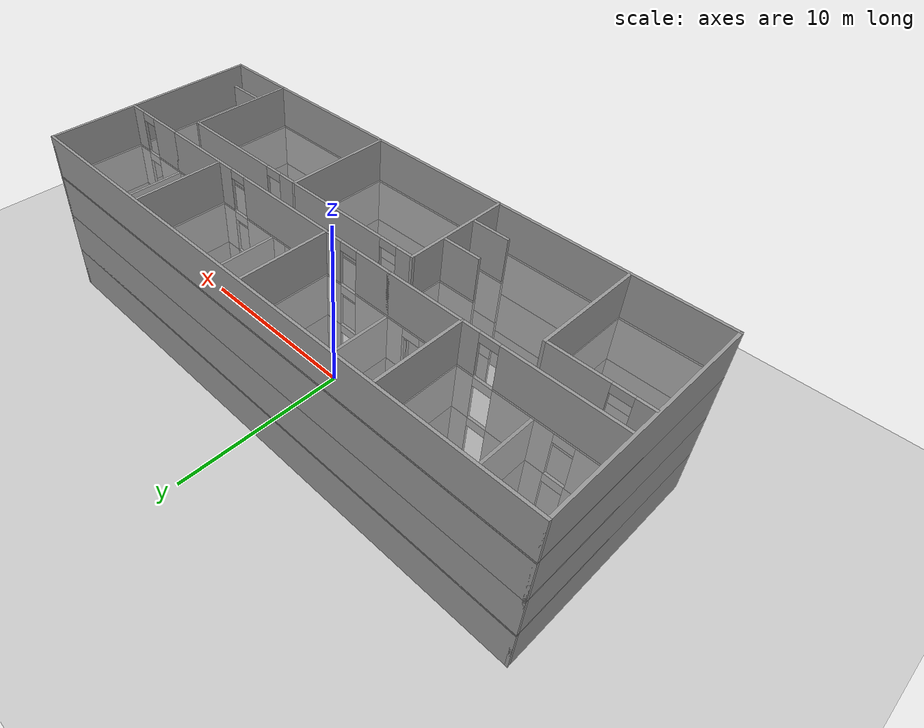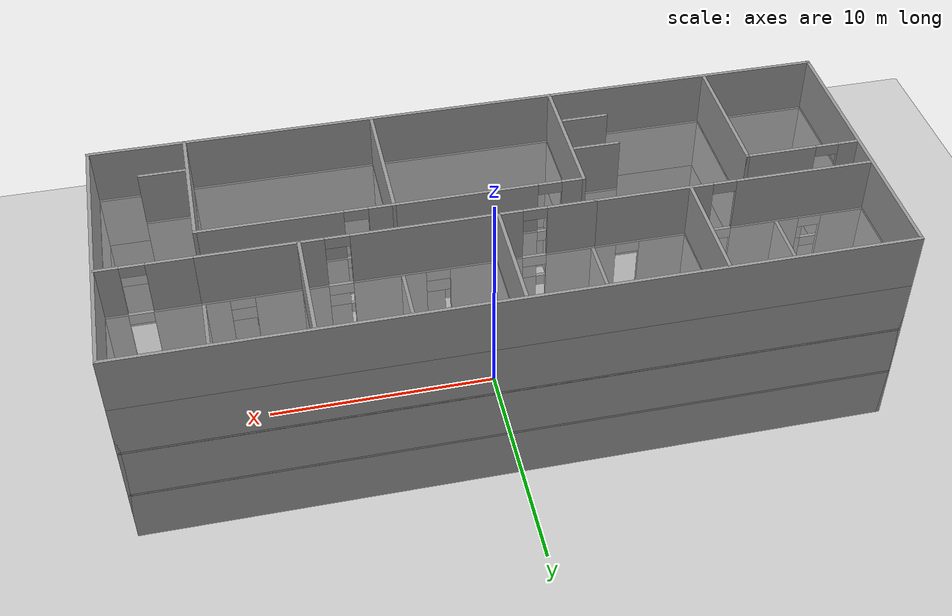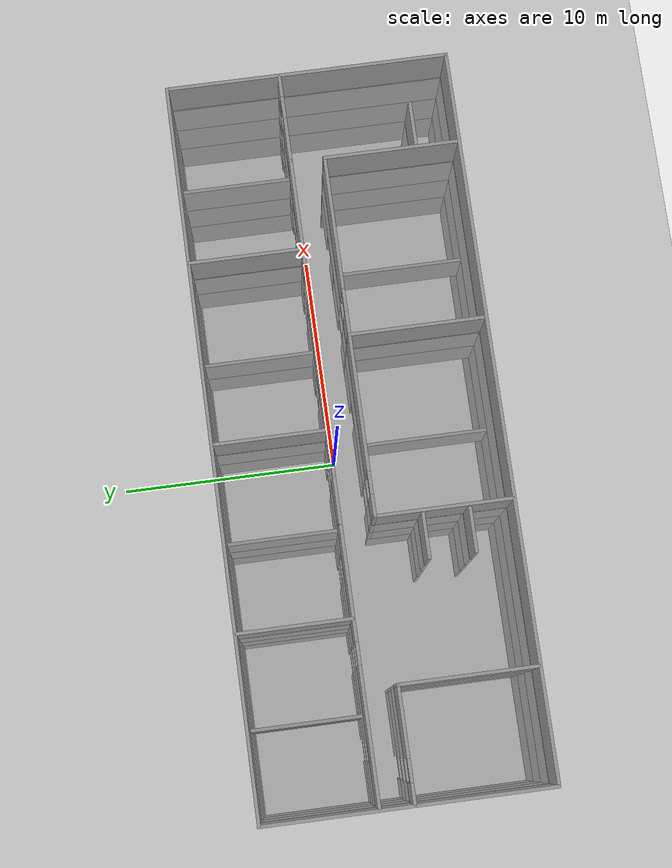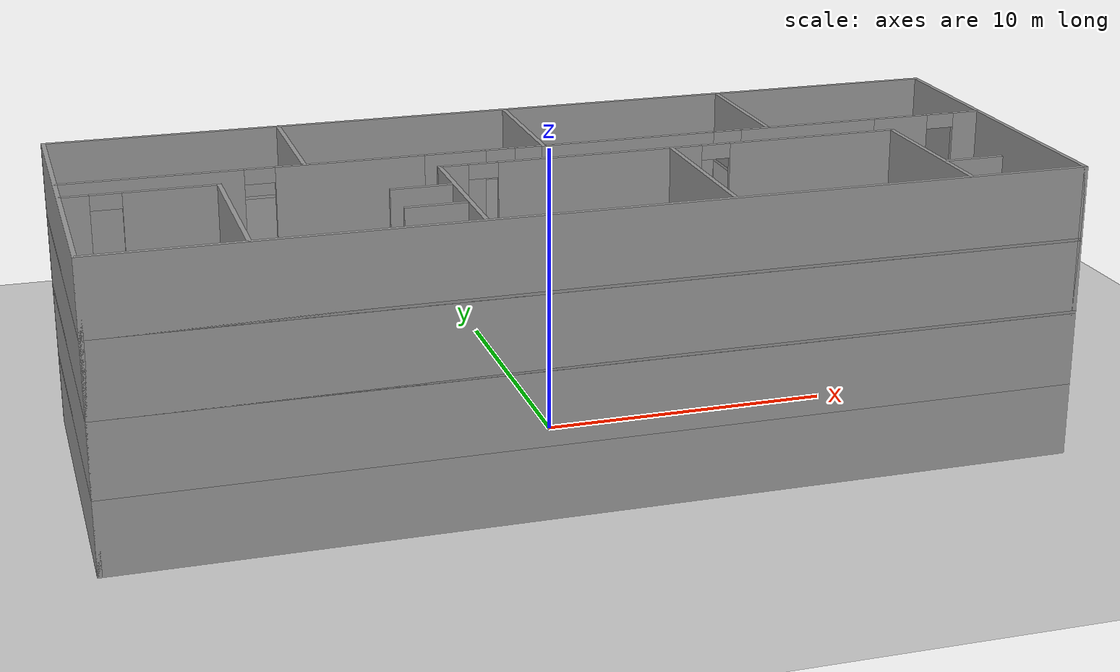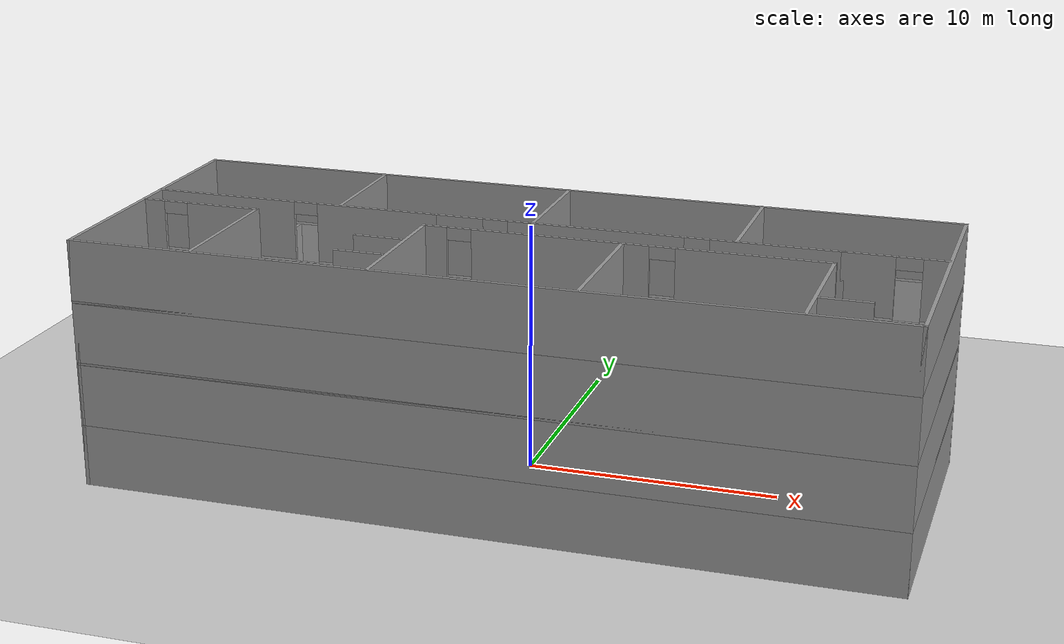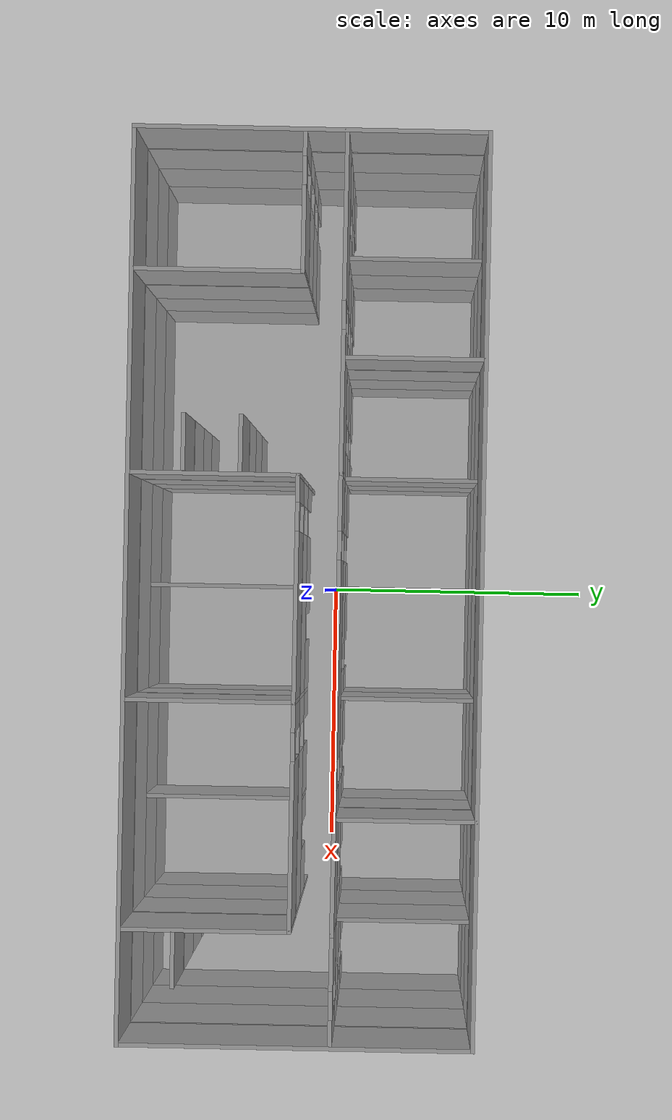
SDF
<sdf version="1.7">
 <world name="default">
  <light name="sun" type="directional">
   <pose>0 0 10 0 -0 0</pose>
   <diffuse>0.8 0.8 0.8 1</diffuse>
   <specular>0.2 0.2 0.2 1</specular>
   <attenuation>
    <range>1000</range>
    <constant>0.9</constant>
    <linear>0.01</linear>
    <quadratic>0.001</quadratic>
   </attenuation>
   <direction>-0.5 0.1 -0.9</direction>
   <spot><inner_angle>0</inner_angle><outer_angle>0</outer_angle><falloff>0</falloff></spot>
  </light>
  <model name="ground_plane">
   <static>1</static>
   <link name="link">
    <collision name="collision">
     <geometry><plane><normal>0 0 1</normal><size>100 100</size></plane></geometry>
     <surface>
      <contact><collide_bitmask>65535</collide_bitmask></contact>
      <friction><ode><mu>100</mu><mu2>50</mu2></ode></friction>
     </surface>
    </collision>
    <visual name="visual">
     <cast_shadows>0</cast_shadows>
     <geometry><plane><normal>0 0 1</normal><size>100 100</size></plane></geometry>
     <material>
      <script><uri>file://media/materials/scripts/gazebo.material</uri><name>Gazebo/Grey</name></script>
     </material>
    </visual>
   </link>
  </model>
  <gravity>0 0 -9.8</gravity>
  <magnetic_field>6e-06 2.3e-05 -4.2e-05</magnetic_field>
  <atmosphere type="adiabatic"/>
  <physics name="default_physics" default="0" type="ode">
   <max_step_size>0.001</max_step_size>
   <real_time_factor>1</real_time_factor>
   <real_time_update_rate>1000</real_time_update_rate>
  </physics>
  <scene><ambient>0.4 0.4 0.4 1</ambient><background>0.7 0.7 0.7 1</background><shadows>1</shadows></scene>
  <spherical_coordinates>
   <surface_model>EARTH_WGS84</surface_model>
   <latitude_deg>0</latitude_deg>
   <longitude_deg>0</longitude_deg>
   <elevation>0</elevation>
   <heading_deg>0</heading_deg>
  </spherical_coordinates>
  <model name="floor4plan_transp">
   <link name="Floor_0">
    <pose>0 0 2.5 0 -0 0</pose>
    <inertial>
     <mass>1</mass>
     <inertia><ixx>1</ixx><ixy>0</ixy><ixz>0</ixz><iyy>1</iyy><iyz>0</iyz><izz>1</izz></inertia>
    </inertial>
    <visual name="Floor_0_Visual">
     <pose>0 0 0.05 0 -0 0</pose>
     <geometry><box><size>32 12.5 0.1</size></box></geometry>
     <material>
      <script><uri>file://media/materials/scripts/gazebo.material</uri><name>Gazebo/Grey</name></script>
      <ambient>1 1 1 1</ambient>
      <shader type="pixel"><normal_map>__default__</normal_map></shader>
      <diffuse>0.7 0.7 0.7 1</diffuse>
      <specular>0.01 0.01 0.01 1</specular>
      <emissive>0 0 0 1</emissive>
     </material>
     <meta><layer>1</layer></meta>
     <transparency>0.5</transparency>
    </visual>
    <collision name="Floor_0_Collision">
     <pose>0 0 0.05 0 -0 0</pose>
     <geometry><box><size>32 12.5 0.1</size></box></geometry>
     <surface>
      <friction>
       <ode><mu>1</mu><mu2>1</mu2><fdir1>0 0 0</fdir1><slip1>0</slip1><slip2>0</slip2></ode>
       <torsional>
        <coefficient>1</coefficient>
        <patch_radius>0</patch_radius>
        <surface_radius>0</surface_radius>
        <use_patch_radius>1</use_patch_radius>
        <ode><slip>0</slip></ode>
       </torsional>
      </friction>
      <bounce><restitution_coefficient>0</restitution_coefficient><threshold>1e+06</threshold></bounce>
      <contact>
       <collide_without_contact>0</collide_without_contact>
       <collide_without_contact_bitmask>1</collide_without_contact_bitmask>
       <collide_bitmask>1</collide_bitmask>
       <ode>
        <soft_cfm>0</soft_cfm>
        <soft_erp>0.2</soft_erp>
        <kp>1e+13</kp>
        <kd>1</kd>
        <max_vel>0.01</max_vel>
        <min_depth>0</min_depth>
       </ode>
       <bullet>
        <split_impulse>1</split_impulse>
        <split_impulse_penetration_threshold>-0.01</split_impulse_penetration_threshold>
        <soft_cfm>0</soft_cfm>
        <soft_erp>0.2</soft_erp>
        <kp>1e+13</kp>
        <kd>1</kd>
       </bullet>
      </contact>
     </surface>
    </collision>
   </link>
   <link name="Floor_1">
    <pose>0 0 5 0 -0 0</pose>
    <inertial>
     <mass>1</mass>
     <inertia><ixx>1</ixx><ixy>0</ixy><ixz>0</ixz><iyy>1</iyy><iyz>0</iyz><izz>1</izz></inertia>
    </inertial>
    <visual name="Floor_1_Visual">
     <pose>0 0 0.05 0 -0 0</pose>
     <geometry><box><size>32 12.5 0.1</size></box></geometry>
     <material>
      <script><uri>file://media/materials/scripts/gazebo.material</uri><name>Gazebo/Grey</name></script>
      <ambient>1 1 1 1</ambient>
      <shader type="pixel"><normal_map>__default__</normal_map></shader>
      <diffuse>0.7 0.7 0.7 1</diffuse>
      <specular>0.01 0.01 0.01 1</specular>
      <emissive>0 0 0 1</emissive>
     </material>
     <meta><layer>2</layer></meta>
     <transparency>0.5</transparency>
    </visual>
    <collision name="Floor_1_Collision">
     <pose>0 0 0.05 0 -0 0</pose>
     <geometry><box><size>32 12.5 0.1</size></box></geometry>
     <surface>
      <friction>
       <ode><mu>1</mu><mu2>1</mu2><fdir1>0 0 0</fdir1><slip1>0</slip1><slip2>0</slip2></ode>
       <torsional>
        <coefficient>1</coefficient>
        <patch_radius>0</patch_radius>
        <surface_radius>0</surface_radius>
        <use_patch_radius>1</use_patch_radius>
        <ode><slip>0</slip></ode>
       </torsional>
      </friction>
      <bounce><restitution_coefficient>0</restitution_coefficient><threshold>1e+06</threshold></bounce>
      <contact>
       <collide_without_contact>0</collide_without_contact>
       <collide_without_contact_bitmask>1</collide_without_contact_bitmask>
       <collide_bitmask>1</collide_bitmask>
       <ode>
        <soft_cfm>0</soft_cfm>
        <soft_erp>0.2</soft_erp>
        <kp>1e+13</kp>
        <kd>1</kd>
        <max_vel>0.01</max_vel>
        <min_depth>0</min_depth>
       </ode>
       <bullet>
        <split_impulse>1</split_impulse>
        <split_impulse_penetration_threshold>-0.01</split_impulse_penetration_threshold>
        <soft_cfm>0</soft_cfm>
        <soft_erp>0.2</soft_erp>
        <kp>1e+13</kp>
        <kd>1</kd>
       </bullet>
      </contact>
     </surface>
    </collision>
   </link>
   <link name="Floor_2">
    <pose>0 0 7.5 0 -0 0</pose>
    <inertial>
     <mass>1</mass>
     <inertia><ixx>1</ixx><ixy>0</ixy><ixz>0</ixz><iyy>1</iyy><iyz>0</iyz><izz>1</izz></inertia>
    </inertial>
    <visual name="Floor_2_Visual">
     <pose>0 0 0.05 0 -0 0</pose>
     <geometry><box><size>32 12.5 0.1</size></box></geometry>
     <material>
      <script><uri>file://media/materials/scripts/gazebo.material</uri><name>Gazebo/Grey</name></script>
      <ambient>1 1 1 1</ambient>
      <shader type="pixel"><normal_map>__default__</normal_map></shader>
      <diffuse>0.7 0.7 0.7 1</diffuse>
      <specular>0.01 0.01 0.01 1</specular>
      <emissive>0 0 0 1</emissive>
     </material>
     <meta><layer>3</layer></meta>
     <transparency>0.5</transparency>
    </visual>
    <collision name="Floor_2_Collision">
     <pose>0 0 0.05 0 -0 0</pose>
     <geometry><box><size>32 12.5 0.1</size></box></geometry>
     <surface>
      <friction>
       <ode><mu>1</mu><mu2>1</mu2><fdir1>0 0 0</fdir1><slip1>0</slip1><slip2>0</slip2></ode>
       <torsional>
        <coefficient>1</coefficient>
        <patch_radius>0</patch_radius>
        <surface_radius>0</surface_radius>
        <use_patch_radius>1</use_patch_radius>
        <ode><slip>0</slip></ode>
       </torsional>
      </friction>
      <bounce><restitution_coefficient>0</restitution_coefficient><threshold>1e+06</threshold></bounce>
      <contact>
       <collide_without_contact>0</collide_without_contact>
       <collide_without_contact_bitmask>1</collide_without_contact_bitmask>
       <collide_bitmask>1</collide_bitmask>
       <ode>
        <soft_cfm>0</soft_cfm>
        <soft_erp>0.2</soft_erp>
        <kp>1e+13</kp>
        <kd>1</kd>
        <max_vel>0.01</max_vel>
        <min_depth>0</min_depth>
       </ode>
       <bullet>
        <split_impulse>1</split_impulse>
        <split_impulse_penetration_threshold>-0.01</split_impulse_penetration_threshold>
        <soft_cfm>0</soft_cfm>
        <soft_erp>0.2</soft_erp>
        <kp>1e+13</kp>
        <kd>1</kd>
       </bullet>
      </contact>
     </surface>
    </collision>
   </link>
   <link name="Wall_0">
    <pose>0 6.175 0 0 -0 0</pose>
    <visual name="Wall_0_Visual">
     <pose>0 0 1.25 0 -0 0</pose>
     <geometry><box><size>32 0.15 2.5</size></box></geometry>
     <material>
      <script><uri>file://media/materials/scripts/gazebo.material</uri><name>Gazebo/Grey</name></script>
      <ambient>1 1 1 1</ambient>
      <shader type="pixel"/>
     </material>
     <meta><layer>0</layer></meta>
    </visual>
    <collision name="Wall_0_Collision">
     <pose>0 0 1.25 0 -0 0</pose>
     <geometry><box><size>32 0.15 2.5</size></box></geometry>
     <surface>
      <friction>
       <ode><mu>1</mu><mu2>1</mu2><fdir1>0 0 0</fdir1><slip1>0</slip1><slip2>0</slip2></ode>
       <torsional>
        <coefficient>1</coefficient>
        <patch_radius>0</patch_radius>
        <surface_radius>0</surface_radius>
        <use_patch_radius>1</use_patch_radius>
        <ode><slip>0</slip></ode>
       </torsional>
      </friction>
      <bounce><restitution_coefficient>0</restitution_coefficient><threshold>1e+06</threshold></bounce>
      <contact>
       <collide_without_contact>0</collide_without_contact>
       <collide_without_contact_bitmask>1</collide_without_contact_bitmask>
       <collide_bitmask>1</collide_bitmask>
       <ode>
        <soft_cfm>0</soft_cfm>
        <soft_erp>0.2</soft_erp>
        <kp>1e+13</kp>
        <kd>1</kd>
        <max_vel>0.01</max_vel>
        <min_depth>0</min_depth>
       </ode>
       <bullet>
        <split_impulse>1</split_impulse>
        <split_impulse_penetration_threshold>-0.01</split_impulse_penetration_threshold>
        <soft_cfm>0</soft_cfm>
        <soft_erp>0.2</soft_erp>
        <kp>1e+13</kp>
        <kd>1</kd>
       </bullet>
      </contact>
     </surface>
    </collision>
   </link>
   <link name="Wall_100">
    <pose>0 6.175 7.5 0 -0 0</pose>
    <visual name="Wall_100_Visual">
     <pose>0 0 1.25 0 -0 0</pose>
     <geometry><box><size>32 0.15 2.5</size></box></geometry>
     <material>
      <script><uri>file://media/materials/scripts/gazebo.material</uri><name>Gazebo/Grey</name></script>
      <ambient>1 1 1 1</ambient>
      <shader type="pixel"/>
     </material>
     <meta><layer>3</layer></meta>
    </visual>
    <collision name="Wall_100_Collision">
     <pose>0 0 1.25 0 -0 0</pose>
     <geometry><box><size>32 0.15 2.5</size></box></geometry>
     <surface>
      <friction>
       <ode><mu>1</mu><mu2>1</mu2><fdir1>0 0 0</fdir1><slip1>0</slip1><slip2>0</slip2></ode>
       <torsional>
        <coefficient>1</coefficient>
        <patch_radius>0</patch_radius>
        <surface_radius>0</surface_radius>
        <use_patch_radius>1</use_patch_radius>
        <ode><slip>0</slip></ode>
       </torsional>
      </friction>
      <bounce><restitution_coefficient>0</restitution_coefficient><threshold>1e+06</threshold></bounce>
      <contact>
       <collide_without_contact>0</collide_without_contact>
       <collide_without_contact_bitmask>1</collide_without_contact_bitmask>
       <collide_bitmask>1</collide_bitmask>
       <ode>
        <soft_cfm>0</soft_cfm>
        <soft_erp>0.2</soft_erp>
        <kp>1e+13</kp>
        <kd>1</kd>
        <max_vel>0.01</max_vel>
        <min_depth>0</min_depth>
       </ode>
       <bullet>
        <split_impulse>1</split_impulse>
        <split_impulse_penetration_threshold>-0.01</split_impulse_penetration_threshold>
        <soft_cfm>0</soft_cfm>
        <soft_erp>0.2</soft_erp>
        <kp>1e+13</kp>
        <kd>1</kd>
       </bullet>
      </contact>
     </surface>
    </collision>
   </link>
   <link name="Wall_101">
    <pose>-15.925 0 7.5 0 0 -1.5708</pose>
    <visual name="Wall_101_Visual">
     <pose>0 0 1.25 0 -0 0</pose>
     <geometry><box><size>12.5 0.15 2.5</size></box></geometry>
     <material>
      <script><uri>file://media/materials/scripts/gazebo.material</uri><name>Gazebo/Grey</name></script>
      <ambient>1 1 1 1</ambient>
      <shader type="pixel"/>
     </material>
     <meta><layer>3</layer></meta>
    </visual>
    <collision name="Wall_101_Collision">
     <pose>0 0 1.25 0 -0 0</pose>
     <geometry><box><size>12.5 0.15 2.5</size></box></geometry>
     <surface>
      <friction>
       <ode><mu>1</mu><mu2>1</mu2><fdir1>0 0 0</fdir1><slip1>0</slip1><slip2>0</slip2></ode>
       <torsional>
        <coefficient>1</coefficient>
        <patch_radius>0</patch_radius>
        <surface_radius>0</surface_radius>
        <use_patch_radius>1</use_patch_radius>
        <ode><slip>0</slip></ode>
       </torsional>
      </friction>
      <bounce><restitution_coefficient>0</restitution_coefficient><threshold>1e+06</threshold></bounce>
      <contact>
       <collide_without_contact>0</collide_without_contact>
       <collide_without_contact_bitmask>1</collide_without_contact_bitmask>
       <collide_bitmask>1</collide_bitmask>
       <ode>
        <soft_cfm>0</soft_cfm>
        <soft_erp>0.2</soft_erp>
        <kp>1e+13</kp>
        <kd>1</kd>
        <max_vel>0.01</max_vel>
        <min_depth>0</min_depth>
       </ode>
       <bullet>
        <split_impulse>1</split_impulse>
        <split_impulse_penetration_threshold>-0.01</split_impulse_penetration_threshold>
        <soft_cfm>0</soft_cfm>
        <soft_erp>0.2</soft_erp>
        <kp>1e+13</kp>
        <kd>1</kd>
       </bullet>
      </contact>
     </surface>
    </collision>
   </link>
   <link name="Wall_102">
    <pose>0 -6.175 7.5 0 -0 0</pose>
    <visual name="Wall_102_Visual">
     <pose>0 0 1.25 0 -0 0</pose>
     <geometry><box><size>32 0.15 2.5</size></box></geometry>
     <material>
      <script><uri>file://media/materials/scripts/gazebo.material</uri><name>Gazebo/Grey</name></script>
      <ambient>1 1 1 1</ambient>
      <shader type="pixel"/>
     </material>
     <meta><layer>3</layer></meta>
    </visual>
    <collision name="Wall_102_Collision">
     <pose>0 0 1.25 0 -0 0</pose>
     <geometry><box><size>32 0.15 2.5</size></box></geometry>
     <surface>
      <friction>
       <ode><mu>1</mu><mu2>1</mu2><fdir1>0 0 0</fdir1><slip1>0</slip1><slip2>0</slip2></ode>
       <torsional>
        <coefficient>1</coefficient>
        <patch_radius>0</patch_radius>
        <surface_radius>0</surface_radius>
        <use_patch_radius>1</use_patch_radius>
        <ode><slip>0</slip></ode>
       </torsional>
      </friction>
      <bounce><restitution_coefficient>0</restitution_coefficient><threshold>1e+06</threshold></bounce>
      <contact>
       <collide_without_contact>0</collide_without_contact>
       <collide_without_contact_bitmask>1</collide_without_contact_bitmask>
       <collide_bitmask>1</collide_bitmask>
       <ode>
        <soft_cfm>0</soft_cfm>
        <soft_erp>0.2</soft_erp>
        <kp>1e+13</kp>
        <kd>1</kd>
        <max_vel>0.01</max_vel>
        <min_depth>0</min_depth>
       </ode>
       <bullet>
        <split_impulse>1</split_impulse>
        <split_impulse_penetration_threshold>-0.01</split_impulse_penetration_threshold>
        <soft_cfm>0</soft_cfm>
        <soft_erp>0.2</soft_erp>
        <kp>1e+13</kp>
        <kd>1</kd>
       </bullet>
      </contact>
     </surface>
    </collision>
   </link>
   <link name="Wall_103">
    <pose>15.925 0 7.5 0 -0 1.5708</pose>
    <visual name="Wall_103_Visual">
     <pose>0 0 1.25 0 -0 0</pose>
     <geometry><box><size>12.5 0.15 2.5</size></box></geometry>
     <material>
      <script><uri>file://media/materials/scripts/gazebo.material</uri><name>Gazebo/Grey</name></script>
      <ambient>1 1 1 1</ambient>
      <shader type="pixel"/>
     </material>
     <meta><layer>3</layer></meta>
    </visual>
    <collision name="Wall_103_Collision">
     <pose>0 0 1.25 0 -0 0</pose>
     <geometry><box><size>12.5 0.15 2.5</size></box></geometry>
     <surface>
      <friction>
       <ode><mu>1</mu><mu2>1</mu2><fdir1>0 0 0</fdir1><slip1>0</slip1><slip2>0</slip2></ode>
       <torsional>
        <coefficient>1</coefficient>
        <patch_radius>0</patch_radius>
        <surface_radius>0</surface_radius>
        <use_patch_radius>1</use_patch_radius>
        <ode><slip>0</slip></ode>
       </torsional>
      </friction>
      <bounce><restitution_coefficient>0</restitution_coefficient><threshold>1e+06</threshold></bounce>
      <contact>
       <collide_without_contact>0</collide_without_contact>
       <collide_without_contact_bitmask>1</collide_without_contact_bitmask>
       <collide_bitmask>1</collide_bitmask>
       <ode>
        <soft_cfm>0</soft_cfm>
        <soft_erp>0.2</soft_erp>
        <kp>1e+13</kp>
        <kd>1</kd>
        <max_vel>0.01</max_vel>
        <min_depth>0</min_depth>
       </ode>
       <bullet>
        <split_impulse>1</split_impulse>
        <split_impulse_penetration_threshold>-0.01</split_impulse_penetration_threshold>
        <soft_cfm>0</soft_cfm>
        <soft_erp>0.2</soft_erp>
        <kp>1e+13</kp>
        <kd>1</kd>
       </bullet>
      </contact>
     </surface>
    </collision>
   </link>
   <link name="Wall_104">
    <pose>-9.94146 1.21683 7.5 0 -0 0</pose>
    <visual name="Wall_104_Visual_0">
     <pose>-3.03204 0 1.25 0 -0 0</pose>
     <geometry><box><size>5.93592 0.15 2.5</size></box></geometry>
     <material>
      <script><uri>file://media/materials/scripts/gazebo.material</uri><name>Gazebo/Grey</name></script>
      <ambient>1 1 1 1</ambient>
      <shader type="pixel"/>
     </material>
     <meta><layer>3</layer></meta>
    </visual>
    <visual name="Wall_104_Visual_1">
     <pose>3.46796 0 1.25 0 -0 0</pose>
     <geometry><box><size>5.06408 0.15 2.5</size></box></geometry>
     <material>
      <script><uri>file://media/materials/scripts/gazebo.material</uri><name>Gazebo/Grey</name></script>
      <ambient>1 1 1 1</ambient>
      <shader type="pixel"/>
     </material>
     <meta><layer>3</layer></meta>
    </visual>
    <visual name="Wall_104_Visual_2">
     <pose>0.435917 0 2.25 0 -0 0</pose>
     <geometry><box><size>1 0.15 0.5</size></box></geometry>
     <material>
      <script><uri>file://media/materials/scripts/gazebo.material</uri><name>Gazebo/Grey</name></script>
      <ambient>1 1 1 1</ambient>
      <shader type="pixel"/>
     </material>
     <meta><layer>3</layer></meta>
    </visual>
    <collision name="Wall_104_Collision_0">
     <pose>-3.03204 0 1.25 0 -0 0</pose>
     <geometry><box><size>5.93592 0.15 2.5</size></box></geometry>
     <surface>
      <friction>
       <ode><mu>1</mu><mu2>1</mu2><fdir1>0 0 0</fdir1><slip1>0</slip1><slip2>0</slip2></ode>
       <torsional>
        <coefficient>1</coefficient>
        <patch_radius>0</patch_radius>
        <surface_radius>0</surface_radius>
        <use_patch_radius>1</use_patch_radius>
        <ode><slip>0</slip></ode>
       </torsional>
      </friction>
      <bounce><restitution_coefficient>0</restitution_coefficient><threshold>1e+06</threshold></bounce>
      <contact>
       <collide_without_contact>0</collide_without_contact>
       <collide_without_contact_bitmask>1</collide_without_contact_bitmask>
       <collide_bitmask>1</collide_bitmask>
       <ode>
        <soft_cfm>0</soft_cfm>
        <soft_erp>0.2</soft_erp>
        <kp>1e+13</kp>
        <kd>1</kd>
        <max_vel>0.01</max_vel>
        <min_depth>0</min_depth>
       </ode>
       <bullet>
        <split_impulse>1</split_impulse>
        <split_impulse_penetration_threshold>-0.01</split_impulse_penetration_threshold>
        <soft_cfm>0</soft_cfm>
        <soft_erp>0.2</soft_erp>
        <kp>1e+13</kp>
        <kd>1</kd>
       </bullet>
      </contact>
     </surface>
    </collision>
    <collision name="Wall_104_Collision_1">
     <pose>3.46796 0 1.25 0 -0 0</pose>
     <geometry><box><size>5.06408 0.15 2.5</size></box></geometry>
     <surface>
      <friction>
       <ode><mu>1</mu><mu2>1</mu2><fdir1>0 0 0</fdir1><slip1>0</slip1><slip2>0</slip2></ode>
       <torsional>
        <coefficient>1</coefficient>
        <patch_radius>0</patch_radius>
        <surface_radius>0</surface_radius>
        <use_patch_radius>1</use_patch_radius>
        <ode><slip>0</slip></ode>
       </torsional>
      </friction>
      <bounce><restitution_coefficient>0</restitution_coefficient><threshold>1e+06</threshold></bounce>
      <contact>
       <collide_without_contact>0</collide_without_contact>
       <collide_without_contact_bitmask>1</collide_without_contact_bitmask>
       <collide_bitmask>1</collide_bitmask>
       <ode>
        <soft_cfm>0</soft_cfm>
        <soft_erp>0.2</soft_erp>
        <kp>1e+13</kp>
        <kd>1</kd>
        <max_vel>0.01</max_vel>
        <min_depth>0</min_depth>
       </ode>
       <bullet>
        <split_impulse>1</split_impulse>
        <split_impulse_penetration_threshold>-0.01</split_impulse_penetration_threshold>
        <soft_cfm>0</soft_cfm>
        <soft_erp>0.2</soft_erp>
        <kp>1e+13</kp>
        <kd>1</kd>
       </bullet>
      </contact>
     </surface>
    </collision>
    <collision name="Wall_104_Collision_2">
     <pose>0.435917 0 2.25 0 -0 0</pose>
     <geometry><box><size>1 0.15 0.5</size></box></geometry>
     <surface>
      <friction>
       <ode><mu>1</mu><mu2>1</mu2><fdir1>0 0 0</fdir1><slip1>0</slip1><slip2>0</slip2></ode>
       <torsional>
        <coefficient>1</coefficient>
        <patch_radius>0</patch_radius>
        <surface_radius>0</surface_radius>
        <use_patch_radius>1</use_patch_radius>
        <ode><slip>0</slip></ode>
       </torsional>
      </friction>
      <bounce><restitution_coefficient>0</restitution_coefficient><threshold>1e+06</threshold></bounce>
      <contact>
       <collide_without_contact>0</collide_without_contact>
       <collide_without_contact_bitmask>1</collide_without_contact_bitmask>
       <collide_bitmask>1</collide_bitmask>
       <ode>
        <soft_cfm>0</soft_cfm>
        <soft_erp>0.2</soft_erp>
        <kp>1e+13</kp>
        <kd>1</kd>
        <max_vel>0.01</max_vel>
        <min_depth>0</min_depth>
       </ode>
       <bullet>
        <split_impulse>1</split_impulse>
        <split_impulse_penetration_threshold>-0.01</split_impulse_penetration_threshold>
        <soft_cfm>0</soft_cfm>
        <soft_erp>0.2</soft_erp>
        <kp>1e+13</kp>
        <kd>1</kd>
       </bullet>
      </contact>
     </surface>
    </collision>
   </link>
   <link name="Wall_105">
    <pose>3.98949 1.21683 7.5 0 -0 0</pose>
    <visual name="Wall_105_Visual_0">
     <pose>-7.04797 0 1.25 0 -0 0</pose>
     <geometry><box><size>2.06598 0.15 2.5</size></box></geometry>
     <material>
      <script><uri>file://media/materials/scripts/gazebo.material</uri><name>Gazebo/Grey</name></script>
      <ambient>1 1 1 1</ambient>
      <shader type="pixel"/>
     </material>
     <meta><layer>3</layer></meta>
    </visual>
    <visual name="Wall_105_Visual_1">
     <pose>-1.51338 0 1.25 0 -0 0</pose>
     <geometry><box><size>7.00319 0.15 2.5</size></box></geometry>
     <material>
      <script><uri>file://media/materials/scripts/gazebo.material</uri><name>Gazebo/Grey</name></script>
      <ambient>1 1 1 1</ambient>
      <shader type="pixel"/>
     </material>
     <meta><layer>3</layer></meta>
    </visual>
    <visual name="Wall_105_Visual_2">
     <pose>5.53458 0 1.25 0 -0 0</pose>
     <geometry><box><size>5.09275 0.15 2.5</size></box></geometry>
     <material>
      <script><uri>file://media/materials/scripts/gazebo.material</uri><name>Gazebo/Grey</name></script>
      <ambient>1 1 1 1</ambient>
      <shader type="pixel"/>
     </material>
     <meta><layer>3</layer></meta>
    </visual>
    <visual name="Wall_105_Visual_3">
     <pose>-5.51498 0 2.25 0 -0 0</pose>
     <geometry><box><size>1 0.15 0.5</size></box></geometry>
     <material>
      <script><uri>file://media/materials/scripts/gazebo.material</uri><name>Gazebo/Grey</name></script>
      <ambient>1 1 1 1</ambient>
      <shader type="pixel"/>
     </material>
     <meta><layer>3</layer></meta>
    </visual>
    <visual name="Wall_105_Visual_4">
     <pose>2.48821 0 2.25 0 -0 0</pose>
     <geometry><box><size>1 0.15 0.5</size></box></geometry>
     <material>
      <script><uri>file://media/materials/scripts/gazebo.material</uri><name>Gazebo/Grey</name></script>
      <ambient>1 1 1 1</ambient>
      <shader type="pixel"/>
     </material>
     <meta><layer>3</layer></meta>
    </visual>
    <collision name="Wall_105_Collision_0">
     <pose>-7.04797 0 1.25 0 -0 0</pose>
     <geometry><box><size>2.06598 0.15 2.5</size></box></geometry>
     <surface>
      <friction>
       <ode><mu>1</mu><mu2>1</mu2><fdir1>0 0 0</fdir1><slip1>0</slip1><slip2>0</slip2></ode>
       <torsional>
        <coefficient>1</coefficient>
        <patch_radius>0</patch_radius>
        <surface_radius>0</surface_radius>
        <use_patch_radius>1</use_patch_radius>
        <ode><slip>0</slip></ode>
       </torsional>
      </friction>
      <bounce><restitution_coefficient>0</restitution_coefficient><threshold>1e+06</threshold></bounce>
      <contact>
       <collide_without_contact>0</collide_without_contact>
       <collide_without_contact_bitmask>1</collide_without_contact_bitmask>
       <collide_bitmask>1</collide_bitmask>
       <ode>
        <soft_cfm>0</soft_cfm>
        <soft_erp>0.2</soft_erp>
        <kp>1e+13</kp>
        <kd>1</kd>
        <max_vel>0.01</max_vel>
        <min_depth>0</min_depth>
       </ode>
       <bullet>
        <split_impulse>1</split_impulse>
        <split_impulse_penetration_threshold>-0.01</split_impulse_penetration_threshold>
        <soft_cfm>0</soft_cfm>
        <soft_erp>0.2</soft_erp>
        <kp>1e+13</kp>
        <kd>1</kd>
       </bullet>
      </contact>
     </surface>
    </collision>
    <collision name="Wall_105_Collision_1">
     <pose>-1.51338 0 1.25 0 -0 0</pose>
     <geometry><box><size>7.00319 0.15 2.5</size></box></geometry>
     <surface>
      <friction>
       <ode><mu>1</mu><mu2>1</mu2><fdir1>0 0 0</fdir1><slip1>0</slip1><slip2>0</slip2></ode>
       <torsional>
        <coefficient>1</coefficient>
        <patch_radius>0</patch_radius>
        <surface_radius>0</surface_radius>
        <use_patch_radius>1</use_patch_radius>
        <ode><slip>0</slip></ode>
       </torsional>
      </friction>
      <bounce><restitution_coefficient>0</restitution_coefficient><threshold>1e+06</threshold></bounce>
      <contact>
       <collide_without_contact>0</collide_without_contact>
       <collide_without_contact_bitmask>1</collide_without_contact_bitmask>
       <collide_bitmask>1</collide_bitmask>
       <ode>
        <soft_cfm>0</soft_cfm>
        <soft_erp>0.2</soft_erp>
        <kp>1e+13</kp>
        <kd>1</kd>
        <max_vel>0.01</max_vel>
        <min_depth>0</min_depth>
       </ode>
       <bullet>
        <split_impulse>1</split_impulse>
        <split_impulse_penetration_threshold>-0.01</split_impulse_penetration_threshold>
        <soft_cfm>0</soft_cfm>
        <soft_erp>0.2</soft_erp>
        <kp>1e+13</kp>
        <kd>1</kd>
       </bullet>
      </contact>
     </surface>
    </collision>
    <collision name="Wall_105_Collision_2">
     <pose>5.53458 0 1.25 0 -0 0</pose>
     <geometry><box><size>5.09275 0.15 2.5</size></box></geometry>
     <surface>
      <friction>
       <ode><mu>1</mu><mu2>1</mu2><fdir1>0 0 0</fdir1><slip1>0</slip1><slip2>0</slip2></ode>
       <torsional>
        <coefficient>1</coefficient>
        <patch_radius>0</patch_radius>
        <surface_radius>0</surface_radius>
        <use_patch_radius>1</use_patch_radius>
        <ode><slip>0</slip></ode>
       </torsional>
      </friction>
      <bounce><restitution_coefficient>0</restitution_coefficient><threshold>1e+06</threshold></bounce>
      <contact>
       <collide_without_contact>0</collide_without_contact>
       <collide_without_contact_bitmask>1</collide_without_contact_bitmask>
       <collide_bitmask>1</collide_bitmask>
       <ode>
        <soft_cfm>0</soft_cfm>
        <soft_erp>0.2</soft_erp>
        <kp>1e+13</kp>
        <kd>1</kd>
        <max_vel>0.01</max_vel>
        <min_depth>0</min_depth>
       </ode>
       <bullet>
        <split_impulse>1</split_impulse>
        <split_impulse_penetration_threshold>-0.01</split_impulse_penetration_threshold>
        <soft_cfm>0</soft_cfm>
        <soft_erp>0.2</soft_erp>
        <kp>1e+13</kp>
        <kd>1</kd>
       </bullet>
      </contact>
     </surface>
    </collision>
    <collision name="Wall_105_Collision_3">
     <pose>-5.51498 0 2.25 0 -0 0</pose>
     <geometry><box><size>1 0.15 0.5</size></box></geometry>
     <surface>
      <friction>
       <ode><mu>1</mu><mu2>1</mu2><fdir1>0 0 0</fdir1><slip1>0</slip1><slip2>0</slip2></ode>
       <torsional>
        <coefficient>1</coefficient>
        <patch_radius>0</patch_radius>
        <surface_radius>0</surface_radius>
        <use_patch_radius>1</use_patch_radius>
        <ode><slip>0</slip></ode>
       </torsional>
      </friction>
      <bounce><restitution_coefficient>0</restitution_coefficient><threshold>1e+06</threshold></bounce>
      <contact>
       <collide_without_contact>0</collide_without_contact>
       <collide_without_contact_bitmask>1</collide_without_contact_bitmask>
       <collide_bitmask>1</collide_bitmask>
       <ode>
        <soft_cfm>0</soft_cfm>
        <soft_erp>0.2</soft_erp>
        <kp>1e+13</kp>
        <kd>1</kd>
        <max_vel>0.01</max_vel>
        <min_depth>0</min_depth>
       </ode>
       <bullet>
        <split_impulse>1</split_impulse>
        <split_impulse_penetration_threshold>-0.01</split_impulse_penetration_threshold>
        <soft_cfm>0</soft_cfm>
        <soft_erp>0.2</soft_erp>
        <kp>1e+13</kp>
        <kd>1</kd>
       </bullet>
      </contact>
     </surface>
    </collision>
    <collision name="Wall_105_Collision_4">
     <pose>2.48821 0 2.25 0 -0 0</pose>
     <geometry><box><size>1 0.15 0.5</size></box></geometry>
     <surface>
      <friction>
       <ode><mu>1</mu><mu2>1</mu2><fdir1>0 0 0</fdir1><slip1>0</slip1><slip2>0</slip2></ode>
       <torsional>
        <coefficient>1</coefficient>
        <patch_radius>0</patch_radius>
        <surface_radius>0</surface_radius>
        <use_patch_radius>1</use_patch_radius>
        <ode><slip>0</slip></ode>
       </torsional>
      </friction>
      <bounce><restitution_coefficient>0</restitution_coefficient><threshold>1e+06</threshold></bounce>
      <contact>
       <collide_without_contact>0</collide_without_contact>
       <collide_without_contact_bitmask>1</collide_without_contact_bitmask>
       <collide_bitmask>1</collide_bitmask>
       <ode>
        <soft_cfm>0</soft_cfm>
        <soft_erp>0.2</soft_erp>
        <kp>1e+13</kp>
        <kd>1</kd>
        <max_vel>0.01</max_vel>
        <min_depth>0</min_depth>
       </ode>
       <bullet>
        <split_impulse>1</split_impulse>
        <split_impulse_penetration_threshold>-0.01</split_impulse_penetration_threshold>
        <soft_cfm>0</soft_cfm>
        <soft_erp>0.2</soft_erp>
        <kp>1e+13</kp>
        <kd>1</kd>
       </bullet>
      </contact>
     </surface>
    </collision>
   </link>
   <link name="Wall_106">
    <pose>13.9205 1.21683 7.5 0 -0 0</pose>
    <visual name="Wall_106_Visual_0">
     <pose>-0.992908 0 1.25 0 -0 0</pose>
     <geometry><box><size>2.01418 0.15 2.5</size></box></geometry>
     <material>
      <script><uri>file://media/materials/scripts/gazebo.material</uri><name>Gazebo/Grey</name></script>
      <ambient>1 1 1 1</ambient>
      <shader type="pixel"/>
     </material>
     <meta><layer>3</layer></meta>
    </visual>
    <visual name="Wall_106_Visual_1">
     <pose>1.50709 0 1.25 0 -0 0</pose>
     <geometry><box><size>0.985817 0.15 2.5</size></box></geometry>
     <material>
      <script><uri>file://media/materials/scripts/gazebo.material</uri><name>Gazebo/Grey</name></script>
      <ambient>1 1 1 1</ambient>
      <shader type="pixel"/>
     </material>
     <meta><layer>3</layer></meta>
    </visual>
    <visual name="Wall_106_Visual_2">
     <pose>0.514183 0 2.25 0 -0 0</pose>
     <geometry><box><size>1 0.15 0.5</size></box></geometry>
     <material>
      <script><uri>file://media/materials/scripts/gazebo.material</uri><name>Gazebo/Grey</name></script>
      <ambient>1 1 1 1</ambient>
      <shader type="pixel"/>
     </material>
     <meta><layer>3</layer></meta>
    </visual>
    <collision name="Wall_106_Collision_0">
     <pose>-0.992908 0 1.25 0 -0 0</pose>
     <geometry><box><size>2.01418 0.15 2.5</size></box></geometry>
     <surface>
      <friction>
       <ode><mu>1</mu><mu2>1</mu2><fdir1>0 0 0</fdir1><slip1>0</slip1><slip2>0</slip2></ode>
       <torsional>
        <coefficient>1</coefficient>
        <patch_radius>0</patch_radius>
        <surface_radius>0</surface_radius>
        <use_patch_radius>1</use_patch_radius>
        <ode><slip>0</slip></ode>
       </torsional>
      </friction>
      <bounce><restitution_coefficient>0</restitution_coefficient><threshold>1e+06</threshold></bounce>
      <contact>
       <collide_without_contact>0</collide_without_contact>
       <collide_without_contact_bitmask>1</collide_without_contact_bitmask>
       <collide_bitmask>1</collide_bitmask>
       <ode>
        <soft_cfm>0</soft_cfm>
        <soft_erp>0.2</soft_erp>
        <kp>1e+13</kp>
        <kd>1</kd>
        <max_vel>0.01</max_vel>
        <min_depth>0</min_depth>
       </ode>
       <bullet>
        <split_impulse>1</split_impulse>
        <split_impulse_penetration_threshold>-0.01</split_impulse_penetration_threshold>
        <soft_cfm>0</soft_cfm>
        <soft_erp>0.2</soft_erp>
        <kp>1e+13</kp>
        <kd>1</kd>
       </bullet>
      </contact>
     </surface>
    </collision>
    <collision name="Wall_106_Collision_1">
     <pose>1.50709 0 1.25 0 -0 0</pose>
     <geometry><box><size>0.985817 0.15 2.5</size></box></geometry>
     <surface>
      <friction>
       <ode><mu>1</mu><mu2>1</mu2><fdir1>0 0 0</fdir1><slip1>0</slip1><slip2>0</slip2></ode>
       <torsional>
        <coefficient>1</coefficient>
        <patch_radius>0</patch_radius>
        <surface_radius>0</surface_radius>
        <use_patch_radius>1</use_patch_radius>
        <ode><slip>0</slip></ode>
       </torsional>
      </friction>
      <bounce><restitution_coefficient>0</restitution_coefficient><threshold>1e+06</threshold></bounce>
      <contact>
       <collide_without_contact>0</collide_without_contact>
       <collide_without_contact_bitmask>1</collide_without_contact_bitmask>
       <collide_bitmask>1</collide_bitmask>
       <ode>
        <soft_cfm>0</soft_cfm>
        <soft_erp>0.2</soft_erp>
        <kp>1e+13</kp>
        <kd>1</kd>
        <max_vel>0.01</max_vel>
        <min_depth>0</min_depth>
       </ode>
       <bullet>
        <split_impulse>1</split_impulse>
        <split_impulse_penetration_threshold>-0.01</split_impulse_penetration_threshold>
        <soft_cfm>0</soft_cfm>
        <soft_erp>0.2</soft_erp>
        <kp>1e+13</kp>
        <kd>1</kd>
       </bullet>
      </contact>
     </surface>
    </collision>
    <collision name="Wall_106_Collision_2">
     <pose>0.514183 0 2.25 0 -0 0</pose>
     <geometry><box><size>1 0.15 0.5</size></box></geometry>
     <surface>
      <friction>
       <ode><mu>1</mu><mu2>1</mu2><fdir1>0 0 0</fdir1><slip1>0</slip1><slip2>0</slip2></ode>
       <torsional>
        <coefficient>1</coefficient>
        <patch_radius>0</patch_radius>
        <surface_radius>0</surface_radius>
        <use_patch_radius>1</use_patch_radius>
        <ode><slip>0</slip></ode>
       </torsional>
      </friction>
      <bounce><restitution_coefficient>0</restitution_coefficient><threshold>1e+06</threshold></bounce>
      <contact>
       <collide_without_contact>0</collide_without_contact>
       <collide_without_contact_bitmask>1</collide_without_contact_bitmask>
       <collide_bitmask>1</collide_bitmask>
       <ode>
        <soft_cfm>0</soft_cfm>
        <soft_erp>0.2</soft_erp>
        <kp>1e+13</kp>
        <kd>1</kd>
        <max_vel>0.01</max_vel>
        <min_depth>0</min_depth>
       </ode>
       <bullet>
        <split_impulse>1</split_impulse>
        <split_impulse_penetration_threshold>-0.01</split_impulse_penetration_threshold>
        <soft_cfm>0</soft_cfm>
        <soft_erp>0.2</soft_erp>
        <kp>1e+13</kp>
        <kd>1</kd>
       </bullet>
      </contact>
     </surface>
    </collision>
   </link>
   <link name="Wall_108">
    <pose>-8.04832 3.67238 7.5 0 0 -1.5708</pose>
    <visual name="Wall_108_Visual">
     <pose>0 0 1.25 0 -0 0</pose>
     <geometry><box><size>5 0.15 2.5</size></box></geometry>
     <material>
      <script><uri>file://media/materials/scripts/gazebo.material</uri><name>Gazebo/Grey</name></script>
      <ambient>1 1 1 1</ambient>
      <shader type="pixel"/>
     </material>
     <meta><layer>3</layer></meta>
    </visual>
    <collision name="Wall_108_Collision">
     <pose>0 0 1.25 0 -0 0</pose>
     <geometry><box><size>5 0.15 2.5</size></box></geometry>
     <surface>
      <friction>
       <ode><mu>1</mu><mu2>1</mu2><fdir1>0 0 0</fdir1><slip1>0</slip1><slip2>0</slip2></ode>
       <torsional>
        <coefficient>1</coefficient>
        <patch_radius>0</patch_radius>
        <surface_radius>0</surface_radius>
        <use_patch_radius>1</use_patch_radius>
        <ode><slip>0</slip></ode>
       </torsional>
      </friction>
      <bounce><restitution_coefficient>0</restitution_coefficient><threshold>1e+06</threshold></bounce>
      <contact>
       <collide_without_contact>0</collide_without_contact>
       <collide_without_contact_bitmask>1</collide_without_contact_bitmask>
       <collide_bitmask>1</collide_bitmask>
       <ode>
        <soft_cfm>0</soft_cfm>
        <soft_erp>0.2</soft_erp>
        <kp>1e+13</kp>
        <kd>1</kd>
        <max_vel>0.01</max_vel>
        <min_depth>0</min_depth>
       </ode>
       <bullet>
        <split_impulse>1</split_impulse>
        <split_impulse_penetration_threshold>-0.01</split_impulse_penetration_threshold>
        <soft_cfm>0</soft_cfm>
        <soft_erp>0.2</soft_erp>
        <kp>1e+13</kp>
        <kd>1</kd>
       </bullet>
      </contact>
     </surface>
    </collision>
   </link>
   <link name="Wall_110">
    <pose>-0.021996 3.62612 7.5 0 0 -1.5708</pose>
    <visual name="Wall_110_Visual">
     <pose>0 0 1.25 0 -0 0</pose>
     <geometry><box><size>5 0.15 2.5</size></box></geometry>
     <material>
      <script><uri>file://media/materials/scripts/gazebo.material</uri><name>Gazebo/Grey</name></script>
      <ambient>1 1 1 1</ambient>
      <shader type="pixel"/>
     </material>
     <meta><layer>3</layer></meta>
    </visual>
    <collision name="Wall_110_Collision">
     <pose>0 0 1.25 0 -0 0</pose>
     <geometry><box><size>5 0.15 2.5</size></box></geometry>
     <surface>
      <friction>
       <ode><mu>1</mu><mu2>1</mu2><fdir1>0 0 0</fdir1><slip1>0</slip1><slip2>0</slip2></ode>
       <torsional>
        <coefficient>1</coefficient>
        <patch_radius>0</patch_radius>
        <surface_radius>0</surface_radius>
        <use_patch_radius>1</use_patch_radius>
        <ode><slip>0</slip></ode>
       </torsional>
      </friction>
      <bounce><restitution_coefficient>0</restitution_coefficient><threshold>1e+06</threshold></bounce>
      <contact>
       <collide_without_contact>0</collide_without_contact>
       <collide_without_contact_bitmask>1</collide_without_contact_bitmask>
       <collide_bitmask>1</collide_bitmask>
       <ode>
        <soft_cfm>0</soft_cfm>
        <soft_erp>0.2</soft_erp>
        <kp>1e+13</kp>
        <kd>1</kd>
        <max_vel>0.01</max_vel>
        <min_depth>0</min_depth>
       </ode>
       <bullet>
        <split_impulse>1</split_impulse>
        <split_impulse_penetration_threshold>-0.01</split_impulse_penetration_threshold>
        <soft_cfm>0</soft_cfm>
        <soft_erp>0.2</soft_erp>
        <kp>1e+13</kp>
        <kd>1</kd>
       </bullet>
      </contact>
     </surface>
    </collision>
   </link>
   <link name="Wall_112">
    <pose>7.98119 3.69551 7.5 0 0 -1.5708</pose>
    <visual name="Wall_112_Visual">
     <pose>0 0 1.25 0 -0 0</pose>
     <geometry><box><size>5 0.15 2.5</size></box></geometry>
     <material>
      <script><uri>file://media/materials/scripts/gazebo.material</uri><name>Gazebo/Grey</name></script>
      <ambient>1 1 1 1</ambient>
      <shader type="pixel"/>
     </material>
     <meta><layer>3</layer></meta>
    </visual>
    <collision name="Wall_112_Collision">
     <pose>0 0 1.25 0 -0 0</pose>
     <geometry><box><size>5 0.15 2.5</size></box></geometry>
     <surface>
      <friction>
       <ode><mu>1</mu><mu2>1</mu2><fdir1>0 0 0</fdir1><slip1>0</slip1><slip2>0</slip2></ode>
       <torsional>
        <coefficient>1</coefficient>
        <patch_radius>0</patch_radius>
        <surface_radius>0</surface_radius>
        <use_patch_radius>1</use_patch_radius>
        <ode><slip>0</slip></ode>
       </torsional>
      </friction>
      <bounce><restitution_coefficient>0</restitution_coefficient><threshold>1e+06</threshold></bounce>
      <contact>
       <collide_without_contact>0</collide_without_contact>
       <collide_without_contact_bitmask>1</collide_without_contact_bitmask>
       <collide_bitmask>1</collide_bitmask>
       <ode>
        <soft_cfm>0</soft_cfm>
        <soft_erp>0.2</soft_erp>
        <kp>1e+13</kp>
        <kd>1</kd>
        <max_vel>0.01</max_vel>
        <min_depth>0</min_depth>
       </ode>
       <bullet>
        <split_impulse>1</split_impulse>
        <split_impulse_penetration_threshold>-0.01</split_impulse_penetration_threshold>
        <soft_cfm>0</soft_cfm>
        <soft_erp>0.2</soft_erp>
        <kp>1e+13</kp>
        <kd>1</kd>
       </bullet>
      </contact>
     </surface>
    </collision>
   </link>
   <link name="Wall_114">
    <pose>-13.4183 -0.240402 7.5 0 -0 0</pose>
    <visual name="Wall_114_Visual_0">
     <pose>-2.04171 0 1.25 0 -0 0</pose>
     <geometry><box><size>0.916574 0.15 2.5</size></box></geometry>
     <material>
      <script><uri>file://media/materials/scripts/gazebo.material</uri><name>Gazebo/Grey</name></script>
      <ambient>1 1 1 1</ambient>
      <shader type="pixel"/>
     </material>
     <meta><layer>3</layer></meta>
    </visual>
    <visual name="Wall_114_Visual_1">
     <pose>0.958287 0 1.25 0 -0 0</pose>
     <geometry><box><size>3.08343 0.15 2.5</size></box></geometry>
     <material>
      <script><uri>file://media/materials/scripts/gazebo.material</uri><name>Gazebo/Grey</name></script>
      <ambient>1 1 1 1</ambient>
      <shader type="pixel"/>
     </material>
     <meta><layer>3</layer></meta>
    </visual>
    <visual name="Wall_114_Visual_2">
     <pose>-1.08343 0 2.25 0 -0 0</pose>
     <geometry><box><size>1 0.15 0.5</size></box></geometry>
     <material>
      <script><uri>file://media/materials/scripts/gazebo.material</uri><name>Gazebo/Grey</name></script>
      <ambient>1 1 1 1</ambient>
      <shader type="pixel"/>
     </material>
     <meta><layer>3</layer></meta>
    </visual>
    <collision name="Wall_114_Collision_0">
     <pose>-2.04171 0 1.25 0 -0 0</pose>
     <geometry><box><size>0.916574 0.15 2.5</size></box></geometry>
     <surface>
      <friction>
       <ode><mu>1</mu><mu2>1</mu2><fdir1>0 0 0</fdir1><slip1>0</slip1><slip2>0</slip2></ode>
       <torsional>
        <coefficient>1</coefficient>
        <patch_radius>0</patch_radius>
        <surface_radius>0</surface_radius>
        <use_patch_radius>1</use_patch_radius>
        <ode><slip>0</slip></ode>
       </torsional>
      </friction>
      <bounce><restitution_coefficient>0</restitution_coefficient><threshold>1e+06</threshold></bounce>
      <contact>
       <collide_without_contact>0</collide_without_contact>
       <collide_without_contact_bitmask>1</collide_without_contact_bitmask>
       <collide_bitmask>1</collide_bitmask>
       <ode>
        <soft_cfm>0</soft_cfm>
        <soft_erp>0.2</soft_erp>
        <kp>1e+13</kp>
        <kd>1</kd>
        <max_vel>0.01</max_vel>
        <min_depth>0</min_depth>
       </ode>
       <bullet>
        <split_impulse>1</split_impulse>
        <split_impulse_penetration_threshold>-0.01</split_impulse_penetration_threshold>
        <soft_cfm>0</soft_cfm>
        <soft_erp>0.2</soft_erp>
        <kp>1e+13</kp>
        <kd>1</kd>
       </bullet>
      </contact>
     </surface>
    </collision>
    <collision name="Wall_114_Collision_1">
     <pose>0.958287 0 1.25 0 -0 0</pose>
     <geometry><box><size>3.08343 0.15 2.5</size></box></geometry>
     <surface>
      <friction>
       <ode><mu>1</mu><mu2>1</mu2><fdir1>0 0 0</fdir1><slip1>0</slip1><slip2>0</slip2></ode>
       <torsional>
        <coefficient>1</coefficient>
        <patch_radius>0</patch_radius>
        <surface_radius>0</surface_radius>
        <use_patch_radius>1</use_patch_radius>
        <ode><slip>0</slip></ode>
       </torsional>
      </friction>
      <bounce><restitution_coefficient>0</restitution_coefficient><threshold>1e+06</threshold></bounce>
      <contact>
       <collide_without_contact>0</collide_without_contact>
       <collide_without_contact_bitmask>1</collide_without_contact_bitmask>
       <collide_bitmask>1</collide_bitmask>
       <ode>
        <soft_cfm>0</soft_cfm>
        <soft_erp>0.2</soft_erp>
        <kp>1e+13</kp>
        <kd>1</kd>
        <max_vel>0.01</max_vel>
        <min_depth>0</min_depth>
       </ode>
       <bullet>
        <split_impulse>1</split_impulse>
        <split_impulse_penetration_threshold>-0.01</split_impulse_penetration_threshold>
        <soft_cfm>0</soft_cfm>
        <soft_erp>0.2</soft_erp>
        <kp>1e+13</kp>
        <kd>1</kd>
       </bullet>
      </contact>
     </surface>
    </collision>
    <collision name="Wall_114_Collision_2">
     <pose>-1.08343 0 2.25 0 -0 0</pose>
     <geometry><box><size>1 0.15 0.5</size></box></geometry>
     <surface>
      <friction>
       <ode><mu>1</mu><mu2>1</mu2><fdir1>0 0 0</fdir1><slip1>0</slip1><slip2>0</slip2></ode>
       <torsional>
        <coefficient>1</coefficient>
        <patch_radius>0</patch_radius>
        <surface_radius>0</surface_radius>
        <use_patch_radius>1</use_patch_radius>
        <ode><slip>0</slip></ode>
       </torsional>
      </friction>
      <bounce><restitution_coefficient>0</restitution_coefficient><threshold>1e+06</threshold></bounce>
      <contact>
       <collide_without_contact>0</collide_without_contact>
       <collide_without_contact_bitmask>1</collide_without_contact_bitmask>
       <collide_bitmask>1</collide_bitmask>
       <ode>
        <soft_cfm>0</soft_cfm>
        <soft_erp>0.2</soft_erp>
        <kp>1e+13</kp>
        <kd>1</kd>
        <max_vel>0.01</max_vel>
        <min_depth>0</min_depth>
       </ode>
       <bullet>
        <split_impulse>1</split_impulse>
        <split_impulse_penetration_threshold>-0.01</split_impulse_penetration_threshold>
        <soft_cfm>0</soft_cfm>
        <soft_erp>0.2</soft_erp>
        <kp>1e+13</kp>
        <kd>1</kd>
       </bullet>
      </contact>
     </surface>
    </collision>
   </link>
   <link name="Wall_115">
    <pose>-10.9933 -3.1654 7.5 0 0 -1.5708</pose>
    <visual name="Wall_115_Visual">
     <pose>0 0 1.25 0 -0 0</pose>
     <geometry><box><size>6 0.15 2.5</size></box></geometry>
     <material>
      <script><uri>file://media/materials/scripts/gazebo.material</uri><name>Gazebo/Grey</name></script>
      <ambient>1 1 1 1</ambient>
      <shader type="pixel"/>
     </material>
     <meta><layer>3</layer></meta>
    </visual>
    <collision name="Wall_115_Collision">
     <pose>0 0 1.25 0 -0 0</pose>
     <geometry><box><size>6 0.15 2.5</size></box></geometry>
     <surface>
      <friction>
       <ode><mu>1</mu><mu2>1</mu2><fdir1>0 0 0</fdir1><slip1>0</slip1><slip2>0</slip2></ode>
       <torsional>
        <coefficient>1</coefficient>
        <patch_radius>0</patch_radius>
        <surface_radius>0</surface_radius>
        <use_patch_radius>1</use_patch_radius>
        <ode><slip>0</slip></ode>
       </torsional>
      </friction>
      <bounce><restitution_coefficient>0</restitution_coefficient><threshold>1e+06</threshold></bounce>
      <contact>
       <collide_without_contact>0</collide_without_contact>
       <collide_without_contact_bitmask>1</collide_without_contact_bitmask>
       <collide_bitmask>1</collide_bitmask>
       <ode>
        <soft_cfm>0</soft_cfm>
        <soft_erp>0.2</soft_erp>
        <kp>1e+13</kp>
        <kd>1</kd>
        <max_vel>0.01</max_vel>
        <min_depth>0</min_depth>
       </ode>
       <bullet>
        <split_impulse>1</split_impulse>
        <split_impulse_penetration_threshold>-0.01</split_impulse_penetration_threshold>
        <soft_cfm>0</soft_cfm>
        <soft_erp>0.2</soft_erp>
        <kp>1e+13</kp>
        <kd>1</kd>
       </bullet>
      </contact>
     </surface>
    </collision>
   </link>
   <link name="Wall_116">
    <pose>3.99393 -0.263532 7.5 0 -0 0</pose>
    <visual name="Wall_116_Visual_0">
     <pose>-7.49545 0 1.25 0 -0 0</pose>
     <geometry><box><size>1.0091 0.15 2.5</size></box></geometry>
     <material>
      <script><uri>file://media/materials/scripts/gazebo.material</uri><name>Gazebo/Grey</name></script>
      <ambient>1 1 1 1</ambient>
      <shader type="pixel"/>
     </material>
     <meta><layer>3</layer></meta>
    </visual>
    <visual name="Wall_116_Visual_1">
     <pose>-2.48931 0 1.25 0 -0 0</pose>
     <geometry><box><size>7.00319 0.15 2.5</size></box></geometry>
     <material>
      <script><uri>file://media/materials/scripts/gazebo.material</uri><name>Gazebo/Grey</name></script>
      <ambient>1 1 1 1</ambient>
      <shader type="pixel"/>
     </material>
     <meta><layer>3</layer></meta>
    </visual>
    <visual name="Wall_116_Visual_2">
     <pose>5.00614 0 1.25 0 -0 0</pose>
     <geometry><box><size>5.98771 0.15 2.5</size></box></geometry>
     <material>
      <script><uri>file://media/materials/scripts/gazebo.material</uri><name>Gazebo/Grey</name></script>
      <ambient>1 1 1 1</ambient>
      <shader type="pixel"/>
     </material>
     <meta><layer>3</layer></meta>
    </visual>
    <visual name="Wall_116_Visual_3">
     <pose>-6.4909 0 2.25 0 -0 0</pose>
     <geometry><box><size>1 0.15 0.5</size></box></geometry>
     <material>
      <script><uri>file://media/materials/scripts/gazebo.material</uri><name>Gazebo/Grey</name></script>
      <ambient>1 1 1 1</ambient>
      <shader type="pixel"/>
     </material>
     <meta><layer>3</layer></meta>
    </visual>
    <visual name="Wall_116_Visual_4">
     <pose>1.51229 0 2.25 0 -0 0</pose>
     <geometry><box><size>1 0.15 0.5</size></box></geometry>
     <material>
      <script><uri>file://media/materials/scripts/gazebo.material</uri><name>Gazebo/Grey</name></script>
      <ambient>1 1 1 1</ambient>
      <shader type="pixel"/>
     </material>
     <meta><layer>3</layer></meta>
    </visual>
    <collision name="Wall_116_Collision_0">
     <pose>-7.49545 0 1.25 0 -0 0</pose>
     <geometry><box><size>1.0091 0.15 2.5</size></box></geometry>
     <surface>
      <friction>
       <ode><mu>1</mu><mu2>1</mu2><fdir1>0 0 0</fdir1><slip1>0</slip1><slip2>0</slip2></ode>
       <torsional>
        <coefficient>1</coefficient>
        <patch_radius>0</patch_radius>
        <surface_radius>0</surface_radius>
        <use_patch_radius>1</use_patch_radius>
        <ode><slip>0</slip></ode>
       </torsional>
      </friction>
      <bounce><restitution_coefficient>0</restitution_coefficient><threshold>1e+06</threshold></bounce>
      <contact>
       <collide_without_contact>0</collide_without_contact>
       <collide_without_contact_bitmask>1</collide_without_contact_bitmask>
       <collide_bitmask>1</collide_bitmask>
       <ode>
        <soft_cfm>0</soft_cfm>
        <soft_erp>0.2</soft_erp>
        <kp>1e+13</kp>
        <kd>1</kd>
        <max_vel>0.01</max_vel>
        <min_depth>0</min_depth>
       </ode>
       <bullet>
        <split_impulse>1</split_impulse>
        <split_impulse_penetration_threshold>-0.01</split_impulse_penetration_threshold>
        <soft_cfm>0</soft_cfm>
        <soft_erp>0.2</soft_erp>
        <kp>1e+13</kp>
        <kd>1</kd>
       </bullet>
      </contact>
     </surface>
    </collision>
    <collision name="Wall_116_Collision_1">
     <pose>-2.48931 0 1.25 0 -0 0</pose>
     <geometry><box><size>7.00319 0.15 2.5</size></box></geometry>
     <surface>
      <friction>
       <ode><mu>1</mu><mu2>1</mu2><fdir1>0 0 0</fdir1><slip1>0</slip1><slip2>0</slip2></ode>
       <torsional>
        <coefficient>1</coefficient>
        <patch_radius>0</patch_radius>
        <surface_radius>0</surface_radius>
        <use_patch_radius>1</use_patch_radius>
        <ode><slip>0</slip></ode>
       </torsional>
      </friction>
      <bounce><restitution_coefficient>0</restitution_coefficient><threshold>1e+06</threshold></bounce>
      <contact>
       <collide_without_contact>0</collide_without_contact>
       <collide_without_contact_bitmask>1</collide_without_contact_bitmask>
       <collide_bitmask>1</collide_bitmask>
       <ode>
        <soft_cfm>0</soft_cfm>
        <soft_erp>0.2</soft_erp>
        <kp>1e+13</kp>
        <kd>1</kd>
        <max_vel>0.01</max_vel>
        <min_depth>0</min_depth>
       </ode>
       <bullet>
        <split_impulse>1</split_impulse>
        <split_impulse_penetration_threshold>-0.01</split_impulse_penetration_threshold>
        <soft_cfm>0</soft_cfm>
        <soft_erp>0.2</soft_erp>
        <kp>1e+13</kp>
        <kd>1</kd>
       </bullet>
      </contact>
     </surface>
    </collision>
    <collision name="Wall_116_Collision_2">
     <pose>5.00614 0 1.25 0 -0 0</pose>
     <geometry><box><size>5.98771 0.15 2.5</size></box></geometry>
     <surface>
      <friction>
       <ode><mu>1</mu><mu2>1</mu2><fdir1>0 0 0</fdir1><slip1>0</slip1><slip2>0</slip2></ode>
       <torsional>
        <coefficient>1</coefficient>
        <patch_radius>0</patch_radius>
        <surface_radius>0</surface_radius>
        <use_patch_radius>1</use_patch_radius>
        <ode><slip>0</slip></ode>
       </torsional>
      </friction>
      <bounce><restitution_coefficient>0</restitution_coefficient><threshold>1e+06</threshold></bounce>
      <contact>
       <collide_without_contact>0</collide_without_contact>
       <collide_without_contact_bitmask>1</collide_without_contact_bitmask>
       <collide_bitmask>1</collide_bitmask>
       <ode>
        <soft_cfm>0</soft_cfm>
        <soft_erp>0.2</soft_erp>
        <kp>1e+13</kp>
        <kd>1</kd>
        <max_vel>0.01</max_vel>
        <min_depth>0</min_depth>
       </ode>
       <bullet>
        <split_impulse>1</split_impulse>
        <split_impulse_penetration_threshold>-0.01</split_impulse_penetration_threshold>
        <soft_cfm>0</soft_cfm>
        <soft_erp>0.2</soft_erp>
        <kp>1e+13</kp>
        <kd>1</kd>
       </bullet>
      </contact>
     </surface>
    </collision>
    <collision name="Wall_116_Collision_3">
     <pose>-6.4909 0 2.25 0 -0 0</pose>
     <geometry><box><size>1 0.15 0.5</size></box></geometry>
     <surface>
      <friction>
       <ode><mu>1</mu><mu2>1</mu2><fdir1>0 0 0</fdir1><slip1>0</slip1><slip2>0</slip2></ode>
       <torsional>
        <coefficient>1</coefficient>
        <patch_radius>0</patch_radius>
        <surface_radius>0</surface_radius>
        <use_patch_radius>1</use_patch_radius>
        <ode><slip>0</slip></ode>
       </torsional>
      </friction>
      <bounce><restitution_coefficient>0</restitution_coefficient><threshold>1e+06</threshold></bounce>
      <contact>
       <collide_without_contact>0</collide_without_contact>
       <collide_without_contact_bitmask>1</collide_without_contact_bitmask>
       <collide_bitmask>1</collide_bitmask>
       <ode>
        <soft_cfm>0</soft_cfm>
        <soft_erp>0.2</soft_erp>
        <kp>1e+13</kp>
        <kd>1</kd>
        <max_vel>0.01</max_vel>
        <min_depth>0</min_depth>
       </ode>
       <bullet>
        <split_impulse>1</split_impulse>
        <split_impulse_penetration_threshold>-0.01</split_impulse_penetration_threshold>
        <soft_cfm>0</soft_cfm>
        <soft_erp>0.2</soft_erp>
        <kp>1e+13</kp>
        <kd>1</kd>
       </bullet>
      </contact>
     </surface>
    </collision>
    <collision name="Wall_116_Collision_4">
     <pose>1.51229 0 2.25 0 -0 0</pose>
     <geometry><box><size>1 0.15 0.5</size></box></geometry>
     <surface>
      <friction>
       <ode><mu>1</mu><mu2>1</mu2><fdir1>0 0 0</fdir1><slip1>0</slip1><slip2>0</slip2></ode>
       <torsional>
        <coefficient>1</coefficient>
        <patch_radius>0</patch_radius>
        <surface_radius>0</surface_radius>
        <use_patch_radius>1</use_patch_radius>
        <ode><slip>0</slip></ode>
       </torsional>
      </friction>
      <bounce><restitution_coefficient>0</restitution_coefficient><threshold>1e+06</threshold></bounce>
      <contact>
       <collide_without_contact>0</collide_without_contact>
       <collide_without_contact_bitmask>1</collide_without_contact_bitmask>
       <collide_bitmask>1</collide_bitmask>
       <ode>
        <soft_cfm>0</soft_cfm>
        <soft_erp>0.2</soft_erp>
        <kp>1e+13</kp>
        <kd>1</kd>
        <max_vel>0.01</max_vel>
        <min_depth>0</min_depth>
       </ode>
       <bullet>
        <split_impulse>1</split_impulse>
        <split_impulse_penetration_threshold>-0.01</split_impulse_penetration_threshold>
        <soft_cfm>0</soft_cfm>
        <soft_erp>0.2</soft_erp>
        <kp>1e+13</kp>
        <kd>1</kd>
       </bullet>
      </contact>
     </surface>
    </collision>
   </link>
   <link name="Wall_117">
    <pose>11.9189 -3.18853 7.5 0 0 -1.5708</pose>
    <visual name="Wall_117_Visual">
     <pose>0 0 1.25 0 -0 0</pose>
     <geometry><box><size>6 0.15 2.5</size></box></geometry>
     <material>
      <script><uri>file://media/materials/scripts/gazebo.material</uri><name>Gazebo/Grey</name></script>
      <ambient>1 1 1 1</ambient>
      <shader type="pixel"/>
     </material>
     <meta><layer>3</layer></meta>
    </visual>
    <collision name="Wall_117_Collision">
     <pose>0 0 1.25 0 -0 0</pose>
     <geometry><box><size>6 0.15 2.5</size></box></geometry>
     <surface>
      <friction>
       <ode><mu>1</mu><mu2>1</mu2><fdir1>0 0 0</fdir1><slip1>0</slip1><slip2>0</slip2></ode>
       <torsional>
        <coefficient>1</coefficient>
        <patch_radius>0</patch_radius>
        <surface_radius>0</surface_radius>
        <use_patch_radius>1</use_patch_radius>
        <ode><slip>0</slip></ode>
       </torsional>
      </friction>
      <bounce><restitution_coefficient>0</restitution_coefficient><threshold>1e+06</threshold></bounce>
      <contact>
       <collide_without_contact>0</collide_without_contact>
       <collide_without_contact_bitmask>1</collide_without_contact_bitmask>
       <collide_bitmask>1</collide_bitmask>
       <ode>
        <soft_cfm>0</soft_cfm>
        <soft_erp>0.2</soft_erp>
        <kp>1e+13</kp>
        <kd>1</kd>
        <max_vel>0.01</max_vel>
        <min_depth>0</min_depth>
       </ode>
       <bullet>
        <split_impulse>1</split_impulse>
        <split_impulse_penetration_threshold>-0.01</split_impulse_penetration_threshold>
        <soft_cfm>0</soft_cfm>
        <soft_erp>0.2</soft_erp>
        <kp>1e+13</kp>
        <kd>1</kd>
       </bullet>
      </contact>
     </surface>
    </collision>
   </link>
   <link name="Wall_118">
    <pose>-3.93107 -3.18853 7.5 0 0 -1.5708</pose>
    <visual name="Wall_118_Visual">
     <pose>0 0 1.25 0 -0 0</pose>
     <geometry><box><size>6 0.15 2.5</size></box></geometry>
     <material>
      <script><uri>file://media/materials/scripts/gazebo.material</uri><name>Gazebo/Grey</name></script>
      <ambient>1 1 1 1</ambient>
      <shader type="pixel"/>
     </material>
     <meta><layer>3</layer></meta>
    </visual>
    <collision name="Wall_118_Collision">
     <pose>0 0 1.25 0 -0 0</pose>
     <geometry><box><size>6 0.15 2.5</size></box></geometry>
     <surface>
      <friction>
       <ode><mu>1</mu><mu2>1</mu2><fdir1>0 0 0</fdir1><slip1>0</slip1><slip2>0</slip2></ode>
       <torsional>
        <coefficient>1</coefficient>
        <patch_radius>0</patch_radius>
        <surface_radius>0</surface_radius>
        <use_patch_radius>1</use_patch_radius>
        <ode><slip>0</slip></ode>
       </torsional>
      </friction>
      <bounce><restitution_coefficient>0</restitution_coefficient><threshold>1e+06</threshold></bounce>
      <contact>
       <collide_without_contact>0</collide_without_contact>
       <collide_without_contact_bitmask>1</collide_without_contact_bitmask>
       <collide_bitmask>1</collide_bitmask>
       <ode>
        <soft_cfm>0</soft_cfm>
        <soft_erp>0.2</soft_erp>
        <kp>1e+13</kp>
        <kd>1</kd>
        <max_vel>0.01</max_vel>
        <min_depth>0</min_depth>
       </ode>
       <bullet>
        <split_impulse>1</split_impulse>
        <split_impulse_penetration_threshold>-0.01</split_impulse_penetration_threshold>
        <soft_cfm>0</soft_cfm>
        <soft_erp>0.2</soft_erp>
        <kp>1e+13</kp>
        <kd>1</kd>
       </bullet>
      </contact>
     </surface>
    </collision>
   </link>
   <link name="Wall_120">
    <pose>3.95647 -3.18853 7.5 0 0 -1.5708</pose>
    <visual name="Wall_120_Visual">
     <pose>0 0 1.25 0 -0 0</pose>
     <geometry><box><size>6 0.15 2.5</size></box></geometry>
     <material>
      <script><uri>file://media/materials/scripts/gazebo.material</uri><name>Gazebo/Grey</name></script>
      <ambient>1 1 1 1</ambient>
      <shader type="pixel"/>
     </material>
     <meta><layer>3</layer></meta>
    </visual>
    <collision name="Wall_120_Collision">
     <pose>0 0 1.25 0 -0 0</pose>
     <geometry><box><size>6 0.15 2.5</size></box></geometry>
     <surface>
      <friction>
       <ode><mu>1</mu><mu2>1</mu2><fdir1>0 0 0</fdir1><slip1>0</slip1><slip2>0</slip2></ode>
       <torsional>
        <coefficient>1</coefficient>
        <patch_radius>0</patch_radius>
        <surface_radius>0</surface_radius>
        <use_patch_radius>1</use_patch_radius>
        <ode><slip>0</slip></ode>
       </torsional>
      </friction>
      <bounce><restitution_coefficient>0</restitution_coefficient><threshold>1e+06</threshold></bounce>
      <contact>
       <collide_without_contact>0</collide_without_contact>
       <collide_without_contact_bitmask>1</collide_without_contact_bitmask>
       <collide_bitmask>1</collide_bitmask>
       <ode>
        <soft_cfm>0</soft_cfm>
        <soft_erp>0.2</soft_erp>
        <kp>1e+13</kp>
        <kd>1</kd>
        <max_vel>0.01</max_vel>
        <min_depth>0</min_depth>
       </ode>
       <bullet>
        <split_impulse>1</split_impulse>
        <split_impulse_penetration_threshold>-0.01</split_impulse_penetration_threshold>
        <soft_cfm>0</soft_cfm>
        <soft_erp>0.2</soft_erp>
        <kp>1e+13</kp>
        <kd>1</kd>
       </bullet>
      </contact>
     </surface>
    </collision>
   </link>
   <link name="Wall_122">
    <pose>-5.01843 -2.27589 7.5 0 -0 0</pose>
    <visual name="Wall_122_Visual">
     <pose>0 0 1.25 0 -0 0</pose>
     <geometry><box><size>2 0.15 2.5</size></box></geometry>
     <material>
      <script><uri>file://media/materials/scripts/gazebo.material</uri><name>Gazebo/Grey</name></script>
      <ambient>1 1 1 1</ambient>
      <shader type="pixel"/>
     </material>
     <meta><layer>3</layer></meta>
    </visual>
    <collision name="Wall_122_Collision">
     <pose>0 0 1.25 0 -0 0</pose>
     <geometry><box><size>2 0.15 2.5</size></box></geometry>
     <surface>
      <friction>
       <ode><mu>1</mu><mu2>1</mu2><fdir1>0 0 0</fdir1><slip1>0</slip1><slip2>0</slip2></ode>
       <torsional>
        <coefficient>1</coefficient>
        <patch_radius>0</patch_radius>
        <surface_radius>0</surface_radius>
        <use_patch_radius>1</use_patch_radius>
        <ode><slip>0</slip></ode>
       </torsional>
      </friction>
      <bounce><restitution_coefficient>0</restitution_coefficient><threshold>1e+06</threshold></bounce>
      <contact>
       <collide_without_contact>0</collide_without_contact>
       <collide_without_contact_bitmask>1</collide_without_contact_bitmask>
       <collide_bitmask>1</collide_bitmask>
       <ode>
        <soft_cfm>0</soft_cfm>
        <soft_erp>0.2</soft_erp>
        <kp>1e+13</kp>
        <kd>1</kd>
        <max_vel>0.01</max_vel>
        <min_depth>0</min_depth>
       </ode>
       <bullet>
        <split_impulse>1</split_impulse>
        <split_impulse_penetration_threshold>-0.01</split_impulse_penetration_threshold>
        <soft_cfm>0</soft_cfm>
        <soft_erp>0.2</soft_erp>
        <kp>1e+13</kp>
        <kd>1</kd>
       </bullet>
      </contact>
     </surface>
    </collision>
   </link>
   <link name="Wall_123">
    <pose>-5.01843 -4.26513 7.5 0 -0 0</pose>
    <visual name="Wall_123_Visual">
     <pose>0 0 1.25 0 -0 0</pose>
     <geometry><box><size>2 0.15 2.5</size></box></geometry>
     <material>
      <script><uri>file://media/materials/scripts/gazebo.material</uri><name>Gazebo/Grey</name></script>
      <ambient>1 1 1 1</ambient>
      <shader type="pixel"/>
     </material>
     <meta><layer>3</layer></meta>
    </visual>
    <collision name="Wall_123_Collision">
     <pose>0 0 1.25 0 -0 0</pose>
     <geometry><box><size>2 0.15 2.5</size></box></geometry>
     <surface>
      <friction>
       <ode><mu>1</mu><mu2>1</mu2><fdir1>0 0 0</fdir1><slip1>0</slip1><slip2>0</slip2></ode>
       <torsional>
        <coefficient>1</coefficient>
        <patch_radius>0</patch_radius>
        <surface_radius>0</surface_radius>
        <use_patch_radius>1</use_patch_radius>
        <ode><slip>0</slip></ode>
       </torsional>
      </friction>
      <bounce><restitution_coefficient>0</restitution_coefficient><threshold>1e+06</threshold></bounce>
      <contact>
       <collide_without_contact>0</collide_without_contact>
       <collide_without_contact_bitmask>1</collide_without_contact_bitmask>
       <collide_bitmask>1</collide_bitmask>
       <ode>
        <soft_cfm>0</soft_cfm>
        <soft_erp>0.2</soft_erp>
        <kp>1e+13</kp>
        <kd>1</kd>
        <max_vel>0.01</max_vel>
        <min_depth>0</min_depth>
       </ode>
       <bullet>
        <split_impulse>1</split_impulse>
        <split_impulse_penetration_threshold>-0.01</split_impulse_penetration_threshold>
        <soft_cfm>0</soft_cfm>
        <soft_erp>0.2</soft_erp>
        <kp>1e+13</kp>
        <kd>1</kd>
       </bullet>
      </contact>
     </surface>
    </collision>
   </link>
   <link name="Wall_124">
    <pose>12.9541 -4.28826 7.5 0 -0 0</pose>
    <visual name="Wall_124_Visual">
     <pose>0 0 1.25 0 -0 0</pose>
     <geometry><box><size>2 0.15 2.5</size></box></geometry>
     <material>
      <script><uri>file://media/materials/scripts/gazebo.material</uri><name>Gazebo/Grey</name></script>
      <ambient>1 1 1 1</ambient>
      <shader type="pixel"/>
     </material>
     <meta><layer>3</layer></meta>
    </visual>
    <collision name="Wall_124_Collision">
     <pose>0 0 1.25 0 -0 0</pose>
     <geometry><box><size>2 0.15 2.5</size></box></geometry>
     <surface>
      <friction>
       <ode><mu>1</mu><mu2>1</mu2><fdir1>0 0 0</fdir1><slip1>0</slip1><slip2>0</slip2></ode>
       <torsional>
        <coefficient>1</coefficient>
        <patch_radius>0</patch_radius>
        <surface_radius>0</surface_radius>
        <use_patch_radius>1</use_patch_radius>
        <ode><slip>0</slip></ode>
       </torsional>
      </friction>
      <bounce><restitution_coefficient>0</restitution_coefficient><threshold>1e+06</threshold></bounce>
      <contact>
       <collide_without_contact>0</collide_without_contact>
       <collide_without_contact_bitmask>1</collide_without_contact_bitmask>
       <collide_bitmask>1</collide_bitmask>
       <ode>
        <soft_cfm>0</soft_cfm>
        <soft_erp>0.2</soft_erp>
        <kp>1e+13</kp>
        <kd>1</kd>
        <max_vel>0.01</max_vel>
        <min_depth>0</min_depth>
       </ode>
       <bullet>
        <split_impulse>1</split_impulse>
        <split_impulse_penetration_threshold>-0.01</split_impulse_penetration_threshold>
        <soft_cfm>0</soft_cfm>
        <soft_erp>0.2</soft_erp>
        <kp>1e+13</kp>
        <kd>1</kd>
       </bullet>
      </contact>
     </surface>
    </collision>
   </link>
   <link name="Wall_13">
    <pose>13.9205 1.21683 0 0 -0 0</pose>
    <visual name="Wall_13_Visual_0">
     <pose>-0.981344 0 1.25 0 -0 0</pose>
     <geometry><box><size>2.03731 0.15 2.5</size></box></geometry>
     <material>
      <script><uri>file://media/materials/scripts/gazebo.material</uri><name>Gazebo/Grey</name></script>
      <ambient>1 1 1 1</ambient>
      <shader type="pixel"/>
     </material>
     <meta><layer>0</layer></meta>
    </visual>
    <visual name="Wall_13_Visual_1">
     <pose>1.51866 0 1.25 0 -0 0</pose>
     <geometry><box><size>0.962687 0.15 2.5</size></box></geometry>
     <material>
      <script><uri>file://media/materials/scripts/gazebo.material</uri><name>Gazebo/Grey</name></script>
      <ambient>1 1 1 1</ambient>
      <shader type="pixel"/>
     </material>
     <meta><layer>0</layer></meta>
    </visual>
    <visual name="Wall_13_Visual_2">
     <pose>0.537313 0 2.25 0 -0 0</pose>
     <geometry><box><size>1 0.15 0.5</size></box></geometry>
     <material>
      <script><uri>file://media/materials/scripts/gazebo.material</uri><name>Gazebo/Grey</name></script>
      <ambient>1 1 1 1</ambient>
      <shader type="pixel"/>
     </material>
     <meta><layer>0</layer></meta>
    </visual>
    <collision name="Wall_13_Collision_0">
     <pose>-0.981344 0 1.25 0 -0 0</pose>
     <geometry><box><size>2.03731 0.15 2.5</size></box></geometry>
     <surface>
      <friction>
       <ode><mu>1</mu><mu2>1</mu2><fdir1>0 0 0</fdir1><slip1>0</slip1><slip2>0</slip2></ode>
       <torsional>
        <coefficient>1</coefficient>
        <patch_radius>0</patch_radius>
        <surface_radius>0</surface_radius>
        <use_patch_radius>1</use_patch_radius>
        <ode><slip>0</slip></ode>
       </torsional>
      </friction>
      <bounce><restitution_coefficient>0</restitution_coefficient><threshold>1e+06</threshold></bounce>
      <contact>
       <collide_without_contact>0</collide_without_contact>
       <collide_without_contact_bitmask>1</collide_without_contact_bitmask>
       <collide_bitmask>1</collide_bitmask>
       <ode>
        <soft_cfm>0</soft_cfm>
        <soft_erp>0.2</soft_erp>
        <kp>1e+13</kp>
        <kd>1</kd>
        <max_vel>0.01</max_vel>
        <min_depth>0</min_depth>
       </ode>
       <bullet>
        <split_impulse>1</split_impulse>
        <split_impulse_penetration_threshold>-0.01</split_impulse_penetration_threshold>
        <soft_cfm>0</soft_cfm>
        <soft_erp>0.2</soft_erp>
        <kp>1e+13</kp>
        <kd>1</kd>
       </bullet>
      </contact>
     </surface>
    </collision>
    <collision name="Wall_13_Collision_1">
     <pose>1.51866 0 1.25 0 -0 0</pose>
     <geometry><box><size>0.962687 0.15 2.5</size></box></geometry>
     <surface>
      <friction>
       <ode><mu>1</mu><mu2>1</mu2><fdir1>0 0 0</fdir1><slip1>0</slip1><slip2>0</slip2></ode>
       <torsional>
        <coefficient>1</coefficient>
        <patch_radius>0</patch_radius>
        <surface_radius>0</surface_radius>
        <use_patch_radius>1</use_patch_radius>
        <ode><slip>0</slip></ode>
       </torsional>
      </friction>
      <bounce><restitution_coefficient>0</restitution_coefficient><threshold>1e+06</threshold></bounce>
      <contact>
       <collide_without_contact>0</collide_without_contact>
       <collide_without_contact_bitmask>1</collide_without_contact_bitmask>
       <collide_bitmask>1</collide_bitmask>
       <ode>
        <soft_cfm>0</soft_cfm>
        <soft_erp>0.2</soft_erp>
        <kp>1e+13</kp>
        <kd>1</kd>
        <max_vel>0.01</max_vel>
        <min_depth>0</min_depth>
       </ode>
       <bullet>
        <split_impulse>1</split_impulse>
        <split_impulse_penetration_threshold>-0.01</split_impulse_penetration_threshold>
        <soft_cfm>0</soft_cfm>
        <soft_erp>0.2</soft_erp>
        <kp>1e+13</kp>
        <kd>1</kd>
       </bullet>
      </contact>
     </surface>
    </collision>
    <collision name="Wall_13_Collision_2">
     <pose>0.537313 0 2.25 0 -0 0</pose>
     <geometry><box><size>1 0.15 0.5</size></box></geometry>
     <surface>
      <friction>
       <ode><mu>1</mu><mu2>1</mu2><fdir1>0 0 0</fdir1><slip1>0</slip1><slip2>0</slip2></ode>
       <torsional>
        <coefficient>1</coefficient>
        <patch_radius>0</patch_radius>
        <surface_radius>0</surface_radius>
        <use_patch_radius>1</use_patch_radius>
        <ode><slip>0</slip></ode>
       </torsional>
      </friction>
      <bounce><restitution_coefficient>0</restitution_coefficient><threshold>1e+06</threshold></bounce>
      <contact>
       <collide_without_contact>0</collide_without_contact>
       <collide_without_contact_bitmask>1</collide_without_contact_bitmask>
       <collide_bitmask>1</collide_bitmask>
       <ode>
        <soft_cfm>0</soft_cfm>
        <soft_erp>0.2</soft_erp>
        <kp>1e+13</kp>
        <kd>1</kd>
        <max_vel>0.01</max_vel>
        <min_depth>0</min_depth>
       </ode>
       <bullet>
        <split_impulse>1</split_impulse>
        <split_impulse_penetration_threshold>-0.01</split_impulse_penetration_threshold>
        <soft_cfm>0</soft_cfm>
        <soft_erp>0.2</soft_erp>
        <kp>1e+13</kp>
        <kd>1</kd>
       </bullet>
      </contact>
     </surface>
    </collision>
   </link>
   <link name="Wall_15">
    <pose>-12.0268 3.69551 0 0 0 -1.5708</pose>
    <visual name="Wall_15_Visual">
     <pose>0 0 1.25 0 -0 0</pose>
     <geometry><box><size>5 0.15 2.5</size></box></geometry>
     <material>
      <script><uri>file://media/materials/scripts/gazebo.material</uri><name>Gazebo/Grey</name></script>
      <ambient>1 1 1 1</ambient>
      <shader type="pixel"/>
     </material>
     <meta><layer>0</layer></meta>
    </visual>
    <collision name="Wall_15_Collision">
     <pose>0 0 1.25 0 -0 0</pose>
     <geometry><box><size>5 0.15 2.5</size></box></geometry>
     <surface>
      <friction>
       <ode><mu>1</mu><mu2>1</mu2><fdir1>0 0 0</fdir1><slip1>0</slip1><slip2>0</slip2></ode>
       <torsional>
        <coefficient>1</coefficient>
        <patch_radius>0</patch_radius>
        <surface_radius>0</surface_radius>
        <use_patch_radius>1</use_patch_radius>
        <ode><slip>0</slip></ode>
       </torsional>
      </friction>
      <bounce><restitution_coefficient>0</restitution_coefficient><threshold>1e+06</threshold></bounce>
      <contact>
       <collide_without_contact>0</collide_without_contact>
       <collide_without_contact_bitmask>1</collide_without_contact_bitmask>
       <collide_bitmask>1</collide_bitmask>
       <ode>
        <soft_cfm>0</soft_cfm>
        <soft_erp>0.2</soft_erp>
        <kp>1e+13</kp>
        <kd>1</kd>
        <max_vel>0.01</max_vel>
        <min_depth>0</min_depth>
       </ode>
       <bullet>
        <split_impulse>1</split_impulse>
        <split_impulse_penetration_threshold>-0.01</split_impulse_penetration_threshold>
        <soft_cfm>0</soft_cfm>
        <soft_erp>0.2</soft_erp>
        <kp>1e+13</kp>
        <kd>1</kd>
       </bullet>
      </contact>
     </surface>
    </collision>
   </link>
   <link name="Wall_17">
    <pose>-8.04832 3.67238 0 0 0 -1.5708</pose>
    <visual name="Wall_17_Visual">
     <pose>0 0 1.25 0 -0 0</pose>
     <geometry><box><size>5 0.15 2.5</size></box></geometry>
     <material>
      <script><uri>file://media/materials/scripts/gazebo.material</uri><name>Gazebo/Grey</name></script>
      <ambient>1 1 1 1</ambient>
      <shader type="pixel"/>
     </material>
     <meta><layer>0</layer></meta>
    </visual>
    <collision name="Wall_17_Collision">
     <pose>0 0 1.25 0 -0 0</pose>
     <geometry><box><size>5 0.15 2.5</size></box></geometry>
     <surface>
      <friction>
       <ode><mu>1</mu><mu2>1</mu2><fdir1>0 0 0</fdir1><slip1>0</slip1><slip2>0</slip2></ode>
       <torsional>
        <coefficient>1</coefficient>
        <patch_radius>0</patch_radius>
        <surface_radius>0</surface_radius>
        <use_patch_radius>1</use_patch_radius>
        <ode><slip>0</slip></ode>
       </torsional>
      </friction>
      <bounce><restitution_coefficient>0</restitution_coefficient><threshold>1e+06</threshold></bounce>
      <contact>
       <collide_without_contact>0</collide_without_contact>
       <collide_without_contact_bitmask>1</collide_without_contact_bitmask>
       <collide_bitmask>1</collide_bitmask>
       <ode>
        <soft_cfm>0</soft_cfm>
        <soft_erp>0.2</soft_erp>
        <kp>1e+13</kp>
        <kd>1</kd>
        <max_vel>0.01</max_vel>
        <min_depth>0</min_depth>
       </ode>
       <bullet>
        <split_impulse>1</split_impulse>
        <split_impulse_penetration_threshold>-0.01</split_impulse_penetration_threshold>
        <soft_cfm>0</soft_cfm>
        <soft_erp>0.2</soft_erp>
        <kp>1e+13</kp>
        <kd>1</kd>
       </bullet>
      </contact>
     </surface>
    </collision>
   </link>
   <link name="Wall_19">
    <pose>-4.01646 3.64183 0 0 0 -1.5708</pose>
    <visual name="Wall_19_Visual">
     <pose>0 0 1.25 0 -0 0</pose>
     <geometry><box><size>5 0.15 2.5</size></box></geometry>
     <material>
      <script><uri>file://media/materials/scripts/gazebo.material</uri><name>Gazebo/Grey</name></script>
      <ambient>1 1 1 1</ambient>
      <shader type="pixel"/>
     </material>
     <meta><layer>0</layer></meta>
    </visual>
    <collision name="Wall_19_Collision">
     <pose>0 0 1.25 0 -0 0</pose>
     <geometry><box><size>5 0.15 2.5</size></box></geometry>
     <surface>
      <friction>
       <ode><mu>1</mu><mu2>1</mu2><fdir1>0 0 0</fdir1><slip1>0</slip1><slip2>0</slip2></ode>
       <torsional>
        <coefficient>1</coefficient>
        <patch_radius>0</patch_radius>
        <surface_radius>0</surface_radius>
        <use_patch_radius>1</use_patch_radius>
        <ode><slip>0</slip></ode>
       </torsional>
      </friction>
      <bounce><restitution_coefficient>0</restitution_coefficient><threshold>1e+06</threshold></bounce>
      <contact>
       <collide_without_contact>0</collide_without_contact>
       <collide_without_contact_bitmask>1</collide_without_contact_bitmask>
       <collide_bitmask>1</collide_bitmask>
       <ode>
        <soft_cfm>0</soft_cfm>
        <soft_erp>0.2</soft_erp>
        <kp>1e+13</kp>
        <kd>1</kd>
        <max_vel>0.01</max_vel>
        <min_depth>0</min_depth>
       </ode>
       <bullet>
        <split_impulse>1</split_impulse>
        <split_impulse_penetration_threshold>-0.01</split_impulse_penetration_threshold>
        <soft_cfm>0</soft_cfm>
        <soft_erp>0.2</soft_erp>
        <kp>1e+13</kp>
        <kd>1</kd>
       </bullet>
      </contact>
     </surface>
    </collision>
   </link>
   <link name="Wall_2">
    <pose>-15.925 0 0 0 0 -1.5708</pose>
    <visual name="Wall_2_Visual">
     <pose>0 0 1.25 0 -0 0</pose>
     <geometry><box><size>12.5 0.15 2.5</size></box></geometry>
     <material>
      <script><uri>file://media/materials/scripts/gazebo.material</uri><name>Gazebo/Grey</name></script>
      <ambient>1 1 1 1</ambient>
      <shader type="pixel"/>
     </material>
     <meta><layer>0</layer></meta>
    </visual>
    <collision name="Wall_2_Collision">
     <pose>0 0 1.25 0 -0 0</pose>
     <geometry><box><size>12.5 0.15 2.5</size></box></geometry>
     <surface>
      <friction>
       <ode><mu>1</mu><mu2>1</mu2><fdir1>0 0 0</fdir1><slip1>0</slip1><slip2>0</slip2></ode>
       <torsional>
        <coefficient>1</coefficient>
        <patch_radius>0</patch_radius>
        <surface_radius>0</surface_radius>
        <use_patch_radius>1</use_patch_radius>
        <ode><slip>0</slip></ode>
       </torsional>
      </friction>
      <bounce><restitution_coefficient>0</restitution_coefficient><threshold>1e+06</threshold></bounce>
      <contact>
       <collide_without_contact>0</collide_without_contact>
       <collide_without_contact_bitmask>1</collide_without_contact_bitmask>
       <collide_bitmask>1</collide_bitmask>
       <ode>
        <soft_cfm>0</soft_cfm>
        <soft_erp>0.2</soft_erp>
        <kp>1e+13</kp>
        <kd>1</kd>
        <max_vel>0.01</max_vel>
        <min_depth>0</min_depth>
       </ode>
       <bullet>
        <split_impulse>1</split_impulse>
        <split_impulse_penetration_threshold>-0.01</split_impulse_penetration_threshold>
        <soft_cfm>0</soft_cfm>
        <soft_erp>0.2</soft_erp>
        <kp>1e+13</kp>
        <kd>1</kd>
       </bullet>
      </contact>
     </surface>
    </collision>
   </link>
   <link name="Wall_27">
    <pose>11.9955 3.64183 0 0 0 -1.5708</pose>
    <visual name="Wall_27_Visual">
     <pose>0 0 1.25 0 -0 0</pose>
     <geometry><box><size>5 0.15 2.5</size></box></geometry>
     <material>
      <script><uri>file://media/materials/scripts/gazebo.material</uri><name>Gazebo/Grey</name></script>
      <ambient>1 1 1 1</ambient>
      <shader type="pixel"/>
     </material>
     <meta><layer>0</layer></meta>
    </visual>
    <collision name="Wall_27_Collision">
     <pose>0 0 1.25 0 -0 0</pose>
     <geometry><box><size>5 0.15 2.5</size></box></geometry>
     <surface>
      <friction>
       <ode><mu>1</mu><mu2>1</mu2><fdir1>0 0 0</fdir1><slip1>0</slip1><slip2>0</slip2></ode>
       <torsional>
        <coefficient>1</coefficient>
        <patch_radius>0</patch_radius>
        <surface_radius>0</surface_radius>
        <use_patch_radius>1</use_patch_radius>
        <ode><slip>0</slip></ode>
       </torsional>
      </friction>
      <bounce><restitution_coefficient>0</restitution_coefficient><threshold>1e+06</threshold></bounce>
      <contact>
       <collide_without_contact>0</collide_without_contact>
       <collide_without_contact_bitmask>1</collide_without_contact_bitmask>
       <collide_bitmask>1</collide_bitmask>
       <ode>
        <soft_cfm>0</soft_cfm>
        <soft_erp>0.2</soft_erp>
        <kp>1e+13</kp>
        <kd>1</kd>
        <max_vel>0.01</max_vel>
        <min_depth>0</min_depth>
       </ode>
       <bullet>
        <split_impulse>1</split_impulse>
        <split_impulse_penetration_threshold>-0.01</split_impulse_penetration_threshold>
        <soft_cfm>0</soft_cfm>
        <soft_erp>0.2</soft_erp>
        <kp>1e+13</kp>
        <kd>1</kd>
       </bullet>
      </contact>
     </surface>
    </collision>
   </link>
   <link name="Wall_29">
    <pose>-13.4183 -0.240402 0 0 -0 0</pose>
    <visual name="Wall_29_Visual_0">
     <pose>-2.01858 0 1.25 0 -0 0</pose>
     <geometry><box><size>0.962836 0.15 2.5</size></box></geometry>
     <material>
      <script><uri>file://media/materials/scripts/gazebo.material</uri><name>Gazebo/Grey</name></script>
      <ambient>1 1 1 1</ambient>
      <shader type="pixel"/>
     </material>
     <meta><layer>0</layer></meta>
    </visual>
    <visual name="Wall_29_Visual_1">
     <pose>0.981418 0 1.25 0 -0 0</pose>
     <geometry><box><size>3.03716 0.15 2.5</size></box></geometry>
     <material>
      <script><uri>file://media/materials/scripts/gazebo.material</uri><name>Gazebo/Grey</name></script>
      <ambient>1 1 1 1</ambient>
      <shader type="pixel"/>
     </material>
     <meta><layer>0</layer></meta>
    </visual>
    <visual name="Wall_29_Visual_2">
     <pose>-1.03716 0 2.25 0 -0 0</pose>
     <geometry><box><size>1 0.15 0.5</size></box></geometry>
     <material>
      <script><uri>file://media/materials/scripts/gazebo.material</uri><name>Gazebo/Grey</name></script>
      <ambient>1 1 1 1</ambient>
      <shader type="pixel"/>
     </material>
     <meta><layer>0</layer></meta>
    </visual>
    <collision name="Wall_29_Collision_0">
     <pose>-2.01858 0 1.25 0 -0 0</pose>
     <geometry><box><size>0.962836 0.15 2.5</size></box></geometry>
     <surface>
      <friction>
       <ode><mu>1</mu><mu2>1</mu2><fdir1>0 0 0</fdir1><slip1>0</slip1><slip2>0</slip2></ode>
       <torsional>
        <coefficient>1</coefficient>
        <patch_radius>0</patch_radius>
        <surface_radius>0</surface_radius>
        <use_patch_radius>1</use_patch_radius>
        <ode><slip>0</slip></ode>
       </torsional>
      </friction>
      <bounce><restitution_coefficient>0</restitution_coefficient><threshold>1e+06</threshold></bounce>
      <contact>
       <collide_without_contact>0</collide_without_contact>
       <collide_without_contact_bitmask>1</collide_without_contact_bitmask>
       <collide_bitmask>1</collide_bitmask>
       <ode>
        <soft_cfm>0</soft_cfm>
        <soft_erp>0.2</soft_erp>
        <kp>1e+13</kp>
        <kd>1</kd>
        <max_vel>0.01</max_vel>
        <min_depth>0</min_depth>
       </ode>
       <bullet>
        <split_impulse>1</split_impulse>
        <split_impulse_penetration_threshold>-0.01</split_impulse_penetration_threshold>
        <soft_cfm>0</soft_cfm>
        <soft_erp>0.2</soft_erp>
        <kp>1e+13</kp>
        <kd>1</kd>
       </bullet>
      </contact>
     </surface>
    </collision>
    <collision name="Wall_29_Collision_1">
     <pose>0.981418 0 1.25 0 -0 0</pose>
     <geometry><box><size>3.03716 0.15 2.5</size></box></geometry>
     <surface>
      <friction>
       <ode><mu>1</mu><mu2>1</mu2><fdir1>0 0 0</fdir1><slip1>0</slip1><slip2>0</slip2></ode>
       <torsional>
        <coefficient>1</coefficient>
        <patch_radius>0</patch_radius>
        <surface_radius>0</surface_radius>
        <use_patch_radius>1</use_patch_radius>
        <ode><slip>0</slip></ode>
       </torsional>
      </friction>
      <bounce><restitution_coefficient>0</restitution_coefficient><threshold>1e+06</threshold></bounce>
      <contact>
       <collide_without_contact>0</collide_without_contact>
       <collide_without_contact_bitmask>1</collide_without_contact_bitmask>
       <collide_bitmask>1</collide_bitmask>
       <ode>
        <soft_cfm>0</soft_cfm>
        <soft_erp>0.2</soft_erp>
        <kp>1e+13</kp>
        <kd>1</kd>
        <max_vel>0.01</max_vel>
        <min_depth>0</min_depth>
       </ode>
       <bullet>
        <split_impulse>1</split_impulse>
        <split_impulse_penetration_threshold>-0.01</split_impulse_penetration_threshold>
        <soft_cfm>0</soft_cfm>
        <soft_erp>0.2</soft_erp>
        <kp>1e+13</kp>
        <kd>1</kd>
       </bullet>
      </contact>
     </surface>
    </collision>
    <collision name="Wall_29_Collision_2">
     <pose>-1.03716 0 2.25 0 -0 0</pose>
     <geometry><box><size>1 0.15 0.5</size></box></geometry>
     <surface>
      <friction>
       <ode><mu>1</mu><mu2>1</mu2><fdir1>0 0 0</fdir1><slip1>0</slip1><slip2>0</slip2></ode>
       <torsional>
        <coefficient>1</coefficient>
        <patch_radius>0</patch_radius>
        <surface_radius>0</surface_radius>
        <use_patch_radius>1</use_patch_radius>
        <ode><slip>0</slip></ode>
       </torsional>
      </friction>
      <bounce><restitution_coefficient>0</restitution_coefficient><threshold>1e+06</threshold></bounce>
      <contact>
       <collide_without_contact>0</collide_without_contact>
       <collide_without_contact_bitmask>1</collide_without_contact_bitmask>
       <collide_bitmask>1</collide_bitmask>
       <ode>
        <soft_cfm>0</soft_cfm>
        <soft_erp>0.2</soft_erp>
        <kp>1e+13</kp>
        <kd>1</kd>
        <max_vel>0.01</max_vel>
        <min_depth>0</min_depth>
       </ode>
       <bullet>
        <split_impulse>1</split_impulse>
        <split_impulse_penetration_threshold>-0.01</split_impulse_penetration_threshold>
        <soft_cfm>0</soft_cfm>
        <soft_erp>0.2</soft_erp>
        <kp>1e+13</kp>
        <kd>1</kd>
       </bullet>
      </contact>
     </surface>
    </collision>
   </link>
   <link name="Wall_3">
    <pose>0 -6.175 0 0 -0 0</pose>
    <visual name="Wall_3_Visual">
     <pose>0 0 1.25 0 -0 0</pose>
     <geometry><box><size>32 0.15 2.5</size></box></geometry>
     <material>
      <script><uri>file://media/materials/scripts/gazebo.material</uri><name>Gazebo/Grey</name></script>
      <ambient>1 1 1 1</ambient>
      <shader type="pixel"/>
     </material>
     <meta><layer>0</layer></meta>
    </visual>
    <collision name="Wall_3_Collision">
     <pose>0 0 1.25 0 -0 0</pose>
     <geometry><box><size>32 0.15 2.5</size></box></geometry>
     <surface>
      <friction>
       <ode><mu>1</mu><mu2>1</mu2><fdir1>0 0 0</fdir1><slip1>0</slip1><slip2>0</slip2></ode>
       <torsional>
        <coefficient>1</coefficient>
        <patch_radius>0</patch_radius>
        <surface_radius>0</surface_radius>
        <use_patch_radius>1</use_patch_radius>
        <ode><slip>0</slip></ode>
       </torsional>
      </friction>
      <bounce><restitution_coefficient>0</restitution_coefficient><threshold>1e+06</threshold></bounce>
      <contact>
       <collide_without_contact>0</collide_without_contact>
       <collide_without_contact_bitmask>1</collide_without_contact_bitmask>
       <collide_bitmask>1</collide_bitmask>
       <ode>
        <soft_cfm>0</soft_cfm>
        <soft_erp>0.2</soft_erp>
        <kp>1e+13</kp>
        <kd>1</kd>
        <max_vel>0.01</max_vel>
        <min_depth>0</min_depth>
       </ode>
       <bullet>
        <split_impulse>1</split_impulse>
        <split_impulse_penetration_threshold>-0.01</split_impulse_penetration_threshold>
        <soft_cfm>0</soft_cfm>
        <soft_erp>0.2</soft_erp>
        <kp>1e+13</kp>
        <kd>1</kd>
       </bullet>
      </contact>
     </surface>
    </collision>
   </link>
   <link name="Wall_31">
    <pose>-10.9933 -3.1654 0 0 0 -1.5708</pose>
    <visual name="Wall_31_Visual">
     <pose>0 0 1.25 0 -0 0</pose>
     <geometry><box><size>6 0.15 2.5</size></box></geometry>
     <material>
      <script><uri>file://media/materials/scripts/gazebo.material</uri><name>Gazebo/Grey</name></script>
      <ambient>1 1 1 1</ambient>
      <shader type="pixel"/>
     </material>
     <meta><layer>0</layer></meta>
    </visual>
    <collision name="Wall_31_Collision">
     <pose>0 0 1.25 0 -0 0</pose>
     <geometry><box><size>6 0.15 2.5</size></box></geometry>
     <surface>
      <friction>
       <ode><mu>1</mu><mu2>1</mu2><fdir1>0 0 0</fdir1><slip1>0</slip1><slip2>0</slip2></ode>
       <torsional>
        <coefficient>1</coefficient>
        <patch_radius>0</patch_radius>
        <surface_radius>0</surface_radius>
        <use_patch_radius>1</use_patch_radius>
        <ode><slip>0</slip></ode>
       </torsional>
      </friction>
      <bounce><restitution_coefficient>0</restitution_coefficient><threshold>1e+06</threshold></bounce>
      <contact>
       <collide_without_contact>0</collide_without_contact>
       <collide_without_contact_bitmask>1</collide_without_contact_bitmask>
       <collide_bitmask>1</collide_bitmask>
       <ode>
        <soft_cfm>0</soft_cfm>
        <soft_erp>0.2</soft_erp>
        <kp>1e+13</kp>
        <kd>1</kd>
        <max_vel>0.01</max_vel>
        <min_depth>0</min_depth>
       </ode>
       <bullet>
        <split_impulse>1</split_impulse>
        <split_impulse_penetration_threshold>-0.01</split_impulse_penetration_threshold>
        <soft_cfm>0</soft_cfm>
        <soft_erp>0.2</soft_erp>
        <kp>1e+13</kp>
        <kd>1</kd>
       </bullet>
      </contact>
     </surface>
    </collision>
   </link>
   <link name="Wall_34">
    <pose>11.9189 -3.18853 0 0 0 -1.5708</pose>
    <visual name="Wall_34_Visual">
     <pose>0 0 1.25 0 -0 0</pose>
     <geometry><box><size>6 0.15 2.5</size></box></geometry>
     <material>
      <script><uri>file://media/materials/scripts/gazebo.material</uri><name>Gazebo/Grey</name></script>
      <ambient>1 1 1 1</ambient>
      <shader type="pixel"/>
     </material>
     <meta><layer>0</layer></meta>
    </visual>
    <collision name="Wall_34_Collision">
     <pose>0 0 1.25 0 -0 0</pose>
     <geometry><box><size>6 0.15 2.5</size></box></geometry>
     <surface>
      <friction>
       <ode><mu>1</mu><mu2>1</mu2><fdir1>0 0 0</fdir1><slip1>0</slip1><slip2>0</slip2></ode>
       <torsional>
        <coefficient>1</coefficient>
        <patch_radius>0</patch_radius>
        <surface_radius>0</surface_radius>
        <use_patch_radius>1</use_patch_radius>
        <ode><slip>0</slip></ode>
       </torsional>
      </friction>
      <bounce><restitution_coefficient>0</restitution_coefficient><threshold>1e+06</threshold></bounce>
      <contact>
       <collide_without_contact>0</collide_without_contact>
       <collide_without_contact_bitmask>1</collide_without_contact_bitmask>
       <collide_bitmask>1</collide_bitmask>
       <ode>
        <soft_cfm>0</soft_cfm>
        <soft_erp>0.2</soft_erp>
        <kp>1e+13</kp>
        <kd>1</kd>
        <max_vel>0.01</max_vel>
        <min_depth>0</min_depth>
       </ode>
       <bullet>
        <split_impulse>1</split_impulse>
        <split_impulse_penetration_threshold>-0.01</split_impulse_penetration_threshold>
        <soft_cfm>0</soft_cfm>
        <soft_erp>0.2</soft_erp>
        <kp>1e+13</kp>
        <kd>1</kd>
       </bullet>
      </contact>
     </surface>
    </collision>
   </link>
   <link name="Wall_36">
    <pose>-3.93107 -3.18853 0 0 0 -1.5708</pose>
    <visual name="Wall_36_Visual">
     <pose>0 0 1.25 0 -0 0</pose>
     <geometry><box><size>6 0.15 2.5</size></box></geometry>
     <material>
      <script><uri>file://media/materials/scripts/gazebo.material</uri><name>Gazebo/Grey</name></script>
      <ambient>1 1 1 1</ambient>
      <shader type="pixel"/>
     </material>
     <meta><layer>0</layer></meta>
    </visual>
    <collision name="Wall_36_Collision">
     <pose>0 0 1.25 0 -0 0</pose>
     <geometry><box><size>6 0.15 2.5</size></box></geometry>
     <surface>
      <friction>
       <ode><mu>1</mu><mu2>1</mu2><fdir1>0 0 0</fdir1><slip1>0</slip1><slip2>0</slip2></ode>
       <torsional>
        <coefficient>1</coefficient>
        <patch_radius>0</patch_radius>
        <surface_radius>0</surface_radius>
        <use_patch_radius>1</use_patch_radius>
        <ode><slip>0</slip></ode>
       </torsional>
      </friction>
      <bounce><restitution_coefficient>0</restitution_coefficient><threshold>1e+06</threshold></bounce>
      <contact>
       <collide_without_contact>0</collide_without_contact>
       <collide_without_contact_bitmask>1</collide_without_contact_bitmask>
       <collide_bitmask>1</collide_bitmask>
       <ode>
        <soft_cfm>0</soft_cfm>
        <soft_erp>0.2</soft_erp>
        <kp>1e+13</kp>
        <kd>1</kd>
        <max_vel>0.01</max_vel>
        <min_depth>0</min_depth>
       </ode>
       <bullet>
        <split_impulse>1</split_impulse>
        <split_impulse_penetration_threshold>-0.01</split_impulse_penetration_threshold>
        <soft_cfm>0</soft_cfm>
        <soft_erp>0.2</soft_erp>
        <kp>1e+13</kp>
        <kd>1</kd>
       </bullet>
      </contact>
     </surface>
    </collision>
   </link>
   <link name="Wall_4">
    <pose>15.925 0 0 0 -0 1.5708</pose>
    <visual name="Wall_4_Visual">
     <pose>0 0 1.25 0 -0 0</pose>
     <geometry><box><size>12.5 0.15 2.5</size></box></geometry>
     <material>
      <script><uri>file://media/materials/scripts/gazebo.material</uri><name>Gazebo/Grey</name></script>
      <ambient>1 1 1 1</ambient>
      <shader type="pixel"/>
     </material>
     <meta><layer>0</layer></meta>
    </visual>
    <collision name="Wall_4_Collision">
     <pose>0 0 1.25 0 -0 0</pose>
     <geometry><box><size>12.5 0.15 2.5</size></box></geometry>
     <surface>
      <friction>
       <ode><mu>1</mu><mu2>1</mu2><fdir1>0 0 0</fdir1><slip1>0</slip1><slip2>0</slip2></ode>
       <torsional>
        <coefficient>1</coefficient>
        <patch_radius>0</patch_radius>
        <surface_radius>0</surface_radius>
        <use_patch_radius>1</use_patch_radius>
        <ode><slip>0</slip></ode>
       </torsional>
      </friction>
      <bounce><restitution_coefficient>0</restitution_coefficient><threshold>1e+06</threshold></bounce>
      <contact>
       <collide_without_contact>0</collide_without_contact>
       <collide_without_contact_bitmask>1</collide_without_contact_bitmask>
       <collide_bitmask>1</collide_bitmask>
       <ode>
        <soft_cfm>0</soft_cfm>
        <soft_erp>0.2</soft_erp>
        <kp>1e+13</kp>
        <kd>1</kd>
        <max_vel>0.01</max_vel>
        <min_depth>0</min_depth>
       </ode>
       <bullet>
        <split_impulse>1</split_impulse>
        <split_impulse_penetration_threshold>-0.01</split_impulse_penetration_threshold>
        <soft_cfm>0</soft_cfm>
        <soft_erp>0.2</soft_erp>
        <kp>1e+13</kp>
        <kd>1</kd>
       </bullet>
      </contact>
     </surface>
    </collision>
   </link>
   <link name="Wall_44">
    <pose>-5.01843 -2.27589 0 0 -0 0</pose>
    <visual name="Wall_44_Visual">
     <pose>0 0 1.25 0 -0 0</pose>
     <geometry><box><size>2 0.15 2.5</size></box></geometry>
     <material>
      <script><uri>file://media/materials/scripts/gazebo.material</uri><name>Gazebo/Grey</name></script>
      <ambient>1 1 1 1</ambient>
      <shader type="pixel"/>
     </material>
     <meta><layer>0</layer></meta>
    </visual>
    <collision name="Wall_44_Collision">
     <pose>0 0 1.25 0 -0 0</pose>
     <geometry><box><size>2 0.15 2.5</size></box></geometry>
     <surface>
      <friction>
       <ode><mu>1</mu><mu2>1</mu2><fdir1>0 0 0</fdir1><slip1>0</slip1><slip2>0</slip2></ode>
       <torsional>
        <coefficient>1</coefficient>
        <patch_radius>0</patch_radius>
        <surface_radius>0</surface_radius>
        <use_patch_radius>1</use_patch_radius>
        <ode><slip>0</slip></ode>
       </torsional>
      </friction>
      <bounce><restitution_coefficient>0</restitution_coefficient><threshold>1e+06</threshold></bounce>
      <contact>
       <collide_without_contact>0</collide_without_contact>
       <collide_without_contact_bitmask>1</collide_without_contact_bitmask>
       <collide_bitmask>1</collide_bitmask>
       <ode>
        <soft_cfm>0</soft_cfm>
        <soft_erp>0.2</soft_erp>
        <kp>1e+13</kp>
        <kd>1</kd>
        <max_vel>0.01</max_vel>
        <min_depth>0</min_depth>
       </ode>
       <bullet>
        <split_impulse>1</split_impulse>
        <split_impulse_penetration_threshold>-0.01</split_impulse_penetration_threshold>
        <soft_cfm>0</soft_cfm>
        <soft_erp>0.2</soft_erp>
        <kp>1e+13</kp>
        <kd>1</kd>
       </bullet>
      </contact>
     </surface>
    </collision>
   </link>
   <link name="Wall_46">
    <pose>-5.01843 -4.26513 0 0 -0 0</pose>
    <visual name="Wall_46_Visual">
     <pose>0 0 1.25 0 -0 0</pose>
     <geometry><box><size>2 0.15 2.5</size></box></geometry>
     <material>
      <script><uri>file://media/materials/scripts/gazebo.material</uri><name>Gazebo/Grey</name></script>
      <ambient>1 1 1 1</ambient>
      <shader type="pixel"/>
     </material>
     <meta><layer>0</layer></meta>
    </visual>
    <collision name="Wall_46_Collision">
     <pose>0 0 1.25 0 -0 0</pose>
     <geometry><box><size>2 0.15 2.5</size></box></geometry>
     <surface>
      <friction>
       <ode><mu>1</mu><mu2>1</mu2><fdir1>0 0 0</fdir1><slip1>0</slip1><slip2>0</slip2></ode>
       <torsional>
        <coefficient>1</coefficient>
        <patch_radius>0</patch_radius>
        <surface_radius>0</surface_radius>
        <use_patch_radius>1</use_patch_radius>
        <ode><slip>0</slip></ode>
       </torsional>
      </friction>
      <bounce><restitution_coefficient>0</restitution_coefficient><threshold>1e+06</threshold></bounce>
      <contact>
       <collide_without_contact>0</collide_without_contact>
       <collide_without_contact_bitmask>1</collide_without_contact_bitmask>
       <collide_bitmask>1</collide_bitmask>
       <ode>
        <soft_cfm>0</soft_cfm>
        <soft_erp>0.2</soft_erp>
        <kp>1e+13</kp>
        <kd>1</kd>
        <max_vel>0.01</max_vel>
        <min_depth>0</min_depth>
       </ode>
       <bullet>
        <split_impulse>1</split_impulse>
        <split_impulse_penetration_threshold>-0.01</split_impulse_penetration_threshold>
        <soft_cfm>0</soft_cfm>
        <soft_erp>0.2</soft_erp>
        <kp>1e+13</kp>
        <kd>1</kd>
       </bullet>
      </contact>
     </surface>
    </collision>
   </link>
   <link name="Wall_48">
    <pose>12.9541 -4.28826 0 0 -0 0</pose>
    <visual name="Wall_48_Visual">
     <pose>0 0 1.25 0 -0 0</pose>
     <geometry><box><size>2 0.15 2.5</size></box></geometry>
     <material>
      <script><uri>file://media/materials/scripts/gazebo.material</uri><name>Gazebo/Grey</name></script>
      <ambient>1 1 1 1</ambient>
      <shader type="pixel"/>
     </material>
     <meta><layer>0</layer></meta>
    </visual>
    <collision name="Wall_48_Collision">
     <pose>0 0 1.25 0 -0 0</pose>
     <geometry><box><size>2 0.15 2.5</size></box></geometry>
     <surface>
      <friction>
       <ode><mu>1</mu><mu2>1</mu2><fdir1>0 0 0</fdir1><slip1>0</slip1><slip2>0</slip2></ode>
       <torsional>
        <coefficient>1</coefficient>
        <patch_radius>0</patch_radius>
        <surface_radius>0</surface_radius>
        <use_patch_radius>1</use_patch_radius>
        <ode><slip>0</slip></ode>
       </torsional>
      </friction>
      <bounce><restitution_coefficient>0</restitution_coefficient><threshold>1e+06</threshold></bounce>
      <contact>
       <collide_without_contact>0</collide_without_contact>
       <collide_without_contact_bitmask>1</collide_without_contact_bitmask>
       <collide_bitmask>1</collide_bitmask>
       <ode>
        <soft_cfm>0</soft_cfm>
        <soft_erp>0.2</soft_erp>
        <kp>1e+13</kp>
        <kd>1</kd>
        <max_vel>0.01</max_vel>
        <min_depth>0</min_depth>
       </ode>
       <bullet>
        <split_impulse>1</split_impulse>
        <split_impulse_penetration_threshold>-0.01</split_impulse_penetration_threshold>
        <soft_cfm>0</soft_cfm>
        <soft_erp>0.2</soft_erp>
        <kp>1e+13</kp>
        <kd>1</kd>
       </bullet>
      </contact>
     </surface>
    </collision>
   </link>
   <link name="Wall_50">
    <pose>0 6.175 2.5 0 -0 0</pose>
    <visual name="Wall_50_Visual">
     <pose>0 0 1.25 0 -0 0</pose>
     <geometry><box><size>32 0.15 2.5</size></box></geometry>
     <material>
      <script><uri>file://media/materials/scripts/gazebo.material</uri><name>Gazebo/Grey</name></script>
      <ambient>1 1 1 1</ambient>
      <shader type="pixel"/>
     </material>
     <meta><layer>1</layer></meta>
    </visual>
    <collision name="Wall_50_Collision">
     <pose>0 0 1.25 0 -0 0</pose>
     <geometry><box><size>32 0.15 2.5</size></box></geometry>
     <surface>
      <friction>
       <ode><mu>1</mu><mu2>1</mu2><fdir1>0 0 0</fdir1><slip1>0</slip1><slip2>0</slip2></ode>
       <torsional>
        <coefficient>1</coefficient>
        <patch_radius>0</patch_radius>
        <surface_radius>0</surface_radius>
        <use_patch_radius>1</use_patch_radius>
        <ode><slip>0</slip></ode>
       </torsional>
      </friction>
      <bounce><restitution_coefficient>0</restitution_coefficient><threshold>1e+06</threshold></bounce>
      <contact>
       <collide_without_contact>0</collide_without_contact>
       <collide_without_contact_bitmask>1</collide_without_contact_bitmask>
       <collide_bitmask>1</collide_bitmask>
       <ode>
        <soft_cfm>0</soft_cfm>
        <soft_erp>0.2</soft_erp>
        <kp>1e+13</kp>
        <kd>1</kd>
        <max_vel>0.01</max_vel>
        <min_depth>0</min_depth>
       </ode>
       <bullet>
        <split_impulse>1</split_impulse>
        <split_impulse_penetration_threshold>-0.01</split_impulse_penetration_threshold>
        <soft_cfm>0</soft_cfm>
        <soft_erp>0.2</soft_erp>
        <kp>1e+13</kp>
        <kd>1</kd>
       </bullet>
      </contact>
     </surface>
    </collision>
   </link>
   <link name="Wall_51">
    <pose>-15.925 0 2.5 0 0 -1.5708</pose>
    <visual name="Wall_51_Visual">
     <pose>0 0 1.25 0 -0 0</pose>
     <geometry><box><size>12.5 0.15 2.5</size></box></geometry>
     <material>
      <script><uri>file://media/materials/scripts/gazebo.material</uri><name>Gazebo/Grey</name></script>
      <ambient>1 1 1 1</ambient>
      <shader type="pixel"/>
     </material>
     <meta><layer>1</layer></meta>
    </visual>
    <collision name="Wall_51_Collision">
     <pose>0 0 1.25 0 -0 0</pose>
     <geometry><box><size>12.5 0.15 2.5</size></box></geometry>
     <surface>
      <friction>
       <ode><mu>1</mu><mu2>1</mu2><fdir1>0 0 0</fdir1><slip1>0</slip1><slip2>0</slip2></ode>
       <torsional>
        <coefficient>1</coefficient>
        <patch_radius>0</patch_radius>
        <surface_radius>0</surface_radius>
        <use_patch_radius>1</use_patch_radius>
        <ode><slip>0</slip></ode>
       </torsional>
      </friction>
      <bounce><restitution_coefficient>0</restitution_coefficient><threshold>1e+06</threshold></bounce>
      <contact>
       <collide_without_contact>0</collide_without_contact>
       <collide_without_contact_bitmask>1</collide_without_contact_bitmask>
       <collide_bitmask>1</collide_bitmask>
       <ode>
        <soft_cfm>0</soft_cfm>
        <soft_erp>0.2</soft_erp>
        <kp>1e+13</kp>
        <kd>1</kd>
        <max_vel>0.01</max_vel>
        <min_depth>0</min_depth>
       </ode>
       <bullet>
        <split_impulse>1</split_impulse>
        <split_impulse_penetration_threshold>-0.01</split_impulse_penetration_threshold>
        <soft_cfm>0</soft_cfm>
        <soft_erp>0.2</soft_erp>
        <kp>1e+13</kp>
        <kd>1</kd>
       </bullet>
      </contact>
     </surface>
    </collision>
   </link>
   <link name="Wall_52">
    <pose>0 -6.175 2.5 0 -0 0</pose>
    <visual name="Wall_52_Visual">
     <pose>0 0 1.25 0 -0 0</pose>
     <geometry><box><size>32 0.15 2.5</size></box></geometry>
     <material>
      <script><uri>file://media/materials/scripts/gazebo.material</uri><name>Gazebo/Grey</name></script>
      <ambient>1 1 1 1</ambient>
      <shader type="pixel"/>
     </material>
     <meta><layer>1</layer></meta>
    </visual>
    <collision name="Wall_52_Collision">
     <pose>0 0 1.25 0 -0 0</pose>
     <geometry><box><size>32 0.15 2.5</size></box></geometry>
     <surface>
      <friction>
       <ode><mu>1</mu><mu2>1</mu2><fdir1>0 0 0</fdir1><slip1>0</slip1><slip2>0</slip2></ode>
       <torsional>
        <coefficient>1</coefficient>
        <patch_radius>0</patch_radius>
        <surface_radius>0</surface_radius>
        <use_patch_radius>1</use_patch_radius>
        <ode><slip>0</slip></ode>
       </torsional>
      </friction>
      <bounce><restitution_coefficient>0</restitution_coefficient><threshold>1e+06</threshold></bounce>
      <contact>
       <collide_without_contact>0</collide_without_contact>
       <collide_without_contact_bitmask>1</collide_without_contact_bitmask>
       <collide_bitmask>1</collide_bitmask>
       <ode>
        <soft_cfm>0</soft_cfm>
        <soft_erp>0.2</soft_erp>
        <kp>1e+13</kp>
        <kd>1</kd>
        <max_vel>0.01</max_vel>
        <min_depth>0</min_depth>
       </ode>
       <bullet>
        <split_impulse>1</split_impulse>
        <split_impulse_penetration_threshold>-0.01</split_impulse_penetration_threshold>
        <soft_cfm>0</soft_cfm>
        <soft_erp>0.2</soft_erp>
        <kp>1e+13</kp>
        <kd>1</kd>
       </bullet>
      </contact>
     </surface>
    </collision>
   </link>
   <link name="Wall_53">
    <pose>15.925 0 2.5 0 -0 1.5708</pose>
    <visual name="Wall_53_Visual">
     <pose>0 0 1.25 0 -0 0</pose>
     <geometry><box><size>12.5 0.15 2.5</size></box></geometry>
     <material>
      <script><uri>file://media/materials/scripts/gazebo.material</uri><name>Gazebo/Grey</name></script>
      <ambient>1 1 1 1</ambient>
      <shader type="pixel"/>
     </material>
     <meta><layer>1</layer></meta>
    </visual>
    <collision name="Wall_53_Collision">
     <pose>0 0 1.25 0 -0 0</pose>
     <geometry><box><size>12.5 0.15 2.5</size></box></geometry>
     <surface>
      <friction>
       <ode><mu>1</mu><mu2>1</mu2><fdir1>0 0 0</fdir1><slip1>0</slip1><slip2>0</slip2></ode>
       <torsional>
        <coefficient>1</coefficient>
        <patch_radius>0</patch_radius>
        <surface_radius>0</surface_radius>
        <use_patch_radius>1</use_patch_radius>
        <ode><slip>0</slip></ode>
       </torsional>
      </friction>
      <bounce><restitution_coefficient>0</restitution_coefficient><threshold>1e+06</threshold></bounce>
      <contact>
       <collide_without_contact>0</collide_without_contact>
       <collide_without_contact_bitmask>1</collide_without_contact_bitmask>
       <collide_bitmask>1</collide_bitmask>
       <ode>
        <soft_cfm>0</soft_cfm>
        <soft_erp>0.2</soft_erp>
        <kp>1e+13</kp>
        <kd>1</kd>
        <max_vel>0.01</max_vel>
        <min_depth>0</min_depth>
       </ode>
       <bullet>
        <split_impulse>1</split_impulse>
        <split_impulse_penetration_threshold>-0.01</split_impulse_penetration_threshold>
        <soft_cfm>0</soft_cfm>
        <soft_erp>0.2</soft_erp>
        <kp>1e+13</kp>
        <kd>1</kd>
       </bullet>
      </contact>
     </surface>
    </collision>
   </link>
   <link name="Wall_54">
    <pose>-9.94146 1.21683 2.5 0 -0 0</pose>
    <visual name="Wall_54_Visual_0">
     <pose>-5.02127 0 1.25 0 -0 0</pose>
     <geometry><box><size>1.95745 0.15 2.5</size></box></geometry>
     <material>
      <script><uri>file://media/materials/scripts/gazebo.material</uri><name>Gazebo/Grey</name></script>
      <ambient>1 1 1 1</ambient>
      <shader type="pixel"/>
     </material>
     <meta><layer>1</layer></meta>
    </visual>
    <visual name="Wall_54_Visual_1">
     <pose>-1.55332 0 1.25 0 -0 0</pose>
     <geometry><box><size>2.97846 0.15 2.5</size></box></geometry>
     <material>
      <script><uri>file://media/materials/scripts/gazebo.material</uri><name>Gazebo/Grey</name></script>
      <ambient>1 1 1 1</ambient>
      <shader type="pixel"/>
     </material>
     <meta><layer>1</layer></meta>
    </visual>
    <visual name="Wall_54_Visual_2">
     <pose>2.42515 0 1.25 0 -0 0</pose>
     <geometry><box><size>2.97846 0.15 2.5</size></box></geometry>
     <material>
      <script><uri>file://media/materials/scripts/gazebo.material</uri><name>Gazebo/Grey</name></script>
      <ambient>1 1 1 1</ambient>
      <shader type="pixel"/>
     </material>
     <meta><layer>1</layer></meta>
    </visual>
    <visual name="Wall_54_Visual_3">
     <pose>5.45719 0 1.25 0 -0 0</pose>
     <geometry><box><size>1.08562 0.15 2.5</size></box></geometry>
     <material>
      <script><uri>file://media/materials/scripts/gazebo.material</uri><name>Gazebo/Grey</name></script>
      <ambient>1 1 1 1</ambient>
      <shader type="pixel"/>
     </material>
     <meta><layer>1</layer></meta>
    </visual>
    <visual name="Wall_54_Visual_4">
     <pose>-3.54255 0 2.25 0 -0 0</pose>
     <geometry><box><size>1 0.15 0.5</size></box></geometry>
     <material>
      <script><uri>file://media/materials/scripts/gazebo.material</uri><name>Gazebo/Grey</name></script>
      <ambient>1 1 1 1</ambient>
      <shader type="pixel"/>
     </material>
     <meta><layer>1</layer></meta>
    </visual>
    <visual name="Wall_54_Visual_5">
     <pose>0.435917 0 2.25 0 -0 0</pose>
     <geometry><box><size>1 0.15 0.5</size></box></geometry>
     <material>
      <script><uri>file://media/materials/scripts/gazebo.material</uri><name>Gazebo/Grey</name></script>
      <ambient>1 1 1 1</ambient>
      <shader type="pixel"/>
     </material>
     <meta><layer>1</layer></meta>
    </visual>
    <visual name="Wall_54_Visual_6">
     <pose>4.41438 0 2.25 0 -0 0</pose>
     <geometry><box><size>1 0.15 0.5</size></box></geometry>
     <material>
      <script><uri>file://media/materials/scripts/gazebo.material</uri><name>Gazebo/Grey</name></script>
      <ambient>1 1 1 1</ambient>
      <shader type="pixel"/>
     </material>
     <meta><layer>1</layer></meta>
    </visual>
    <collision name="Wall_54_Collision_0">
     <pose>-5.02127 0 1.25 0 -0 0</pose>
     <geometry><box><size>1.95745 0.15 2.5</size></box></geometry>
     <surface>
      <friction>
       <ode><mu>1</mu><mu2>1</mu2><fdir1>0 0 0</fdir1><slip1>0</slip1><slip2>0</slip2></ode>
       <torsional>
        <coefficient>1</coefficient>
        <patch_radius>0</patch_radius>
        <surface_radius>0</surface_radius>
        <use_patch_radius>1</use_patch_radius>
        <ode><slip>0</slip></ode>
       </torsional>
      </friction>
      <bounce><restitution_coefficient>0</restitution_coefficient><threshold>1e+06</threshold></bounce>
      <contact>
       <collide_without_contact>0</collide_without_contact>
       <collide_without_contact_bitmask>1</collide_without_contact_bitmask>
       <collide_bitmask>1</collide_bitmask>
       <ode>
        <soft_cfm>0</soft_cfm>
        <soft_erp>0.2</soft_erp>
        <kp>1e+13</kp>
        <kd>1</kd>
        <max_vel>0.01</max_vel>
        <min_depth>0</min_depth>
       </ode>
       <bullet>
        <split_impulse>1</split_impulse>
        <split_impulse_penetration_threshold>-0.01</split_impulse_penetration_threshold>
        <soft_cfm>0</soft_cfm>
        <soft_erp>0.2</soft_erp>
        <kp>1e+13</kp>
        <kd>1</kd>
       </bullet>
      </contact>
     </surface>
    </collision>
    <collision name="Wall_54_Collision_1">
     <pose>-1.55332 0 1.25 0 -0 0</pose>
     <geometry><box><size>2.97846 0.15 2.5</size></box></geometry>
     <surface>
      <friction>
       <ode><mu>1</mu><mu2>1</mu2><fdir1>0 0 0</fdir1><slip1>0</slip1><slip2>0</slip2></ode>
       <torsional>
        <coefficient>1</coefficient>
        <patch_radius>0</patch_radius>
        <surface_radius>0</surface_radius>
        <use_patch_radius>1</use_patch_radius>
        <ode><slip>0</slip></ode>
       </torsional>
      </friction>
      <bounce><restitution_coefficient>0</restitution_coefficient><threshold>1e+06</threshold></bounce>
      <contact>
       <collide_without_contact>0</collide_without_contact>
       <collide_without_contact_bitmask>1</collide_without_contact_bitmask>
       <collide_bitmask>1</collide_bitmask>
       <ode>
        <soft_cfm>0</soft_cfm>
        <soft_erp>0.2</soft_erp>
        <kp>1e+13</kp>
        <kd>1</kd>
        <max_vel>0.01</max_vel>
        <min_depth>0</min_depth>
       </ode>
       <bullet>
        <split_impulse>1</split_impulse>
        <split_impulse_penetration_threshold>-0.01</split_impulse_penetration_threshold>
        <soft_cfm>0</soft_cfm>
        <soft_erp>0.2</soft_erp>
        <kp>1e+13</kp>
        <kd>1</kd>
       </bullet>
      </contact>
     </surface>
    </collision>
    <collision name="Wall_54_Collision_2">
     <pose>2.42515 0 1.25 0 -0 0</pose>
     <geometry><box><size>2.97846 0.15 2.5</size></box></geometry>
     <surface>
      <friction>
       <ode><mu>1</mu><mu2>1</mu2><fdir1>0 0 0</fdir1><slip1>0</slip1><slip2>0</slip2></ode>
       <torsional>
        <coefficient>1</coefficient>
        <patch_radius>0</patch_radius>
        <surface_radius>0</surface_radius>
        <use_patch_radius>1</use_patch_radius>
        <ode><slip>0</slip></ode>
       </torsional>
      </friction>
      <bounce><restitution_coefficient>0</restitution_coefficient><threshold>1e+06</threshold></bounce>
      <contact>
       <collide_without_contact>0</collide_without_contact>
       <collide_without_contact_bitmask>1</collide_without_contact_bitmask>
       <collide_bitmask>1</collide_bitmask>
       <ode>
        <soft_cfm>0</soft_cfm>
        <soft_erp>0.2</soft_erp>
        <kp>1e+13</kp>
        <kd>1</kd>
        <max_vel>0.01</max_vel>
        <min_depth>0</min_depth>
       </ode>
       <bullet>
        <split_impulse>1</split_impulse>
        <split_impulse_penetration_threshold>-0.01</split_impulse_penetration_threshold>
        <soft_cfm>0</soft_cfm>
        <soft_erp>0.2</soft_erp>
        <kp>1e+13</kp>
        <kd>1</kd>
       </bullet>
      </contact>
     </surface>
    </collision>
    <collision name="Wall_54_Collision_3">
     <pose>5.45719 0 1.25 0 -0 0</pose>
     <geometry><box><size>1.08562 0.15 2.5</size></box></geometry>
     <surface>
      <friction>
       <ode><mu>1</mu><mu2>1</mu2><fdir1>0 0 0</fdir1><slip1>0</slip1><slip2>0</slip2></ode>
       <torsional>
        <coefficient>1</coefficient>
        <patch_radius>0</patch_radius>
        <surface_radius>0</surface_radius>
        <use_patch_radius>1</use_patch_radius>
        <ode><slip>0</slip></ode>
       </torsional>
      </friction>
      <bounce><restitution_coefficient>0</restitution_coefficient><threshold>1e+06</threshold></bounce>
      <contact>
       <collide_without_contact>0</collide_without_contact>
       <collide_without_contact_bitmask>1</collide_without_contact_bitmask>
       <collide_bitmask>1</collide_bitmask>
       <ode>
        <soft_cfm>0</soft_cfm>
        <soft_erp>0.2</soft_erp>
        <kp>1e+13</kp>
        <kd>1</kd>
        <max_vel>0.01</max_vel>
        <min_depth>0</min_depth>
       </ode>
       <bullet>
        <split_impulse>1</split_impulse>
        <split_impulse_penetration_threshold>-0.01</split_impulse_penetration_threshold>
        <soft_cfm>0</soft_cfm>
        <soft_erp>0.2</soft_erp>
        <kp>1e+13</kp>
        <kd>1</kd>
       </bullet>
      </contact>
     </surface>
    </collision>
    <collision name="Wall_54_Collision_4">
     <pose>-3.54255 0 2.25 0 -0 0</pose>
     <geometry><box><size>1 0.15 0.5</size></box></geometry>
     <surface>
      <friction>
       <ode><mu>1</mu><mu2>1</mu2><fdir1>0 0 0</fdir1><slip1>0</slip1><slip2>0</slip2></ode>
       <torsional>
        <coefficient>1</coefficient>
        <patch_radius>0</patch_radius>
        <surface_radius>0</surface_radius>
        <use_patch_radius>1</use_patch_radius>
        <ode><slip>0</slip></ode>
       </torsional>
      </friction>
      <bounce><restitution_coefficient>0</restitution_coefficient><threshold>1e+06</threshold></bounce>
      <contact>
       <collide_without_contact>0</collide_without_contact>
       <collide_without_contact_bitmask>1</collide_without_contact_bitmask>
       <collide_bitmask>1</collide_bitmask>
       <ode>
        <soft_cfm>0</soft_cfm>
        <soft_erp>0.2</soft_erp>
        <kp>1e+13</kp>
        <kd>1</kd>
        <max_vel>0.01</max_vel>
        <min_depth>0</min_depth>
       </ode>
       <bullet>
        <split_impulse>1</split_impulse>
        <split_impulse_penetration_threshold>-0.01</split_impulse_penetration_threshold>
        <soft_cfm>0</soft_cfm>
        <soft_erp>0.2</soft_erp>
        <kp>1e+13</kp>
        <kd>1</kd>
       </bullet>
      </contact>
     </surface>
    </collision>
    <collision name="Wall_54_Collision_5">
     <pose>0.435917 0 2.25 0 -0 0</pose>
     <geometry><box><size>1 0.15 0.5</size></box></geometry>
     <surface>
      <friction>
       <ode><mu>1</mu><mu2>1</mu2><fdir1>0 0 0</fdir1><slip1>0</slip1><slip2>0</slip2></ode>
       <torsional>
        <coefficient>1</coefficient>
        <patch_radius>0</patch_radius>
        <surface_radius>0</surface_radius>
        <use_patch_radius>1</use_patch_radius>
        <ode><slip>0</slip></ode>
       </torsional>
      </friction>
      <bounce><restitution_coefficient>0</restitution_coefficient><threshold>1e+06</threshold></bounce>
      <contact>
       <collide_without_contact>0</collide_without_contact>
       <collide_without_contact_bitmask>1</collide_without_contact_bitmask>
       <collide_bitmask>1</collide_bitmask>
       <ode>
        <soft_cfm>0</soft_cfm>
        <soft_erp>0.2</soft_erp>
        <kp>1e+13</kp>
        <kd>1</kd>
        <max_vel>0.01</max_vel>
        <min_depth>0</min_depth>
       </ode>
       <bullet>
        <split_impulse>1</split_impulse>
        <split_impulse_penetration_threshold>-0.01</split_impulse_penetration_threshold>
        <soft_cfm>0</soft_cfm>
        <soft_erp>0.2</soft_erp>
        <kp>1e+13</kp>
        <kd>1</kd>
       </bullet>
      </contact>
     </surface>
    </collision>
    <collision name="Wall_54_Collision_6">
     <pose>4.41438 0 2.25 0 -0 0</pose>
     <geometry><box><size>1 0.15 0.5</size></box></geometry>
     <surface>
      <friction>
       <ode><mu>1</mu><mu2>1</mu2><fdir1>0 0 0</fdir1><slip1>0</slip1><slip2>0</slip2></ode>
       <torsional>
        <coefficient>1</coefficient>
        <patch_radius>0</patch_radius>
        <surface_radius>0</surface_radius>
        <use_patch_radius>1</use_patch_radius>
        <ode><slip>0</slip></ode>
       </torsional>
      </friction>
      <bounce><restitution_coefficient>0</restitution_coefficient><threshold>1e+06</threshold></bounce>
      <contact>
       <collide_without_contact>0</collide_without_contact>
       <collide_without_contact_bitmask>1</collide_without_contact_bitmask>
       <collide_bitmask>1</collide_bitmask>
       <ode>
        <soft_cfm>0</soft_cfm>
        <soft_erp>0.2</soft_erp>
        <kp>1e+13</kp>
        <kd>1</kd>
        <max_vel>0.01</max_vel>
        <min_depth>0</min_depth>
       </ode>
       <bullet>
        <split_impulse>1</split_impulse>
        <split_impulse_penetration_threshold>-0.01</split_impulse_penetration_threshold>
        <soft_cfm>0</soft_cfm>
        <soft_erp>0.2</soft_erp>
        <kp>1e+13</kp>
        <kd>1</kd>
       </bullet>
      </contact>
     </surface>
    </collision>
   </link>
   <link name="Wall_55">
    <pose>3.98949 1.21683 2.5 0 -0 0</pose>
    <visual name="Wall_55_Visual_0">
     <pose>-7.04797 0 1.25 0 -0 0</pose>
     <geometry><box><size>2.06598 0.15 2.5</size></box></geometry>
     <material>
      <script><uri>file://media/materials/scripts/gazebo.material</uri><name>Gazebo/Grey</name></script>
      <ambient>1 1 1 1</ambient>
      <shader type="pixel"/>
     </material>
     <meta><layer>1</layer></meta>
    </visual>
    <visual name="Wall_55_Visual_1">
     <pose>-3.50262 0 1.25 0 -0 0</pose>
     <geometry><box><size>3.02473 0.15 2.5</size></box></geometry>
     <material>
      <script><uri>file://media/materials/scripts/gazebo.material</uri><name>Gazebo/Grey</name></script>
      <ambient>1 1 1 1</ambient>
      <shader type="pixel"/>
     </material>
     <meta><layer>1</layer></meta>
    </visual>
    <visual name="Wall_55_Visual_2">
     <pose>0.510543 0 1.25 0 -0 0</pose>
     <geometry><box><size>3.0016 0.15 2.5</size></box></geometry>
     <material>
      <script><uri>file://media/materials/scripts/gazebo.material</uri><name>Gazebo/Grey</name></script>
      <ambient>1 1 1 1</ambient>
      <shader type="pixel"/>
     </material>
     <meta><layer>1</layer></meta>
    </visual>
    <visual name="Wall_55_Visual_3">
     <pose>4.50057 0 1.25 0 -0 0</pose>
     <geometry><box><size>2.97846 0.15 2.5</size></box></geometry>
     <material>
      <script><uri>file://media/materials/scripts/gazebo.material</uri><name>Gazebo/Grey</name></script>
      <ambient>1 1 1 1</ambient>
      <shader type="pixel"/>
     </material>
     <meta><layer>1</layer></meta>
    </visual>
    <visual name="Wall_55_Visual_4">
     <pose>7.53538 0 1.25 0 -0 0</pose>
     <geometry><box><size>1.09115 0.15 2.5</size></box></geometry>
     <material>
      <script><uri>file://media/materials/scripts/gazebo.material</uri><name>Gazebo/Grey</name></script>
      <ambient>1 1 1 1</ambient>
      <shader type="pixel"/>
     </material>
     <meta><layer>1</layer></meta>
    </visual>
    <visual name="Wall_55_Visual_5">
     <pose>-5.51498 0 2.25 0 -0 0</pose>
     <geometry><box><size>1 0.15 0.5</size></box></geometry>
     <material>
      <script><uri>file://media/materials/scripts/gazebo.material</uri><name>Gazebo/Grey</name></script>
      <ambient>1 1 1 1</ambient>
      <shader type="pixel"/>
     </material>
     <meta><layer>1</layer></meta>
    </visual>
    <visual name="Wall_55_Visual_6">
     <pose>-1.49026 0 2.25 0 -0 0</pose>
     <geometry><box><size>1 0.15 0.5</size></box></geometry>
     <material>
      <script><uri>file://media/materials/scripts/gazebo.material</uri><name>Gazebo/Grey</name></script>
      <ambient>1 1 1 1</ambient>
      <shader type="pixel"/>
     </material>
     <meta><layer>1</layer></meta>
    </visual>
    <visual name="Wall_55_Visual_7">
     <pose>2.51134 0 2.25 0 -0 0</pose>
     <geometry><box><size>1 0.15 0.5</size></box></geometry>
     <material>
      <script><uri>file://media/materials/scripts/gazebo.material</uri><name>Gazebo/Grey</name></script>
      <ambient>1 1 1 1</ambient>
      <shader type="pixel"/>
     </material>
     <meta><layer>1</layer></meta>
    </visual>
    <visual name="Wall_55_Visual_8">
     <pose>6.4898 0 2.25 0 -0 0</pose>
     <geometry><box><size>1 0.15 0.5</size></box></geometry>
     <material>
      <script><uri>file://media/materials/scripts/gazebo.material</uri><name>Gazebo/Grey</name></script>
      <ambient>1 1 1 1</ambient>
      <shader type="pixel"/>
     </material>
     <meta><layer>1</layer></meta>
    </visual>
    <collision name="Wall_55_Collision_0">
     <pose>-7.04797 0 1.25 0 -0 0</pose>
     <geometry><box><size>2.06598 0.15 2.5</size></box></geometry>
     <surface>
      <friction>
       <ode><mu>1</mu><mu2>1</mu2><fdir1>0 0 0</fdir1><slip1>0</slip1><slip2>0</slip2></ode>
       <torsional>
        <coefficient>1</coefficient>
        <patch_radius>0</patch_radius>
        <surface_radius>0</surface_radius>
        <use_patch_radius>1</use_patch_radius>
        <ode><slip>0</slip></ode>
       </torsional>
      </friction>
      <bounce><restitution_coefficient>0</restitution_coefficient><threshold>1e+06</threshold></bounce>
      <contact>
       <collide_without_contact>0</collide_without_contact>
       <collide_without_contact_bitmask>1</collide_without_contact_bitmask>
       <collide_bitmask>1</collide_bitmask>
       <ode>
        <soft_cfm>0</soft_cfm>
        <soft_erp>0.2</soft_erp>
        <kp>1e+13</kp>
        <kd>1</kd>
        <max_vel>0.01</max_vel>
        <min_depth>0</min_depth>
       </ode>
       <bullet>
        <split_impulse>1</split_impulse>
        <split_impulse_penetration_threshold>-0.01</split_impulse_penetration_threshold>
        <soft_cfm>0</soft_cfm>
        <soft_erp>0.2</soft_erp>
        <kp>1e+13</kp>
        <kd>1</kd>
       </bullet>
      </contact>
     </surface>
    </collision>
    <collision name="Wall_55_Collision_1">
     <pose>-3.50262 0 1.25 0 -0 0</pose>
     <geometry><box><size>3.02473 0.15 2.5</size></box></geometry>
     <surface>
      <friction>
       <ode><mu>1</mu><mu2>1</mu2><fdir1>0 0 0</fdir1><slip1>0</slip1><slip2>0</slip2></ode>
       <torsional>
        <coefficient>1</coefficient>
        <patch_radius>0</patch_radius>
        <surface_radius>0</surface_radius>
        <use_patch_radius>1</use_patch_radius>
        <ode><slip>0</slip></ode>
       </torsional>
      </friction>
      <bounce><restitution_coefficient>0</restitution_coefficient><threshold>1e+06</threshold></bounce>
      <contact>
       <collide_without_contact>0</collide_without_contact>
       <collide_without_contact_bitmask>1</collide_without_contact_bitmask>
       <collide_bitmask>1</collide_bitmask>
       <ode>
        <soft_cfm>0</soft_cfm>
        <soft_erp>0.2</soft_erp>
        <kp>1e+13</kp>
        <kd>1</kd>
        <max_vel>0.01</max_vel>
        <min_depth>0</min_depth>
       </ode>
       <bullet>
        <split_impulse>1</split_impulse>
        <split_impulse_penetration_threshold>-0.01</split_impulse_penetration_threshold>
        <soft_cfm>0</soft_cfm>
        <soft_erp>0.2</soft_erp>
        <kp>1e+13</kp>
        <kd>1</kd>
       </bullet>
      </contact>
     </surface>
    </collision>
    <collision name="Wall_55_Collision_3">
     <pose>4.50057 0 1.25 0 -0 0</pose>
     <geometry><box><size>2.97846 0.15 2.5</size></box></geometry>
     <surface>
      <friction>
       <ode><mu>1</mu><mu2>1</mu2><fdir1>0 0 0</fdir1><slip1>0</slip1><slip2>0</slip2></ode>
       <torsional>
        <coefficient>1</coefficient>
        <patch_radius>0</patch_radius>
        <surface_radius>0</surface_radius>
        <use_patch_radius>1</use_patch_radius>
        <ode><slip>0</slip></ode>
       </torsional>
      </friction>
      <bounce><restitution_coefficient>0</restitution_coefficient><threshold>1e+06</threshold></bounce>
      <contact>
       <collide_without_contact>0</collide_without_contact>
       <collide_without_contact_bitmask>1</collide_without_contact_bitmask>
       <collide_bitmask>1</collide_bitmask>
       <ode>
        <soft_cfm>0</soft_cfm>
        <soft_erp>0.2</soft_erp>
        <kp>1e+13</kp>
        <kd>1</kd>
        <max_vel>0.01</max_vel>
        <min_depth>0</min_depth>
       </ode>
       <bullet>
        <split_impulse>1</split_impulse>
        <split_impulse_penetration_threshold>-0.01</split_impulse_penetration_threshold>
        <soft_cfm>0</soft_cfm>
        <soft_erp>0.2</soft_erp>
        <kp>1e+13</kp>
        <kd>1</kd>
       </bullet>
      </contact>
     </surface>
    </collision>
    <collision name="Wall_55_Collision_2">
     <pose>0.510543 0 1.25 0 -0 0</pose>
     <geometry><box><size>3.0016 0.15 2.5</size></box></geometry>
     <surface>
      <friction>
       <ode><mu>1</mu><mu2>1</mu2><fdir1>0 0 0</fdir1><slip1>0</slip1><slip2>0</slip2></ode>
       <torsional>
        <coefficient>1</coefficient>
        <patch_radius>0</patch_radius>
        <surface_radius>0</surface_radius>
        <use_patch_radius>1</use_patch_radius>
        <ode><slip>0</slip></ode>
       </torsional>
      </friction>
      <bounce><restitution_coefficient>0</restitution_coefficient><threshold>1e+06</threshold></bounce>
      <contact>
       <collide_without_contact>0</collide_without_contact>
       <collide_without_contact_bitmask>1</collide_without_contact_bitmask>
       <collide_bitmask>1</collide_bitmask>
       <ode>
        <soft_cfm>0</soft_cfm>
        <soft_erp>0.2</soft_erp>
        <kp>1e+13</kp>
        <kd>1</kd>
        <max_vel>0.01</max_vel>
        <min_depth>0</min_depth>
       </ode>
       <bullet>
        <split_impulse>1</split_impulse>
        <split_impulse_penetration_threshold>-0.01</split_impulse_penetration_threshold>
        <soft_cfm>0</soft_cfm>
        <soft_erp>0.2</soft_erp>
        <kp>1e+13</kp>
        <kd>1</kd>
       </bullet>
      </contact>
     </surface>
    </collision>
    <collision name="Wall_55_Collision_4">
     <pose>7.53538 0 1.25 0 -0 0</pose>
     <geometry><box><size>1.09115 0.15 2.5</size></box></geometry>
     <surface>
      <friction>
       <ode><mu>1</mu><mu2>1</mu2><fdir1>0 0 0</fdir1><slip1>0</slip1><slip2>0</slip2></ode>
       <torsional>
        <coefficient>1</coefficient>
        <patch_radius>0</patch_radius>
        <surface_radius>0</surface_radius>
        <use_patch_radius>1</use_patch_radius>
        <ode><slip>0</slip></ode>
       </torsional>
      </friction>
      <bounce><restitution_coefficient>0</restitution_coefficient><threshold>1e+06</threshold></bounce>
      <contact>
       <collide_without_contact>0</collide_without_contact>
       <collide_without_contact_bitmask>1</collide_without_contact_bitmask>
       <collide_bitmask>1</collide_bitmask>
       <ode>
        <soft_cfm>0</soft_cfm>
        <soft_erp>0.2</soft_erp>
        <kp>1e+13</kp>
        <kd>1</kd>
        <max_vel>0.01</max_vel>
        <min_depth>0</min_depth>
       </ode>
       <bullet>
        <split_impulse>1</split_impulse>
        <split_impulse_penetration_threshold>-0.01</split_impulse_penetration_threshold>
        <soft_cfm>0</soft_cfm>
        <soft_erp>0.2</soft_erp>
        <kp>1e+13</kp>
        <kd>1</kd>
       </bullet>
      </contact>
     </surface>
    </collision>
    <collision name="Wall_55_Collision_5">
     <pose>-5.51498 0 2.25 0 -0 0</pose>
     <geometry><box><size>1 0.15 0.5</size></box></geometry>
     <surface>
      <friction>
       <ode><mu>1</mu><mu2>1</mu2><fdir1>0 0 0</fdir1><slip1>0</slip1><slip2>0</slip2></ode>
       <torsional>
        <coefficient>1</coefficient>
        <patch_radius>0</patch_radius>
        <surface_radius>0</surface_radius>
        <use_patch_radius>1</use_patch_radius>
        <ode><slip>0</slip></ode>
       </torsional>
      </friction>
      <bounce><restitution_coefficient>0</restitution_coefficient><threshold>1e+06</threshold></bounce>
      <contact>
       <collide_without_contact>0</collide_without_contact>
       <collide_without_contact_bitmask>1</collide_without_contact_bitmask>
       <collide_bitmask>1</collide_bitmask>
       <ode>
        <soft_cfm>0</soft_cfm>
        <soft_erp>0.2</soft_erp>
        <kp>1e+13</kp>
        <kd>1</kd>
        <max_vel>0.01</max_vel>
        <min_depth>0</min_depth>
       </ode>
       <bullet>
        <split_impulse>1</split_impulse>
        <split_impulse_penetration_threshold>-0.01</split_impulse_penetration_threshold>
        <soft_cfm>0</soft_cfm>
        <soft_erp>0.2</soft_erp>
        <kp>1e+13</kp>
        <kd>1</kd>
       </bullet>
      </contact>
     </surface>
    </collision>
    <collision name="Wall_55_Collision_6">
     <pose>-1.49026 0 2.25 0 -0 0</pose>
     <geometry><box><size>1 0.15 0.5</size></box></geometry>
     <surface>
      <friction>
       <ode><mu>1</mu><mu2>1</mu2><fdir1>0 0 0</fdir1><slip1>0</slip1><slip2>0</slip2></ode>
       <torsional>
        <coefficient>1</coefficient>
        <patch_radius>0</patch_radius>
        <surface_radius>0</surface_radius>
        <use_patch_radius>1</use_patch_radius>
        <ode><slip>0</slip></ode>
       </torsional>
      </friction>
      <bounce><restitution_coefficient>0</restitution_coefficient><threshold>1e+06</threshold></bounce>
      <contact>
       <collide_without_contact>0</collide_without_contact>
       <collide_without_contact_bitmask>1</collide_without_contact_bitmask>
       <collide_bitmask>1</collide_bitmask>
       <ode>
        <soft_cfm>0</soft_cfm>
        <soft_erp>0.2</soft_erp>
        <kp>1e+13</kp>
        <kd>1</kd>
        <max_vel>0.01</max_vel>
        <min_depth>0</min_depth>
       </ode>
       <bullet>
        <split_impulse>1</split_impulse>
        <split_impulse_penetration_threshold>-0.01</split_impulse_penetration_threshold>
        <soft_cfm>0</soft_cfm>
        <soft_erp>0.2</soft_erp>
        <kp>1e+13</kp>
        <kd>1</kd>
       </bullet>
      </contact>
     </surface>
    </collision>
    <collision name="Wall_55_Collision_7">
     <pose>2.51134 0 2.25 0 -0 0</pose>
     <geometry><box><size>1 0.15 0.5</size></box></geometry>
     <surface>
      <friction>
       <ode><mu>1</mu><mu2>1</mu2><fdir1>0 0 0</fdir1><slip1>0</slip1><slip2>0</slip2></ode>
       <torsional>
        <coefficient>1</coefficient>
        <patch_radius>0</patch_radius>
        <surface_radius>0</surface_radius>
        <use_patch_radius>1</use_patch_radius>
        <ode><slip>0</slip></ode>
       </torsional>
      </friction>
      <bounce><restitution_coefficient>0</restitution_coefficient><threshold>1e+06</threshold></bounce>
      <contact>
       <collide_without_contact>0</collide_without_contact>
       <collide_without_contact_bitmask>1</collide_without_contact_bitmask>
       <collide_bitmask>1</collide_bitmask>
       <ode>
        <soft_cfm>0</soft_cfm>
        <soft_erp>0.2</soft_erp>
        <kp>1e+13</kp>
        <kd>1</kd>
        <max_vel>0.01</max_vel>
        <min_depth>0</min_depth>
       </ode>
       <bullet>
        <split_impulse>1</split_impulse>
        <split_impulse_penetration_threshold>-0.01</split_impulse_penetration_threshold>
        <soft_cfm>0</soft_cfm>
        <soft_erp>0.2</soft_erp>
        <kp>1e+13</kp>
        <kd>1</kd>
       </bullet>
      </contact>
     </surface>
    </collision>
    <collision name="Wall_55_Collision_8">
     <pose>6.4898 0 2.25 0 -0 0</pose>
     <geometry><box><size>1 0.15 0.5</size></box></geometry>
     <surface>
      <friction>
       <ode><mu>1</mu><mu2>1</mu2><fdir1>0 0 0</fdir1><slip1>0</slip1><slip2>0</slip2></ode>
       <torsional>
        <coefficient>1</coefficient>
        <patch_radius>0</patch_radius>
        <surface_radius>0</surface_radius>
        <use_patch_radius>1</use_patch_radius>
        <ode><slip>0</slip></ode>
       </torsional>
      </friction>
      <bounce><restitution_coefficient>0</restitution_coefficient><threshold>1e+06</threshold></bounce>
      <contact>
       <collide_without_contact>0</collide_without_contact>
       <collide_without_contact_bitmask>1</collide_without_contact_bitmask>
       <collide_bitmask>1</collide_bitmask>
       <ode>
        <soft_cfm>0</soft_cfm>
        <soft_erp>0.2</soft_erp>
        <kp>1e+13</kp>
        <kd>1</kd>
        <max_vel>0.01</max_vel>
        <min_depth>0</min_depth>
       </ode>
       <bullet>
        <split_impulse>1</split_impulse>
        <split_impulse_penetration_threshold>-0.01</split_impulse_penetration_threshold>
        <soft_cfm>0</soft_cfm>
        <soft_erp>0.2</soft_erp>
        <kp>1e+13</kp>
        <kd>1</kd>
       </bullet>
      </contact>
     </surface>
    </collision>
   </link>
   <link name="Wall_56">
    <pose>13.9205 1.21683 2.5 0 -0 0</pose>
    <visual name="Wall_56_Visual_0">
     <pose>-0.981343 0 1.25 0 -0 0</pose>
     <geometry><box><size>2.03731 0.15 2.5</size></box></geometry>
     <material>
      <script><uri>file://media/materials/scripts/gazebo.material</uri><name>Gazebo/Grey</name></script>
      <ambient>1 1 1 1</ambient>
      <shader type="pixel"/>
     </material>
     <meta><layer>1</layer></meta>
    </visual>
    <visual name="Wall_56_Visual_1">
     <pose>1.51866 0 1.25 0 -0 0</pose>
     <geometry><box><size>0.962687 0.15 2.5</size></box></geometry>
     <material>
      <script><uri>file://media/materials/scripts/gazebo.material</uri><name>Gazebo/Grey</name></script>
      <ambient>1 1 1 1</ambient>
      <shader type="pixel"/>
     </material>
     <meta><layer>1</layer></meta>
    </visual>
    <visual name="Wall_56_Visual_2">
     <pose>0.537313 0 2.25 0 -0 0</pose>
     <geometry><box><size>1 0.15 0.5</size></box></geometry>
     <material>
      <script><uri>file://media/materials/scripts/gazebo.material</uri><name>Gazebo/Grey</name></script>
      <ambient>1 1 1 1</ambient>
      <shader type="pixel"/>
     </material>
     <meta><layer>1</layer></meta>
    </visual>
    <collision name="Wall_56_Collision_0">
     <pose>-0.981343 0 1.25 0 -0 0</pose>
     <geometry><box><size>2.03731 0.15 2.5</size></box></geometry>
     <surface>
      <friction>
       <ode><mu>1</mu><mu2>1</mu2><fdir1>0 0 0</fdir1><slip1>0</slip1><slip2>0</slip2></ode>
       <torsional>
        <coefficient>1</coefficient>
        <patch_radius>0</patch_radius>
        <surface_radius>0</surface_radius>
        <use_patch_radius>1</use_patch_radius>
        <ode><slip>0</slip></ode>
       </torsional>
      </friction>
      <bounce><restitution_coefficient>0</restitution_coefficient><threshold>1e+06</threshold></bounce>
      <contact>
       <collide_without_contact>0</collide_without_contact>
       <collide_without_contact_bitmask>1</collide_without_contact_bitmask>
       <collide_bitmask>1</collide_bitmask>
       <ode>
        <soft_cfm>0</soft_cfm>
        <soft_erp>0.2</soft_erp>
        <kp>1e+13</kp>
        <kd>1</kd>
        <max_vel>0.01</max_vel>
        <min_depth>0</min_depth>
       </ode>
       <bullet>
        <split_impulse>1</split_impulse>
        <split_impulse_penetration_threshold>-0.01</split_impulse_penetration_threshold>
        <soft_cfm>0</soft_cfm>
        <soft_erp>0.2</soft_erp>
        <kp>1e+13</kp>
        <kd>1</kd>
       </bullet>
      </contact>
     </surface>
    </collision>
    <collision name="Wall_56_Collision_1">
     <pose>1.51866 0 1.25 0 -0 0</pose>
     <geometry><box><size>0.962687 0.15 2.5</size></box></geometry>
     <surface>
      <friction>
       <ode><mu>1</mu><mu2>1</mu2><fdir1>0 0 0</fdir1><slip1>0</slip1><slip2>0</slip2></ode>
       <torsional>
        <coefficient>1</coefficient>
        <patch_radius>0</patch_radius>
        <surface_radius>0</surface_radius>
        <use_patch_radius>1</use_patch_radius>
        <ode><slip>0</slip></ode>
       </torsional>
      </friction>
      <bounce><restitution_coefficient>0</restitution_coefficient><threshold>1e+06</threshold></bounce>
      <contact>
       <collide_without_contact>0</collide_without_contact>
       <collide_without_contact_bitmask>1</collide_without_contact_bitmask>
       <collide_bitmask>1</collide_bitmask>
       <ode>
        <soft_cfm>0</soft_cfm>
        <soft_erp>0.2</soft_erp>
        <kp>1e+13</kp>
        <kd>1</kd>
        <max_vel>0.01</max_vel>
        <min_depth>0</min_depth>
       </ode>
       <bullet>
        <split_impulse>1</split_impulse>
        <split_impulse_penetration_threshold>-0.01</split_impulse_penetration_threshold>
        <soft_cfm>0</soft_cfm>
        <soft_erp>0.2</soft_erp>
        <kp>1e+13</kp>
        <kd>1</kd>
       </bullet>
      </contact>
     </surface>
    </collision>
    <collision name="Wall_56_Collision_2">
     <pose>0.537313 0 2.25 0 -0 0</pose>
     <geometry><box><size>1 0.15 0.5</size></box></geometry>
     <surface>
      <friction>
       <ode><mu>1</mu><mu2>1</mu2><fdir1>0 0 0</fdir1><slip1>0</slip1><slip2>0</slip2></ode>
       <torsional>
        <coefficient>1</coefficient>
        <patch_radius>0</patch_radius>
        <surface_radius>0</surface_radius>
        <use_patch_radius>1</use_patch_radius>
        <ode><slip>0</slip></ode>
       </torsional>
      </friction>
      <bounce><restitution_coefficient>0</restitution_coefficient><threshold>1e+06</threshold></bounce>
      <contact>
       <collide_without_contact>0</collide_without_contact>
       <collide_without_contact_bitmask>1</collide_without_contact_bitmask>
       <collide_bitmask>1</collide_bitmask>
       <ode>
        <soft_cfm>0</soft_cfm>
        <soft_erp>0.2</soft_erp>
        <kp>1e+13</kp>
        <kd>1</kd>
        <max_vel>0.01</max_vel>
        <min_depth>0</min_depth>
       </ode>
       <bullet>
        <split_impulse>1</split_impulse>
        <split_impulse_penetration_threshold>-0.01</split_impulse_penetration_threshold>
        <soft_cfm>0</soft_cfm>
        <soft_erp>0.2</soft_erp>
        <kp>1e+13</kp>
        <kd>1</kd>
       </bullet>
      </contact>
     </surface>
    </collision>
   </link>
   <link name="Wall_57">
    <pose>-12.0268 3.69551 2.5 0 0 -1.5708</pose>
    <visual name="Wall_57_Visual">
     <pose>0 0 1.25 0 -0 0</pose>
     <geometry><box><size>5 0.15 2.5</size></box></geometry>
     <material>
      <script><uri>file://media/materials/scripts/gazebo.material</uri><name>Gazebo/Grey</name></script>
      <ambient>1 1 1 1</ambient>
      <shader type="pixel"/>
     </material>
     <meta><layer>1</layer></meta>
    </visual>
    <collision name="Wall_57_Collision">
     <pose>0 0 1.25 0 -0 0</pose>
     <geometry><box><size>5 0.15 2.5</size></box></geometry>
     <surface>
      <friction>
       <ode><mu>1</mu><mu2>1</mu2><fdir1>0 0 0</fdir1><slip1>0</slip1><slip2>0</slip2></ode>
       <torsional>
        <coefficient>1</coefficient>
        <patch_radius>0</patch_radius>
        <surface_radius>0</surface_radius>
        <use_patch_radius>1</use_patch_radius>
        <ode><slip>0</slip></ode>
       </torsional>
      </friction>
      <bounce><restitution_coefficient>0</restitution_coefficient><threshold>1e+06</threshold></bounce>
      <contact>
       <collide_without_contact>0</collide_without_contact>
       <collide_without_contact_bitmask>1</collide_without_contact_bitmask>
       <collide_bitmask>1</collide_bitmask>
       <ode>
        <soft_cfm>0</soft_cfm>
        <soft_erp>0.2</soft_erp>
        <kp>1e+13</kp>
        <kd>1</kd>
        <max_vel>0.01</max_vel>
        <min_depth>0</min_depth>
       </ode>
       <bullet>
        <split_impulse>1</split_impulse>
        <split_impulse_penetration_threshold>-0.01</split_impulse_penetration_threshold>
        <soft_cfm>0</soft_cfm>
        <soft_erp>0.2</soft_erp>
        <kp>1e+13</kp>
        <kd>1</kd>
       </bullet>
      </contact>
     </surface>
    </collision>
   </link>
   <link name="Wall_58">
    <pose>-8.04832 3.67238 2.5 0 0 -1.5708</pose>
    <visual name="Wall_58_Visual">
     <pose>0 0 1.25 0 -0 0</pose>
     <geometry><box><size>5 0.15 2.5</size></box></geometry>
     <material>
      <script><uri>file://media/materials/scripts/gazebo.material</uri><name>Gazebo/Grey</name></script>
      <ambient>1 1 1 1</ambient>
      <shader type="pixel"/>
     </material>
     <meta><layer>1</layer></meta>
    </visual>
    <collision name="Wall_58_Collision">
     <pose>0 0 1.25 0 -0 0</pose>
     <geometry><box><size>5 0.15 2.5</size></box></geometry>
     <surface>
      <friction>
       <ode><mu>1</mu><mu2>1</mu2><fdir1>0 0 0</fdir1><slip1>0</slip1><slip2>0</slip2></ode>
       <torsional>
        <coefficient>1</coefficient>
        <patch_radius>0</patch_radius>
        <surface_radius>0</surface_radius>
        <use_patch_radius>1</use_patch_radius>
        <ode><slip>0</slip></ode>
       </torsional>
      </friction>
      <bounce><restitution_coefficient>0</restitution_coefficient><threshold>1e+06</threshold></bounce>
      <contact>
       <collide_without_contact>0</collide_without_contact>
       <collide_without_contact_bitmask>1</collide_without_contact_bitmask>
       <collide_bitmask>1</collide_bitmask>
       <ode>
        <soft_cfm>0</soft_cfm>
        <soft_erp>0.2</soft_erp>
        <kp>1e+13</kp>
        <kd>1</kd>
        <max_vel>0.01</max_vel>
        <min_depth>0</min_depth>
       </ode>
       <bullet>
        <split_impulse>1</split_impulse>
        <split_impulse_penetration_threshold>-0.01</split_impulse_penetration_threshold>
        <soft_cfm>0</soft_cfm>
        <soft_erp>0.2</soft_erp>
        <kp>1e+13</kp>
        <kd>1</kd>
       </bullet>
      </contact>
     </surface>
    </collision>
   </link>
   <link name="Wall_59">
    <pose>-4.01646 3.64183 2.5 0 0 -1.5708</pose>
    <visual name="Wall_59_Visual">
     <pose>0 0 1.25 0 -0 0</pose>
     <geometry><box><size>5 0.15 2.5</size></box></geometry>
     <material>
      <script><uri>file://media/materials/scripts/gazebo.material</uri><name>Gazebo/Grey</name></script>
      <ambient>1 1 1 1</ambient>
      <shader type="pixel"/>
     </material>
     <meta><layer>1</layer></meta>
    </visual>
    <collision name="Wall_59_Collision">
     <pose>0 0 1.25 0 -0 0</pose>
     <geometry><box><size>5 0.15 2.5</size></box></geometry>
     <surface>
      <friction>
       <ode><mu>1</mu><mu2>1</mu2><fdir1>0 0 0</fdir1><slip1>0</slip1><slip2>0</slip2></ode>
       <torsional>
        <coefficient>1</coefficient>
        <patch_radius>0</patch_radius>
        <surface_radius>0</surface_radius>
        <use_patch_radius>1</use_patch_radius>
        <ode><slip>0</slip></ode>
       </torsional>
      </friction>
      <bounce><restitution_coefficient>0</restitution_coefficient><threshold>1e+06</threshold></bounce>
      <contact>
       <collide_without_contact>0</collide_without_contact>
       <collide_without_contact_bitmask>1</collide_without_contact_bitmask>
       <collide_bitmask>1</collide_bitmask>
       <ode>
        <soft_cfm>0</soft_cfm>
        <soft_erp>0.2</soft_erp>
        <kp>1e+13</kp>
        <kd>1</kd>
        <max_vel>0.01</max_vel>
        <min_depth>0</min_depth>
       </ode>
       <bullet>
        <split_impulse>1</split_impulse>
        <split_impulse_penetration_threshold>-0.01</split_impulse_penetration_threshold>
        <soft_cfm>0</soft_cfm>
        <soft_erp>0.2</soft_erp>
        <kp>1e+13</kp>
        <kd>1</kd>
       </bullet>
      </contact>
     </surface>
    </collision>
   </link>
   <link name="Wall_6">
    <pose>-9.94146 1.21683 0 0 -0 0</pose>
    <visual name="Wall_6_Visual_0">
     <pose>-5.02127 0 1.25 0 -0 0</pose>
     <geometry><box><size>1.95745 0.15 2.5</size></box></geometry>
     <material>
      <script><uri>file://media/materials/scripts/gazebo.material</uri><name>Gazebo/Grey</name></script>
      <ambient>1 1 1 1</ambient>
      <shader type="pixel"/>
     </material>
     <meta><layer>0</layer></meta>
    </visual>
    <visual name="Wall_6_Visual_1">
     <pose>-1.55332 0 1.25 0 -0 0</pose>
     <geometry><box><size>2.97846 0.15 2.5</size></box></geometry>
     <material>
      <script><uri>file://media/materials/scripts/gazebo.material</uri><name>Gazebo/Grey</name></script>
      <ambient>1 1 1 1</ambient>
      <shader type="pixel"/>
     </material>
     <meta><layer>0</layer></meta>
    </visual>
    <visual name="Wall_6_Visual_6">
     <pose>4.43751 0 2.25 0 -0 0</pose>
     <geometry><box><size>1 0.15 0.5</size></box></geometry>
     <material>
      <script><uri>file://media/materials/scripts/gazebo.material</uri><name>Gazebo/Grey</name></script>
      <ambient>1 1 1 1</ambient>
      <shader type="pixel"/>
     </material>
     <meta><layer>0</layer></meta>
    </visual>
    <visual name="Wall_6_Visual_2">
     <pose>2.43671 0 1.25 0 -0 0</pose>
     <geometry><box><size>3.0016 0.15 2.5</size></box></geometry>
     <material>
      <script><uri>file://media/materials/scripts/gazebo.material</uri><name>Gazebo/Grey</name></script>
      <ambient>1 1 1 1</ambient>
      <shader type="pixel"/>
     </material>
     <meta><layer>0</layer></meta>
    </visual>
    <visual name="Wall_6_Visual_3">
     <pose>5.46876 0 1.25 0 -0 0</pose>
     <geometry><box><size>1.06249 0.15 2.5</size></box></geometry>
     <material>
      <script><uri>file://media/materials/scripts/gazebo.material</uri><name>Gazebo/Grey</name></script>
      <ambient>1 1 1 1</ambient>
      <shader type="pixel"/>
     </material>
     <meta><layer>0</layer></meta>
    </visual>
    <visual name="Wall_6_Visual_4">
     <pose>-3.54255 0 2.25 0 -0 0</pose>
     <geometry><box><size>1 0.15 0.5</size></box></geometry>
     <material>
      <script><uri>file://media/materials/scripts/gazebo.material</uri><name>Gazebo/Grey</name></script>
      <ambient>1 1 1 1</ambient>
      <shader type="pixel"/>
     </material>
     <meta><layer>0</layer></meta>
    </visual>
    <visual name="Wall_6_Visual_5">
     <pose>0.435918 0 2.25 0 -0 0</pose>
     <geometry><box><size>1 0.15 0.5</size></box></geometry>
     <material>
      <script><uri>file://media/materials/scripts/gazebo.material</uri><name>Gazebo/Grey</name></script>
      <ambient>1 1 1 1</ambient>
      <shader type="pixel"/>
     </material>
     <meta><layer>0</layer></meta>
    </visual>
    <collision name="Wall_6_Collision_0">
     <pose>-5.02127 0 1.25 0 -0 0</pose>
     <geometry><box><size>1.95745 0.15 2.5</size></box></geometry>
     <surface>
      <friction>
       <ode><mu>1</mu><mu2>1</mu2><fdir1>0 0 0</fdir1><slip1>0</slip1><slip2>0</slip2></ode>
       <torsional>
        <coefficient>1</coefficient>
        <patch_radius>0</patch_radius>
        <surface_radius>0</surface_radius>
        <use_patch_radius>1</use_patch_radius>
        <ode><slip>0</slip></ode>
       </torsional>
      </friction>
      <bounce><restitution_coefficient>0</restitution_coefficient><threshold>1e+06</threshold></bounce>
      <contact>
       <collide_without_contact>0</collide_without_contact>
       <collide_without_contact_bitmask>1</collide_without_contact_bitmask>
       <collide_bitmask>1</collide_bitmask>
       <ode>
        <soft_cfm>0</soft_cfm>
        <soft_erp>0.2</soft_erp>
        <kp>1e+13</kp>
        <kd>1</kd>
        <max_vel>0.01</max_vel>
        <min_depth>0</min_depth>
       </ode>
       <bullet>
        <split_impulse>1</split_impulse>
        <split_impulse_penetration_threshold>-0.01</split_impulse_penetration_threshold>
        <soft_cfm>0</soft_cfm>
        <soft_erp>0.2</soft_erp>
        <kp>1e+13</kp>
        <kd>1</kd>
       </bullet>
      </contact>
     </surface>
    </collision>
    <collision name="Wall_6_Collision_2">
     <pose>2.43671 0 1.25 0 -0 0</pose>
     <geometry><box><size>3.0016 0.15 2.5</size></box></geometry>
     <surface>
      <friction>
       <ode><mu>1</mu><mu2>1</mu2><fdir1>0 0 0</fdir1><slip1>0</slip1><slip2>0</slip2></ode>
       <torsional>
        <coefficient>1</coefficient>
        <patch_radius>0</patch_radius>
        <surface_radius>0</surface_radius>
        <use_patch_radius>1</use_patch_radius>
        <ode><slip>0</slip></ode>
       </torsional>
      </friction>
      <bounce><restitution_coefficient>0</restitution_coefficient><threshold>1e+06</threshold></bounce>
      <contact>
       <collide_without_contact>0</collide_without_contact>
       <collide_without_contact_bitmask>1</collide_without_contact_bitmask>
       <collide_bitmask>1</collide_bitmask>
       <ode>
        <soft_cfm>0</soft_cfm>
        <soft_erp>0.2</soft_erp>
        <kp>1e+13</kp>
        <kd>1</kd>
        <max_vel>0.01</max_vel>
        <min_depth>0</min_depth>
       </ode>
       <bullet>
        <split_impulse>1</split_impulse>
        <split_impulse_penetration_threshold>-0.01</split_impulse_penetration_threshold>
        <soft_cfm>0</soft_cfm>
        <soft_erp>0.2</soft_erp>
        <kp>1e+13</kp>
        <kd>1</kd>
       </bullet>
      </contact>
     </surface>
    </collision>
    <collision name="Wall_6_Collision_1">
     <pose>-1.55332 0 1.25 0 -0 0</pose>
     <geometry><box><size>2.97846 0.15 2.5</size></box></geometry>
     <surface>
      <friction>
       <ode><mu>1</mu><mu2>1</mu2><fdir1>0 0 0</fdir1><slip1>0</slip1><slip2>0</slip2></ode>
       <torsional>
        <coefficient>1</coefficient>
        <patch_radius>0</patch_radius>
        <surface_radius>0</surface_radius>
        <use_patch_radius>1</use_patch_radius>
        <ode><slip>0</slip></ode>
       </torsional>
      </friction>
      <bounce><restitution_coefficient>0</restitution_coefficient><threshold>1e+06</threshold></bounce>
      <contact>
       <collide_without_contact>0</collide_without_contact>
       <collide_without_contact_bitmask>1</collide_without_contact_bitmask>
       <collide_bitmask>1</collide_bitmask>
       <ode>
        <soft_cfm>0</soft_cfm>
        <soft_erp>0.2</soft_erp>
        <kp>1e+13</kp>
        <kd>1</kd>
        <max_vel>0.01</max_vel>
        <min_depth>0</min_depth>
       </ode>
       <bullet>
        <split_impulse>1</split_impulse>
        <split_impulse_penetration_threshold>-0.01</split_impulse_penetration_threshold>
        <soft_cfm>0</soft_cfm>
        <soft_erp>0.2</soft_erp>
        <kp>1e+13</kp>
        <kd>1</kd>
       </bullet>
      </contact>
     </surface>
    </collision>
    <collision name="Wall_6_Collision_3">
     <pose>5.46876 0 1.25 0 -0 0</pose>
     <geometry><box><size>1.06249 0.15 2.5</size></box></geometry>
     <surface>
      <friction>
       <ode><mu>1</mu><mu2>1</mu2><fdir1>0 0 0</fdir1><slip1>0</slip1><slip2>0</slip2></ode>
       <torsional>
        <coefficient>1</coefficient>
        <patch_radius>0</patch_radius>
        <surface_radius>0</surface_radius>
        <use_patch_radius>1</use_patch_radius>
        <ode><slip>0</slip></ode>
       </torsional>
      </friction>
      <bounce><restitution_coefficient>0</restitution_coefficient><threshold>1e+06</threshold></bounce>
      <contact>
       <collide_without_contact>0</collide_without_contact>
       <collide_without_contact_bitmask>1</collide_without_contact_bitmask>
       <collide_bitmask>1</collide_bitmask>
       <ode>
        <soft_cfm>0</soft_cfm>
        <soft_erp>0.2</soft_erp>
        <kp>1e+13</kp>
        <kd>1</kd>
        <max_vel>0.01</max_vel>
        <min_depth>0</min_depth>
       </ode>
       <bullet>
        <split_impulse>1</split_impulse>
        <split_impulse_penetration_threshold>-0.01</split_impulse_penetration_threshold>
        <soft_cfm>0</soft_cfm>
        <soft_erp>0.2</soft_erp>
        <kp>1e+13</kp>
        <kd>1</kd>
       </bullet>
      </contact>
     </surface>
    </collision>
    <collision name="Wall_6_Collision_4">
     <pose>-3.54255 0 2.25 0 -0 0</pose>
     <geometry><box><size>1 0.15 0.5</size></box></geometry>
     <surface>
      <friction>
       <ode><mu>1</mu><mu2>1</mu2><fdir1>0 0 0</fdir1><slip1>0</slip1><slip2>0</slip2></ode>
       <torsional>
        <coefficient>1</coefficient>
        <patch_radius>0</patch_radius>
        <surface_radius>0</surface_radius>
        <use_patch_radius>1</use_patch_radius>
        <ode><slip>0</slip></ode>
       </torsional>
      </friction>
      <bounce><restitution_coefficient>0</restitution_coefficient><threshold>1e+06</threshold></bounce>
      <contact>
       <collide_without_contact>0</collide_without_contact>
       <collide_without_contact_bitmask>1</collide_without_contact_bitmask>
       <collide_bitmask>1</collide_bitmask>
       <ode>
        <soft_cfm>0</soft_cfm>
        <soft_erp>0.2</soft_erp>
        <kp>1e+13</kp>
        <kd>1</kd>
        <max_vel>0.01</max_vel>
        <min_depth>0</min_depth>
       </ode>
       <bullet>
        <split_impulse>1</split_impulse>
        <split_impulse_penetration_threshold>-0.01</split_impulse_penetration_threshold>
        <soft_cfm>0</soft_cfm>
        <soft_erp>0.2</soft_erp>
        <kp>1e+13</kp>
        <kd>1</kd>
       </bullet>
      </contact>
     </surface>
    </collision>
    <collision name="Wall_6_Collision_5">
     <pose>0.435918 0 2.25 0 -0 0</pose>
     <geometry><box><size>1 0.15 0.5</size></box></geometry>
     <surface>
      <friction>
       <ode><mu>1</mu><mu2>1</mu2><fdir1>0 0 0</fdir1><slip1>0</slip1><slip2>0</slip2></ode>
       <torsional>
        <coefficient>1</coefficient>
        <patch_radius>0</patch_radius>
        <surface_radius>0</surface_radius>
        <use_patch_radius>1</use_patch_radius>
        <ode><slip>0</slip></ode>
       </torsional>
      </friction>
      <bounce><restitution_coefficient>0</restitution_coefficient><threshold>1e+06</threshold></bounce>
      <contact>
       <collide_without_contact>0</collide_without_contact>
       <collide_without_contact_bitmask>1</collide_without_contact_bitmask>
       <collide_bitmask>1</collide_bitmask>
       <ode>
        <soft_cfm>0</soft_cfm>
        <soft_erp>0.2</soft_erp>
        <kp>1e+13</kp>
        <kd>1</kd>
        <max_vel>0.01</max_vel>
        <min_depth>0</min_depth>
       </ode>
       <bullet>
        <split_impulse>1</split_impulse>
        <split_impulse_penetration_threshold>-0.01</split_impulse_penetration_threshold>
        <soft_cfm>0</soft_cfm>
        <soft_erp>0.2</soft_erp>
        <kp>1e+13</kp>
        <kd>1</kd>
       </bullet>
      </contact>
     </surface>
    </collision>
    <collision name="Wall_6_Collision_6">
     <pose>4.43751 0 2.25 0 -0 0</pose>
     <geometry><box><size>1 0.15 0.5</size></box></geometry>
     <surface>
      <friction>
       <ode><mu>1</mu><mu2>1</mu2><fdir1>0 0 0</fdir1><slip1>0</slip1><slip2>0</slip2></ode>
       <torsional>
        <coefficient>1</coefficient>
        <patch_radius>0</patch_radius>
        <surface_radius>0</surface_radius>
        <use_patch_radius>1</use_patch_radius>
        <ode><slip>0</slip></ode>
       </torsional>
      </friction>
      <bounce><restitution_coefficient>0</restitution_coefficient><threshold>1e+06</threshold></bounce>
      <contact>
       <collide_without_contact>0</collide_without_contact>
       <collide_without_contact_bitmask>1</collide_without_contact_bitmask>
       <collide_bitmask>1</collide_bitmask>
       <ode>
        <soft_cfm>0</soft_cfm>
        <soft_erp>0.2</soft_erp>
        <kp>1e+13</kp>
        <kd>1</kd>
        <max_vel>0.01</max_vel>
        <min_depth>0</min_depth>
       </ode>
       <bullet>
        <split_impulse>1</split_impulse>
        <split_impulse_penetration_threshold>-0.01</split_impulse_penetration_threshold>
        <soft_cfm>0</soft_cfm>
        <soft_erp>0.2</soft_erp>
        <kp>1e+13</kp>
        <kd>1</kd>
       </bullet>
      </contact>
     </surface>
    </collision>
   </link>
   <link name="Wall_60">
    <pose>-0.021996 3.62612 2.5 0 0 -1.5708</pose>
    <visual name="Wall_60_Visual">
     <pose>0 0 1.25 0 -0 0</pose>
     <geometry><box><size>5 0.15 2.5</size></box></geometry>
     <material>
      <script><uri>file://media/materials/scripts/gazebo.material</uri><name>Gazebo/Grey</name></script>
      <ambient>1 1 1 1</ambient>
      <shader type="pixel"/>
     </material>
     <meta><layer>1</layer></meta>
    </visual>
    <collision name="Wall_60_Collision">
     <pose>0 0 1.25 0 -0 0</pose>
     <geometry><box><size>5 0.15 2.5</size></box></geometry>
     <surface>
      <friction>
       <ode><mu>1</mu><mu2>1</mu2><fdir1>0 0 0</fdir1><slip1>0</slip1><slip2>0</slip2></ode>
       <torsional>
        <coefficient>1</coefficient>
        <patch_radius>0</patch_radius>
        <surface_radius>0</surface_radius>
        <use_patch_radius>1</use_patch_radius>
        <ode><slip>0</slip></ode>
       </torsional>
      </friction>
      <bounce><restitution_coefficient>0</restitution_coefficient><threshold>1e+06</threshold></bounce>
      <contact>
       <collide_without_contact>0</collide_without_contact>
       <collide_without_contact_bitmask>1</collide_without_contact_bitmask>
       <collide_bitmask>1</collide_bitmask>
       <ode>
        <soft_cfm>0</soft_cfm>
        <soft_erp>0.2</soft_erp>
        <kp>1e+13</kp>
        <kd>1</kd>
        <max_vel>0.01</max_vel>
        <min_depth>0</min_depth>
       </ode>
       <bullet>
        <split_impulse>1</split_impulse>
        <split_impulse_penetration_threshold>-0.01</split_impulse_penetration_threshold>
        <soft_cfm>0</soft_cfm>
        <soft_erp>0.2</soft_erp>
        <kp>1e+13</kp>
        <kd>1</kd>
       </bullet>
      </contact>
     </surface>
    </collision>
   </link>
   <link name="Wall_61">
    <pose>3.95647 3.71865 2.5 0 0 -1.5708</pose>
    <visual name="Wall_61_Visual">
     <pose>0 0 1.25 0 -0 0</pose>
     <geometry><box><size>5 0.15 2.5</size></box></geometry>
     <material>
      <script><uri>file://media/materials/scripts/gazebo.material</uri><name>Gazebo/Grey</name></script>
      <ambient>1 1 1 1</ambient>
      <shader type="pixel"/>
     </material>
     <meta><layer>1</layer></meta>
    </visual>
    <collision name="Wall_61_Collision">
     <pose>0 0 1.25 0 -0 0</pose>
     <geometry><box><size>5 0.15 2.5</size></box></geometry>
     <surface>
      <friction>
       <ode><mu>1</mu><mu2>1</mu2><fdir1>0 0 0</fdir1><slip1>0</slip1><slip2>0</slip2></ode>
       <torsional>
        <coefficient>1</coefficient>
        <patch_radius>0</patch_radius>
        <surface_radius>0</surface_radius>
        <use_patch_radius>1</use_patch_radius>
        <ode><slip>0</slip></ode>
       </torsional>
      </friction>
      <bounce><restitution_coefficient>0</restitution_coefficient><threshold>1e+06</threshold></bounce>
      <contact>
       <collide_without_contact>0</collide_without_contact>
       <collide_without_contact_bitmask>1</collide_without_contact_bitmask>
       <collide_bitmask>1</collide_bitmask>
       <ode>
        <soft_cfm>0</soft_cfm>
        <soft_erp>0.2</soft_erp>
        <kp>1e+13</kp>
        <kd>1</kd>
        <max_vel>0.01</max_vel>
        <min_depth>0</min_depth>
       </ode>
       <bullet>
        <split_impulse>1</split_impulse>
        <split_impulse_penetration_threshold>-0.01</split_impulse_penetration_threshold>
        <soft_cfm>0</soft_cfm>
        <soft_erp>0.2</soft_erp>
        <kp>1e+13</kp>
        <kd>1</kd>
       </bullet>
      </contact>
     </surface>
    </collision>
   </link>
   <link name="Wall_62">
    <pose>7.98119 3.69551 2.5 0 0 -1.5708</pose>
    <visual name="Wall_62_Visual">
     <pose>0 0 1.25 0 -0 0</pose>
     <geometry><box><size>5 0.15 2.5</size></box></geometry>
     <material>
      <script><uri>file://media/materials/scripts/gazebo.material</uri><name>Gazebo/Grey</name></script>
      <ambient>1 1 1 1</ambient>
      <shader type="pixel"/>
     </material>
     <meta><layer>1</layer></meta>
    </visual>
    <collision name="Wall_62_Collision">
     <pose>0 0 1.25 0 -0 0</pose>
     <geometry><box><size>5 0.15 2.5</size></box></geometry>
     <surface>
      <friction>
       <ode><mu>1</mu><mu2>1</mu2><fdir1>0 0 0</fdir1><slip1>0</slip1><slip2>0</slip2></ode>
       <torsional>
        <coefficient>1</coefficient>
        <patch_radius>0</patch_radius>
        <surface_radius>0</surface_radius>
        <use_patch_radius>1</use_patch_radius>
        <ode><slip>0</slip></ode>
       </torsional>
      </friction>
      <bounce><restitution_coefficient>0</restitution_coefficient><threshold>1e+06</threshold></bounce>
      <contact>
       <collide_without_contact>0</collide_without_contact>
       <collide_without_contact_bitmask>1</collide_without_contact_bitmask>
       <collide_bitmask>1</collide_bitmask>
       <ode>
        <soft_cfm>0</soft_cfm>
        <soft_erp>0.2</soft_erp>
        <kp>1e+13</kp>
        <kd>1</kd>
        <max_vel>0.01</max_vel>
        <min_depth>0</min_depth>
       </ode>
       <bullet>
        <split_impulse>1</split_impulse>
        <split_impulse_penetration_threshold>-0.01</split_impulse_penetration_threshold>
        <soft_cfm>0</soft_cfm>
        <soft_erp>0.2</soft_erp>
        <kp>1e+13</kp>
        <kd>1</kd>
       </bullet>
      </contact>
     </surface>
    </collision>
   </link>
   <link name="Wall_63">
    <pose>11.9955 3.64183 2.5 0 0 -1.5708</pose>
    <visual name="Wall_63_Visual">
     <pose>0 0 1.25 0 -0 0</pose>
     <geometry><box><size>5 0.15 2.5</size></box></geometry>
     <material>
      <script><uri>file://media/materials/scripts/gazebo.material</uri><name>Gazebo/Grey</name></script>
      <ambient>1 1 1 1</ambient>
      <shader type="pixel"/>
     </material>
     <meta><layer>1</layer></meta>
    </visual>
    <collision name="Wall_63_Collision">
     <pose>0 0 1.25 0 -0 0</pose>
     <geometry><box><size>5 0.15 2.5</size></box></geometry>
     <surface>
      <friction>
       <ode><mu>1</mu><mu2>1</mu2><fdir1>0 0 0</fdir1><slip1>0</slip1><slip2>0</slip2></ode>
       <torsional>
        <coefficient>1</coefficient>
        <patch_radius>0</patch_radius>
        <surface_radius>0</surface_radius>
        <use_patch_radius>1</use_patch_radius>
        <ode><slip>0</slip></ode>
       </torsional>
      </friction>
      <bounce><restitution_coefficient>0</restitution_coefficient><threshold>1e+06</threshold></bounce>
      <contact>
       <collide_without_contact>0</collide_without_contact>
       <collide_without_contact_bitmask>1</collide_without_contact_bitmask>
       <collide_bitmask>1</collide_bitmask>
       <ode>
        <soft_cfm>0</soft_cfm>
        <soft_erp>0.2</soft_erp>
        <kp>1e+13</kp>
        <kd>1</kd>
        <max_vel>0.01</max_vel>
        <min_depth>0</min_depth>
       </ode>
       <bullet>
        <split_impulse>1</split_impulse>
        <split_impulse_penetration_threshold>-0.01</split_impulse_penetration_threshold>
        <soft_cfm>0</soft_cfm>
        <soft_erp>0.2</soft_erp>
        <kp>1e+13</kp>
        <kd>1</kd>
       </bullet>
      </contact>
     </surface>
    </collision>
   </link>
   <link name="Wall_64">
    <pose>-13.4183 -0.240402 2.5 0 -0 0</pose>
    <visual name="Wall_64_Visual_0">
     <pose>-2.04171 0 1.25 0 -0 0</pose>
     <geometry><box><size>0.916574 0.15 2.5</size></box></geometry>
     <material>
      <script><uri>file://media/materials/scripts/gazebo.material</uri><name>Gazebo/Grey</name></script>
      <ambient>1 1 1 1</ambient>
      <shader type="pixel"/>
     </material>
     <meta><layer>1</layer></meta>
    </visual>
    <visual name="Wall_64_Visual_1">
     <pose>0.958287 0 1.25 0 -0 0</pose>
     <geometry><box><size>3.08343 0.15 2.5</size></box></geometry>
     <material>
      <script><uri>file://media/materials/scripts/gazebo.material</uri><name>Gazebo/Grey</name></script>
      <ambient>1 1 1 1</ambient>
      <shader type="pixel"/>
     </material>
     <meta><layer>1</layer></meta>
    </visual>
    <visual name="Wall_64_Visual_2">
     <pose>-1.08343 0 2.25 0 -0 0</pose>
     <geometry><box><size>1 0.15 0.5</size></box></geometry>
     <material>
      <script><uri>file://media/materials/scripts/gazebo.material</uri><name>Gazebo/Grey</name></script>
      <ambient>1 1 1 1</ambient>
      <shader type="pixel"/>
     </material>
     <meta><layer>1</layer></meta>
    </visual>
    <collision name="Wall_64_Collision_0">
     <pose>-2.04171 0 1.25 0 -0 0</pose>
     <geometry><box><size>0.916574 0.15 2.5</size></box></geometry>
     <surface>
      <friction>
       <ode><mu>1</mu><mu2>1</mu2><fdir1>0 0 0</fdir1><slip1>0</slip1><slip2>0</slip2></ode>
       <torsional>
        <coefficient>1</coefficient>
        <patch_radius>0</patch_radius>
        <surface_radius>0</surface_radius>
        <use_patch_radius>1</use_patch_radius>
        <ode><slip>0</slip></ode>
       </torsional>
      </friction>
      <bounce><restitution_coefficient>0</restitution_coefficient><threshold>1e+06</threshold></bounce>
      <contact>
       <collide_without_contact>0</collide_without_contact>
       <collide_without_contact_bitmask>1</collide_without_contact_bitmask>
       <collide_bitmask>1</collide_bitmask>
       <ode>
        <soft_cfm>0</soft_cfm>
        <soft_erp>0.2</soft_erp>
        <kp>1e+13</kp>
        <kd>1</kd>
        <max_vel>0.01</max_vel>
        <min_depth>0</min_depth>
       </ode>
       <bullet>
        <split_impulse>1</split_impulse>
        <split_impulse_penetration_threshold>-0.01</split_impulse_penetration_threshold>
        <soft_cfm>0</soft_cfm>
        <soft_erp>0.2</soft_erp>
        <kp>1e+13</kp>
        <kd>1</kd>
       </bullet>
      </contact>
     </surface>
    </collision>
    <collision name="Wall_64_Collision_1">
     <pose>0.958287 0 1.25 0 -0 0</pose>
     <geometry><box><size>3.08343 0.15 2.5</size></box></geometry>
     <surface>
      <friction>
       <ode><mu>1</mu><mu2>1</mu2><fdir1>0 0 0</fdir1><slip1>0</slip1><slip2>0</slip2></ode>
       <torsional>
        <coefficient>1</coefficient>
        <patch_radius>0</patch_radius>
        <surface_radius>0</surface_radius>
        <use_patch_radius>1</use_patch_radius>
        <ode><slip>0</slip></ode>
       </torsional>
      </friction>
      <bounce><restitution_coefficient>0</restitution_coefficient><threshold>1e+06</threshold></bounce>
      <contact>
       <collide_without_contact>0</collide_without_contact>
       <collide_without_contact_bitmask>1</collide_without_contact_bitmask>
       <collide_bitmask>1</collide_bitmask>
       <ode>
        <soft_cfm>0</soft_cfm>
        <soft_erp>0.2</soft_erp>
        <kp>1e+13</kp>
        <kd>1</kd>
        <max_vel>0.01</max_vel>
        <min_depth>0</min_depth>
       </ode>
       <bullet>
        <split_impulse>1</split_impulse>
        <split_impulse_penetration_threshold>-0.01</split_impulse_penetration_threshold>
        <soft_cfm>0</soft_cfm>
        <soft_erp>0.2</soft_erp>
        <kp>1e+13</kp>
        <kd>1</kd>
       </bullet>
      </contact>
     </surface>
    </collision>
    <collision name="Wall_64_Collision_2">
     <pose>-1.08343 0 2.25 0 -0 0</pose>
     <geometry><box><size>1 0.15 0.5</size></box></geometry>
     <surface>
      <friction>
       <ode><mu>1</mu><mu2>1</mu2><fdir1>0 0 0</fdir1><slip1>0</slip1><slip2>0</slip2></ode>
       <torsional>
        <coefficient>1</coefficient>
        <patch_radius>0</patch_radius>
        <surface_radius>0</surface_radius>
        <use_patch_radius>1</use_patch_radius>
        <ode><slip>0</slip></ode>
       </torsional>
      </friction>
      <bounce><restitution_coefficient>0</restitution_coefficient><threshold>1e+06</threshold></bounce>
      <contact>
       <collide_without_contact>0</collide_without_contact>
       <collide_without_contact_bitmask>1</collide_without_contact_bitmask>
       <collide_bitmask>1</collide_bitmask>
       <ode>
        <soft_cfm>0</soft_cfm>
        <soft_erp>0.2</soft_erp>
        <kp>1e+13</kp>
        <kd>1</kd>
        <max_vel>0.01</max_vel>
        <min_depth>0</min_depth>
       </ode>
       <bullet>
        <split_impulse>1</split_impulse>
        <split_impulse_penetration_threshold>-0.01</split_impulse_penetration_threshold>
        <soft_cfm>0</soft_cfm>
        <soft_erp>0.2</soft_erp>
        <kp>1e+13</kp>
        <kd>1</kd>
       </bullet>
      </contact>
     </surface>
    </collision>
   </link>
   <link name="Wall_65">
    <pose>-10.9933 -3.1654 2.5 0 0 -1.5708</pose>
    <visual name="Wall_65_Visual">
     <pose>0 0 1.25 0 -0 0</pose>
     <geometry><box><size>6 0.15 2.5</size></box></geometry>
     <material>
      <script><uri>file://media/materials/scripts/gazebo.material</uri><name>Gazebo/Grey</name></script>
      <ambient>1 1 1 1</ambient>
      <shader type="pixel"/>
     </material>
     <meta><layer>1</layer></meta>
    </visual>
    <collision name="Wall_65_Collision">
     <pose>0 0 1.25 0 -0 0</pose>
     <geometry><box><size>6 0.15 2.5</size></box></geometry>
     <surface>
      <friction>
       <ode><mu>1</mu><mu2>1</mu2><fdir1>0 0 0</fdir1><slip1>0</slip1><slip2>0</slip2></ode>
       <torsional>
        <coefficient>1</coefficient>
        <patch_radius>0</patch_radius>
        <surface_radius>0</surface_radius>
        <use_patch_radius>1</use_patch_radius>
        <ode><slip>0</slip></ode>
       </torsional>
      </friction>
      <bounce><restitution_coefficient>0</restitution_coefficient><threshold>1e+06</threshold></bounce>
      <contact>
       <collide_without_contact>0</collide_without_contact>
       <collide_without_contact_bitmask>1</collide_without_contact_bitmask>
       <collide_bitmask>1</collide_bitmask>
       <ode>
        <soft_cfm>0</soft_cfm>
        <soft_erp>0.2</soft_erp>
        <kp>1e+13</kp>
        <kd>1</kd>
        <max_vel>0.01</max_vel>
        <min_depth>0</min_depth>
       </ode>
       <bullet>
        <split_impulse>1</split_impulse>
        <split_impulse_penetration_threshold>-0.01</split_impulse_penetration_threshold>
        <soft_cfm>0</soft_cfm>
        <soft_erp>0.2</soft_erp>
        <kp>1e+13</kp>
        <kd>1</kd>
       </bullet>
      </contact>
     </surface>
    </collision>
   </link>
   <link name="Wall_66">
    <pose>3.99393 -0.263532 2.5 0 -0 0</pose>
    <visual name="Wall_66_Visual_0">
     <pose>-7.49545 0 1.25 0 -0 0</pose>
     <geometry><box><size>1.0091 0.15 2.5</size></box></geometry>
     <material>
      <script><uri>file://media/materials/scripts/gazebo.material</uri><name>Gazebo/Grey</name></script>
      <ambient>1 1 1 1</ambient>
      <shader type="pixel"/>
     </material>
     <meta><layer>1</layer></meta>
    </visual>
    <visual name="Wall_66_Visual_1">
     <pose>-4.50167 0 1.25 0 -0 0</pose>
     <geometry><box><size>2.97846 0.15 2.5</size></box></geometry>
     <material>
      <script><uri>file://media/materials/scripts/gazebo.material</uri><name>Gazebo/Grey</name></script>
      <ambient>1 1 1 1</ambient>
      <shader type="pixel"/>
     </material>
     <meta><layer>1</layer></meta>
    </visual>
    <visual name="Wall_66_Visual_2">
     <pose>-0.500075 0 1.25 0 -0 0</pose>
     <geometry><box><size>3.02473 0.15 2.5</size></box></geometry>
     <material>
      <script><uri>file://media/materials/scripts/gazebo.material</uri><name>Gazebo/Grey</name></script>
      <ambient>1 1 1 1</ambient>
      <shader type="pixel"/>
     </material>
     <meta><layer>1</layer></meta>
    </visual>
    <visual name="Wall_66_Visual_3">
     <pose>3.50152 0 1.25 0 -0 0</pose>
     <geometry><box><size>2.97846 0.15 2.5</size></box></geometry>
     <material>
      <script><uri>file://media/materials/scripts/gazebo.material</uri><name>Gazebo/Grey</name></script>
      <ambient>1 1 1 1</ambient>
      <shader type="pixel"/>
     </material>
     <meta><layer>1</layer></meta>
    </visual>
    <visual name="Wall_66_Visual_4">
     <pose>6.99538 0 1.25 0 -0 0</pose>
     <geometry><box><size>2.00925 0.15 2.5</size></box></geometry>
     <material>
      <script><uri>file://media/materials/scripts/gazebo.material</uri><name>Gazebo/Grey</name></script>
      <ambient>1 1 1 1</ambient>
      <shader type="pixel"/>
     </material>
     <meta><layer>1</layer></meta>
    </visual>
    <visual name="Wall_66_Visual_5">
     <pose>-6.4909 0 2.25 0 -0 0</pose>
     <geometry><box><size>1 0.15 0.5</size></box></geometry>
     <material>
      <script><uri>file://media/materials/scripts/gazebo.material</uri><name>Gazebo/Grey</name></script>
      <ambient>1 1 1 1</ambient>
      <shader type="pixel"/>
     </material>
     <meta><layer>1</layer></meta>
    </visual>
    <visual name="Wall_66_Visual_6">
     <pose>-2.51244 0 2.25 0 -0 0</pose>
     <geometry><box><size>1 0.15 0.5</size></box></geometry>
     <material>
      <script><uri>file://media/materials/scripts/gazebo.material</uri><name>Gazebo/Grey</name></script>
      <ambient>1 1 1 1</ambient>
      <shader type="pixel"/>
     </material>
     <meta><layer>1</layer></meta>
    </visual>
    <visual name="Wall_66_Visual_7">
     <pose>1.51229 0 2.25 0 -0 0</pose>
     <geometry><box><size>1 0.15 0.5</size></box></geometry>
     <material>
      <script><uri>file://media/materials/scripts/gazebo.material</uri><name>Gazebo/Grey</name></script>
      <ambient>1 1 1 1</ambient>
      <shader type="pixel"/>
     </material>
     <meta><layer>1</layer></meta>
    </visual>
    <visual name="Wall_66_Visual_8">
     <pose>5.49075 0 2.25 0 -0 0</pose>
     <geometry><box><size>1 0.15 0.5</size></box></geometry>
     <material>
      <script><uri>file://media/materials/scripts/gazebo.material</uri><name>Gazebo/Grey</name></script>
      <ambient>1 1 1 1</ambient>
      <shader type="pixel"/>
     </material>
     <meta><layer>1</layer></meta>
    </visual>
    <collision name="Wall_66_Collision_0">
     <pose>-7.49545 0 1.25 0 -0 0</pose>
     <geometry><box><size>1.0091 0.15 2.5</size></box></geometry>
     <surface>
      <friction>
       <ode><mu>1</mu><mu2>1</mu2><fdir1>0 0 0</fdir1><slip1>0</slip1><slip2>0</slip2></ode>
       <torsional>
        <coefficient>1</coefficient>
        <patch_radius>0</patch_radius>
        <surface_radius>0</surface_radius>
        <use_patch_radius>1</use_patch_radius>
        <ode><slip>0</slip></ode>
       </torsional>
      </friction>
      <bounce><restitution_coefficient>0</restitution_coefficient><threshold>1e+06</threshold></bounce>
      <contact>
       <collide_without_contact>0</collide_without_contact>
       <collide_without_contact_bitmask>1</collide_without_contact_bitmask>
       <collide_bitmask>1</collide_bitmask>
       <ode>
        <soft_cfm>0</soft_cfm>
        <soft_erp>0.2</soft_erp>
        <kp>1e+13</kp>
        <kd>1</kd>
        <max_vel>0.01</max_vel>
        <min_depth>0</min_depth>
       </ode>
       <bullet>
        <split_impulse>1</split_impulse>
        <split_impulse_penetration_threshold>-0.01</split_impulse_penetration_threshold>
        <soft_cfm>0</soft_cfm>
        <soft_erp>0.2</soft_erp>
        <kp>1e+13</kp>
        <kd>1</kd>
       </bullet>
      </contact>
     </surface>
    </collision>
    <collision name="Wall_66_Collision_1">
     <pose>-4.50167 0 1.25 0 -0 0</pose>
     <geometry><box><size>2.97846 0.15 2.5</size></box></geometry>
     <surface>
      <friction>
       <ode><mu>1</mu><mu2>1</mu2><fdir1>0 0 0</fdir1><slip1>0</slip1><slip2>0</slip2></ode>
       <torsional>
        <coefficient>1</coefficient>
        <patch_radius>0</patch_radius>
        <surface_radius>0</surface_radius>
        <use_patch_radius>1</use_patch_radius>
        <ode><slip>0</slip></ode>
       </torsional>
      </friction>
      <bounce><restitution_coefficient>0</restitution_coefficient><threshold>1e+06</threshold></bounce>
      <contact>
       <collide_without_contact>0</collide_without_contact>
       <collide_without_contact_bitmask>1</collide_without_contact_bitmask>
       <collide_bitmask>1</collide_bitmask>
       <ode>
        <soft_cfm>0</soft_cfm>
        <soft_erp>0.2</soft_erp>
        <kp>1e+13</kp>
        <kd>1</kd>
        <max_vel>0.01</max_vel>
        <min_depth>0</min_depth>
       </ode>
       <bullet>
        <split_impulse>1</split_impulse>
        <split_impulse_penetration_threshold>-0.01</split_impulse_penetration_threshold>
        <soft_cfm>0</soft_cfm>
        <soft_erp>0.2</soft_erp>
        <kp>1e+13</kp>
        <kd>1</kd>
       </bullet>
      </contact>
     </surface>
    </collision>
    <collision name="Wall_66_Collision_2">
     <pose>-0.500075 0 1.25 0 -0 0</pose>
     <geometry><box><size>3.02473 0.15 2.5</size></box></geometry>
     <surface>
      <friction>
       <ode><mu>1</mu><mu2>1</mu2><fdir1>0 0 0</fdir1><slip1>0</slip1><slip2>0</slip2></ode>
       <torsional>
        <coefficient>1</coefficient>
        <patch_radius>0</patch_radius>
        <surface_radius>0</surface_radius>
        <use_patch_radius>1</use_patch_radius>
        <ode><slip>0</slip></ode>
       </torsional>
      </friction>
      <bounce><restitution_coefficient>0</restitution_coefficient><threshold>1e+06</threshold></bounce>
      <contact>
       <collide_without_contact>0</collide_without_contact>
       <collide_without_contact_bitmask>1</collide_without_contact_bitmask>
       <collide_bitmask>1</collide_bitmask>
       <ode>
        <soft_cfm>0</soft_cfm>
        <soft_erp>0.2</soft_erp>
        <kp>1e+13</kp>
        <kd>1</kd>
        <max_vel>0.01</max_vel>
        <min_depth>0</min_depth>
       </ode>
       <bullet>
        <split_impulse>1</split_impulse>
        <split_impulse_penetration_threshold>-0.01</split_impulse_penetration_threshold>
        <soft_cfm>0</soft_cfm>
        <soft_erp>0.2</soft_erp>
        <kp>1e+13</kp>
        <kd>1</kd>
       </bullet>
      </contact>
     </surface>
    </collision>
    <collision name="Wall_66_Collision_3">
     <pose>3.50152 0 1.25 0 -0 0</pose>
     <geometry><box><size>2.97846 0.15 2.5</size></box></geometry>
     <surface>
      <friction>
       <ode><mu>1</mu><mu2>1</mu2><fdir1>0 0 0</fdir1><slip1>0</slip1><slip2>0</slip2></ode>
       <torsional>
        <coefficient>1</coefficient>
        <patch_radius>0</patch_radius>
        <surface_radius>0</surface_radius>
        <use_patch_radius>1</use_patch_radius>
        <ode><slip>0</slip></ode>
       </torsional>
      </friction>
      <bounce><restitution_coefficient>0</restitution_coefficient><threshold>1e+06</threshold></bounce>
      <contact>
       <collide_without_contact>0</collide_without_contact>
       <collide_without_contact_bitmask>1</collide_without_contact_bitmask>
       <collide_bitmask>1</collide_bitmask>
       <ode>
        <soft_cfm>0</soft_cfm>
        <soft_erp>0.2</soft_erp>
        <kp>1e+13</kp>
        <kd>1</kd>
        <max_vel>0.01</max_vel>
        <min_depth>0</min_depth>
       </ode>
       <bullet>
        <split_impulse>1</split_impulse>
        <split_impulse_penetration_threshold>-0.01</split_impulse_penetration_threshold>
        <soft_cfm>0</soft_cfm>
        <soft_erp>0.2</soft_erp>
        <kp>1e+13</kp>
        <kd>1</kd>
       </bullet>
      </contact>
     </surface>
    </collision>
    <collision name="Wall_66_Collision_4">
     <pose>6.99538 0 1.25 0 -0 0</pose>
     <geometry><box><size>2.00925 0.15 2.5</size></box></geometry>
     <surface>
      <friction>
       <ode><mu>1</mu><mu2>1</mu2><fdir1>0 0 0</fdir1><slip1>0</slip1><slip2>0</slip2></ode>
       <torsional>
        <coefficient>1</coefficient>
        <patch_radius>0</patch_radius>
        <surface_radius>0</surface_radius>
        <use_patch_radius>1</use_patch_radius>
        <ode><slip>0</slip></ode>
       </torsional>
      </friction>
      <bounce><restitution_coefficient>0</restitution_coefficient><threshold>1e+06</threshold></bounce>
      <contact>
       <collide_without_contact>0</collide_without_contact>
       <collide_without_contact_bitmask>1</collide_without_contact_bitmask>
       <collide_bitmask>1</collide_bitmask>
       <ode>
        <soft_cfm>0</soft_cfm>
        <soft_erp>0.2</soft_erp>
        <kp>1e+13</kp>
        <kd>1</kd>
        <max_vel>0.01</max_vel>
        <min_depth>0</min_depth>
       </ode>
       <bullet>
        <split_impulse>1</split_impulse>
        <split_impulse_penetration_threshold>-0.01</split_impulse_penetration_threshold>
        <soft_cfm>0</soft_cfm>
        <soft_erp>0.2</soft_erp>
        <kp>1e+13</kp>
        <kd>1</kd>
       </bullet>
      </contact>
     </surface>
    </collision>
    <collision name="Wall_66_Collision_5">
     <pose>-6.4909 0 2.25 0 -0 0</pose>
     <geometry><box><size>1 0.15 0.5</size></box></geometry>
     <surface>
      <friction>
       <ode><mu>1</mu><mu2>1</mu2><fdir1>0 0 0</fdir1><slip1>0</slip1><slip2>0</slip2></ode>
       <torsional>
        <coefficient>1</coefficient>
        <patch_radius>0</patch_radius>
        <surface_radius>0</surface_radius>
        <use_patch_radius>1</use_patch_radius>
        <ode><slip>0</slip></ode>
       </torsional>
      </friction>
      <bounce><restitution_coefficient>0</restitution_coefficient><threshold>1e+06</threshold></bounce>
      <contact>
       <collide_without_contact>0</collide_without_contact>
       <collide_without_contact_bitmask>1</collide_without_contact_bitmask>
       <collide_bitmask>1</collide_bitmask>
       <ode>
        <soft_cfm>0</soft_cfm>
        <soft_erp>0.2</soft_erp>
        <kp>1e+13</kp>
        <kd>1</kd>
        <max_vel>0.01</max_vel>
        <min_depth>0</min_depth>
       </ode>
       <bullet>
        <split_impulse>1</split_impulse>
        <split_impulse_penetration_threshold>-0.01</split_impulse_penetration_threshold>
        <soft_cfm>0</soft_cfm>
        <soft_erp>0.2</soft_erp>
        <kp>1e+13</kp>
        <kd>1</kd>
       </bullet>
      </contact>
     </surface>
    </collision>
    <collision name="Wall_66_Collision_6">
     <pose>-2.51244 0 2.25 0 -0 0</pose>
     <geometry><box><size>1 0.15 0.5</size></box></geometry>
     <surface>
      <friction>
       <ode><mu>1</mu><mu2>1</mu2><fdir1>0 0 0</fdir1><slip1>0</slip1><slip2>0</slip2></ode>
       <torsional>
        <coefficient>1</coefficient>
        <patch_radius>0</patch_radius>
        <surface_radius>0</surface_radius>
        <use_patch_radius>1</use_patch_radius>
        <ode><slip>0</slip></ode>
       </torsional>
      </friction>
      <bounce><restitution_coefficient>0</restitution_coefficient><threshold>1e+06</threshold></bounce>
      <contact>
       <collide_without_contact>0</collide_without_contact>
       <collide_without_contact_bitmask>1</collide_without_contact_bitmask>
       <collide_bitmask>1</collide_bitmask>
       <ode>
        <soft_cfm>0</soft_cfm>
        <soft_erp>0.2</soft_erp>
        <kp>1e+13</kp>
        <kd>1</kd>
        <max_vel>0.01</max_vel>
        <min_depth>0</min_depth>
       </ode>
       <bullet>
        <split_impulse>1</split_impulse>
        <split_impulse_penetration_threshold>-0.01</split_impulse_penetration_threshold>
        <soft_cfm>0</soft_cfm>
        <soft_erp>0.2</soft_erp>
        <kp>1e+13</kp>
        <kd>1</kd>
       </bullet>
      </contact>
     </surface>
    </collision>
    <collision name="Wall_66_Collision_7">
     <pose>1.51229 0 2.25 0 -0 0</pose>
     <geometry><box><size>1 0.15 0.5</size></box></geometry>
     <surface>
      <friction>
       <ode><mu>1</mu><mu2>1</mu2><fdir1>0 0 0</fdir1><slip1>0</slip1><slip2>0</slip2></ode>
       <torsional>
        <coefficient>1</coefficient>
        <patch_radius>0</patch_radius>
        <surface_radius>0</surface_radius>
        <use_patch_radius>1</use_patch_radius>
        <ode><slip>0</slip></ode>
       </torsional>
      </friction>
      <bounce><restitution_coefficient>0</restitution_coefficient><threshold>1e+06</threshold></bounce>
      <contact>
       <collide_without_contact>0</collide_without_contact>
       <collide_without_contact_bitmask>1</collide_without_contact_bitmask>
       <collide_bitmask>1</collide_bitmask>
       <ode>
        <soft_cfm>0</soft_cfm>
        <soft_erp>0.2</soft_erp>
        <kp>1e+13</kp>
        <kd>1</kd>
        <max_vel>0.01</max_vel>
        <min_depth>0</min_depth>
       </ode>
       <bullet>
        <split_impulse>1</split_impulse>
        <split_impulse_penetration_threshold>-0.01</split_impulse_penetration_threshold>
        <soft_cfm>0</soft_cfm>
        <soft_erp>0.2</soft_erp>
        <kp>1e+13</kp>
        <kd>1</kd>
       </bullet>
      </contact>
     </surface>
    </collision>
    <collision name="Wall_66_Collision_8">
     <pose>5.49075 0 2.25 0 -0 0</pose>
     <geometry><box><size>1 0.15 0.5</size></box></geometry>
     <surface>
      <friction>
       <ode><mu>1</mu><mu2>1</mu2><fdir1>0 0 0</fdir1><slip1>0</slip1><slip2>0</slip2></ode>
       <torsional>
        <coefficient>1</coefficient>
        <patch_radius>0</patch_radius>
        <surface_radius>0</surface_radius>
        <use_patch_radius>1</use_patch_radius>
        <ode><slip>0</slip></ode>
       </torsional>
      </friction>
      <bounce><restitution_coefficient>0</restitution_coefficient><threshold>1e+06</threshold></bounce>
      <contact>
       <collide_without_contact>0</collide_without_contact>
       <collide_without_contact_bitmask>1</collide_without_contact_bitmask>
       <collide_bitmask>1</collide_bitmask>
       <ode>
        <soft_cfm>0</soft_cfm>
        <soft_erp>0.2</soft_erp>
        <kp>1e+13</kp>
        <kd>1</kd>
        <max_vel>0.01</max_vel>
        <min_depth>0</min_depth>
       </ode>
       <bullet>
        <split_impulse>1</split_impulse>
        <split_impulse_penetration_threshold>-0.01</split_impulse_penetration_threshold>
        <soft_cfm>0</soft_cfm>
        <soft_erp>0.2</soft_erp>
        <kp>1e+13</kp>
        <kd>1</kd>
       </bullet>
      </contact>
     </surface>
    </collision>
   </link>
   <link name="Wall_67">
    <pose>11.9189 -3.18853 2.5 0 0 -1.5708</pose>
    <visual name="Wall_67_Visual">
     <pose>0 0 1.25 0 -0 0</pose>
     <geometry><box><size>6 0.15 2.5</size></box></geometry>
     <material>
      <script><uri>file://media/materials/scripts/gazebo.material</uri><name>Gazebo/Grey</name></script>
      <ambient>1 1 1 1</ambient>
      <shader type="pixel"/>
     </material>
     <meta><layer>1</layer></meta>
    </visual>
    <collision name="Wall_67_Collision">
     <pose>0 0 1.25 0 -0 0</pose>
     <geometry><box><size>6 0.15 2.5</size></box></geometry>
     <surface>
      <friction>
       <ode><mu>1</mu><mu2>1</mu2><fdir1>0 0 0</fdir1><slip1>0</slip1><slip2>0</slip2></ode>
       <torsional>
        <coefficient>1</coefficient>
        <patch_radius>0</patch_radius>
        <surface_radius>0</surface_radius>
        <use_patch_radius>1</use_patch_radius>
        <ode><slip>0</slip></ode>
       </torsional>
      </friction>
      <bounce><restitution_coefficient>0</restitution_coefficient><threshold>1e+06</threshold></bounce>
      <contact>
       <collide_without_contact>0</collide_without_contact>
       <collide_without_contact_bitmask>1</collide_without_contact_bitmask>
       <collide_bitmask>1</collide_bitmask>
       <ode>
        <soft_cfm>0</soft_cfm>
        <soft_erp>0.2</soft_erp>
        <kp>1e+13</kp>
        <kd>1</kd>
        <max_vel>0.01</max_vel>
        <min_depth>0</min_depth>
       </ode>
       <bullet>
        <split_impulse>1</split_impulse>
        <split_impulse_penetration_threshold>-0.01</split_impulse_penetration_threshold>
        <soft_cfm>0</soft_cfm>
        <soft_erp>0.2</soft_erp>
        <kp>1e+13</kp>
        <kd>1</kd>
       </bullet>
      </contact>
     </surface>
    </collision>
   </link>
   <link name="Wall_68">
    <pose>-3.93107 -3.18853 2.5 0 0 -1.5708</pose>
    <visual name="Wall_68_Visual">
     <pose>0 0 1.25 0 -0 0</pose>
     <geometry><box><size>6 0.15 2.5</size></box></geometry>
     <material>
      <script><uri>file://media/materials/scripts/gazebo.material</uri><name>Gazebo/Grey</name></script>
      <ambient>1 1 1 1</ambient>
      <shader type="pixel"/>
     </material>
     <meta><layer>1</layer></meta>
    </visual>
    <collision name="Wall_68_Collision">
     <pose>0 0 1.25 0 -0 0</pose>
     <geometry><box><size>6 0.15 2.5</size></box></geometry>
     <surface>
      <friction>
       <ode><mu>1</mu><mu2>1</mu2><fdir1>0 0 0</fdir1><slip1>0</slip1><slip2>0</slip2></ode>
       <torsional>
        <coefficient>1</coefficient>
        <patch_radius>0</patch_radius>
        <surface_radius>0</surface_radius>
        <use_patch_radius>1</use_patch_radius>
        <ode><slip>0</slip></ode>
       </torsional>
      </friction>
      <bounce><restitution_coefficient>0</restitution_coefficient><threshold>1e+06</threshold></bounce>
      <contact>
       <collide_without_contact>0</collide_without_contact>
       <collide_without_contact_bitmask>1</collide_without_contact_bitmask>
       <collide_bitmask>1</collide_bitmask>
       <ode>
        <soft_cfm>0</soft_cfm>
        <soft_erp>0.2</soft_erp>
        <kp>1e+13</kp>
        <kd>1</kd>
        <max_vel>0.01</max_vel>
        <min_depth>0</min_depth>
       </ode>
       <bullet>
        <split_impulse>1</split_impulse>
        <split_impulse_penetration_threshold>-0.01</split_impulse_penetration_threshold>
        <soft_cfm>0</soft_cfm>
        <soft_erp>0.2</soft_erp>
        <kp>1e+13</kp>
        <kd>1</kd>
       </bullet>
      </contact>
     </surface>
    </collision>
   </link>
   <link name="Wall_69">
    <pose>-0.045127 -3.23479 2.5 0 0 -1.5708</pose>
    <visual name="Wall_69_Visual">
     <pose>0 0 1.25 0 -0 0</pose>
     <geometry><box><size>6 0.15 2.5</size></box></geometry>
     <material>
      <script><uri>file://media/materials/scripts/gazebo.material</uri><name>Gazebo/Grey</name></script>
      <ambient>1 1 1 1</ambient>
      <shader type="pixel"/>
     </material>
     <meta><layer>1</layer></meta>
    </visual>
    <collision name="Wall_69_Collision">
     <pose>0 0 1.25 0 -0 0</pose>
     <geometry><box><size>6 0.15 2.5</size></box></geometry>
     <surface>
      <friction>
       <ode><mu>1</mu><mu2>1</mu2><fdir1>0 0 0</fdir1><slip1>0</slip1><slip2>0</slip2></ode>
       <torsional>
        <coefficient>1</coefficient>
        <patch_radius>0</patch_radius>
        <surface_radius>0</surface_radius>
        <use_patch_radius>1</use_patch_radius>
        <ode><slip>0</slip></ode>
       </torsional>
      </friction>
      <bounce><restitution_coefficient>0</restitution_coefficient><threshold>1e+06</threshold></bounce>
      <contact>
       <collide_without_contact>0</collide_without_contact>
       <collide_without_contact_bitmask>1</collide_without_contact_bitmask>
       <collide_bitmask>1</collide_bitmask>
       <ode>
        <soft_cfm>0</soft_cfm>
        <soft_erp>0.2</soft_erp>
        <kp>1e+13</kp>
        <kd>1</kd>
        <max_vel>0.01</max_vel>
        <min_depth>0</min_depth>
       </ode>
       <bullet>
        <split_impulse>1</split_impulse>
        <split_impulse_penetration_threshold>-0.01</split_impulse_penetration_threshold>
        <soft_cfm>0</soft_cfm>
        <soft_erp>0.2</soft_erp>
        <kp>1e+13</kp>
        <kd>1</kd>
       </bullet>
      </contact>
     </surface>
    </collision>
   </link>
   <link name="Wall_70">
    <pose>3.95647 -3.18853 2.5 0 0 -1.5708</pose>
    <visual name="Wall_70_Visual">
     <pose>0 0 1.25 0 -0 0</pose>
     <geometry><box><size>6 0.15 2.5</size></box></geometry>
     <material>
      <script><uri>file://media/materials/scripts/gazebo.material</uri><name>Gazebo/Grey</name></script>
      <ambient>1 1 1 1</ambient>
      <shader type="pixel"/>
     </material>
     <meta><layer>1</layer></meta>
    </visual>
    <collision name="Wall_70_Collision">
     <pose>0 0 1.25 0 -0 0</pose>
     <geometry><box><size>6 0.15 2.5</size></box></geometry>
     <surface>
      <friction>
       <ode><mu>1</mu><mu2>1</mu2><fdir1>0 0 0</fdir1><slip1>0</slip1><slip2>0</slip2></ode>
       <torsional>
        <coefficient>1</coefficient>
        <patch_radius>0</patch_radius>
        <surface_radius>0</surface_radius>
        <use_patch_radius>1</use_patch_radius>
        <ode><slip>0</slip></ode>
       </torsional>
      </friction>
      <bounce><restitution_coefficient>0</restitution_coefficient><threshold>1e+06</threshold></bounce>
      <contact>
       <collide_without_contact>0</collide_without_contact>
       <collide_without_contact_bitmask>1</collide_without_contact_bitmask>
       <collide_bitmask>1</collide_bitmask>
       <ode>
        <soft_cfm>0</soft_cfm>
        <soft_erp>0.2</soft_erp>
        <kp>1e+13</kp>
        <kd>1</kd>
        <max_vel>0.01</max_vel>
        <min_depth>0</min_depth>
       </ode>
       <bullet>
        <split_impulse>1</split_impulse>
        <split_impulse_penetration_threshold>-0.01</split_impulse_penetration_threshold>
        <soft_cfm>0</soft_cfm>
        <soft_erp>0.2</soft_erp>
        <kp>1e+13</kp>
        <kd>1</kd>
       </bullet>
      </contact>
     </surface>
    </collision>
   </link>
   <link name="Wall_71">
    <pose>7.98119 -3.18853 2.5 0 0 -1.5708</pose>
    <visual name="Wall_71_Visual">
     <pose>0 0 1.25 0 -0 0</pose>
     <geometry><box><size>6 0.15 2.5</size></box></geometry>
     <material>
      <script><uri>file://media/materials/scripts/gazebo.material</uri><name>Gazebo/Grey</name></script>
      <ambient>1 1 1 1</ambient>
      <shader type="pixel"/>
     </material>
     <meta><layer>1</layer></meta>
    </visual>
    <collision name="Wall_71_Collision">
     <pose>0 0 1.25 0 -0 0</pose>
     <geometry><box><size>6 0.15 2.5</size></box></geometry>
     <surface>
      <friction>
       <ode><mu>1</mu><mu2>1</mu2><fdir1>0 0 0</fdir1><slip1>0</slip1><slip2>0</slip2></ode>
       <torsional>
        <coefficient>1</coefficient>
        <patch_radius>0</patch_radius>
        <surface_radius>0</surface_radius>
        <use_patch_radius>1</use_patch_radius>
        <ode><slip>0</slip></ode>
       </torsional>
      </friction>
      <bounce><restitution_coefficient>0</restitution_coefficient><threshold>1e+06</threshold></bounce>
      <contact>
       <collide_without_contact>0</collide_without_contact>
       <collide_without_contact_bitmask>1</collide_without_contact_bitmask>
       <collide_bitmask>1</collide_bitmask>
       <ode>
        <soft_cfm>0</soft_cfm>
        <soft_erp>0.2</soft_erp>
        <kp>1e+13</kp>
        <kd>1</kd>
        <max_vel>0.01</max_vel>
        <min_depth>0</min_depth>
       </ode>
       <bullet>
        <split_impulse>1</split_impulse>
        <split_impulse_penetration_threshold>-0.01</split_impulse_penetration_threshold>
        <soft_cfm>0</soft_cfm>
        <soft_erp>0.2</soft_erp>
        <kp>1e+13</kp>
        <kd>1</kd>
       </bullet>
      </contact>
     </surface>
    </collision>
   </link>
   <link name="Wall_72">
    <pose>-5.01843 -2.27589 2.5 0 -0 0</pose>
    <visual name="Wall_72_Visual">
     <pose>0 0 1.25 0 -0 0</pose>
     <geometry><box><size>2 0.15 2.5</size></box></geometry>
     <material>
      <script><uri>file://media/materials/scripts/gazebo.material</uri><name>Gazebo/Grey</name></script>
      <ambient>1 1 1 1</ambient>
      <shader type="pixel"/>
     </material>
     <meta><layer>1</layer></meta>
    </visual>
    <collision name="Wall_72_Collision">
     <pose>0 0 1.25 0 -0 0</pose>
     <geometry><box><size>2 0.15 2.5</size></box></geometry>
     <surface>
      <friction>
       <ode><mu>1</mu><mu2>1</mu2><fdir1>0 0 0</fdir1><slip1>0</slip1><slip2>0</slip2></ode>
       <torsional>
        <coefficient>1</coefficient>
        <patch_radius>0</patch_radius>
        <surface_radius>0</surface_radius>
        <use_patch_radius>1</use_patch_radius>
        <ode><slip>0</slip></ode>
       </torsional>
      </friction>
      <bounce><restitution_coefficient>0</restitution_coefficient><threshold>1e+06</threshold></bounce>
      <contact>
       <collide_without_contact>0</collide_without_contact>
       <collide_without_contact_bitmask>1</collide_without_contact_bitmask>
       <collide_bitmask>1</collide_bitmask>
       <ode>
        <soft_cfm>0</soft_cfm>
        <soft_erp>0.2</soft_erp>
        <kp>1e+13</kp>
        <kd>1</kd>
        <max_vel>0.01</max_vel>
        <min_depth>0</min_depth>
       </ode>
       <bullet>
        <split_impulse>1</split_impulse>
        <split_impulse_penetration_threshold>-0.01</split_impulse_penetration_threshold>
        <soft_cfm>0</soft_cfm>
        <soft_erp>0.2</soft_erp>
        <kp>1e+13</kp>
        <kd>1</kd>
       </bullet>
      </contact>
     </surface>
    </collision>
   </link>
   <link name="Wall_73">
    <pose>-5.01843 -4.26513 2.5 0 -0 0</pose>
    <visual name="Wall_73_Visual">
     <pose>0 0 1.25 0 -0 0</pose>
     <geometry><box><size>2 0.15 2.5</size></box></geometry>
     <material>
      <script><uri>file://media/materials/scripts/gazebo.material</uri><name>Gazebo/Grey</name></script>
      <ambient>1 1 1 1</ambient>
      <shader type="pixel"/>
     </material>
     <meta><layer>1</layer></meta>
    </visual>
    <collision name="Wall_73_Collision">
     <pose>0 0 1.25 0 -0 0</pose>
     <geometry><box><size>2 0.15 2.5</size></box></geometry>
     <surface>
      <friction>
       <ode><mu>1</mu><mu2>1</mu2><fdir1>0 0 0</fdir1><slip1>0</slip1><slip2>0</slip2></ode>
       <torsional>
        <coefficient>1</coefficient>
        <patch_radius>0</patch_radius>
        <surface_radius>0</surface_radius>
        <use_patch_radius>1</use_patch_radius>
        <ode><slip>0</slip></ode>
       </torsional>
      </friction>
      <bounce><restitution_coefficient>0</restitution_coefficient><threshold>1e+06</threshold></bounce>
      <contact>
       <collide_without_contact>0</collide_without_contact>
       <collide_without_contact_bitmask>1</collide_without_contact_bitmask>
       <collide_bitmask>1</collide_bitmask>
       <ode>
        <soft_cfm>0</soft_cfm>
        <soft_erp>0.2</soft_erp>
        <kp>1e+13</kp>
        <kd>1</kd>
        <max_vel>0.01</max_vel>
        <min_depth>0</min_depth>
       </ode>
       <bullet>
        <split_impulse>1</split_impulse>
        <split_impulse_penetration_threshold>-0.01</split_impulse_penetration_threshold>
        <soft_cfm>0</soft_cfm>
        <soft_erp>0.2</soft_erp>
        <kp>1e+13</kp>
        <kd>1</kd>
       </bullet>
      </contact>
     </surface>
    </collision>
   </link>
   <link name="Wall_74">
    <pose>12.9541 -4.28826 2.5 0 -0 0</pose>
    <visual name="Wall_74_Visual">
     <pose>0 0 1.25 0 -0 0</pose>
     <geometry><box><size>2 0.15 2.5</size></box></geometry>
     <material>
      <script><uri>file://media/materials/scripts/gazebo.material</uri><name>Gazebo/Grey</name></script>
      <ambient>1 1 1 1</ambient>
      <shader type="pixel"/>
     </material>
     <meta><layer>1</layer></meta>
    </visual>
    <collision name="Wall_74_Collision">
     <pose>0 0 1.25 0 -0 0</pose>
     <geometry><box><size>2 0.15 2.5</size></box></geometry>
     <surface>
      <friction>
       <ode><mu>1</mu><mu2>1</mu2><fdir1>0 0 0</fdir1><slip1>0</slip1><slip2>0</slip2></ode>
       <torsional>
        <coefficient>1</coefficient>
        <patch_radius>0</patch_radius>
        <surface_radius>0</surface_radius>
        <use_patch_radius>1</use_patch_radius>
        <ode><slip>0</slip></ode>
       </torsional>
      </friction>
      <bounce><restitution_coefficient>0</restitution_coefficient><threshold>1e+06</threshold></bounce>
      <contact>
       <collide_without_contact>0</collide_without_contact>
       <collide_without_contact_bitmask>1</collide_without_contact_bitmask>
       <collide_bitmask>1</collide_bitmask>
       <ode>
        <soft_cfm>0</soft_cfm>
        <soft_erp>0.2</soft_erp>
        <kp>1e+13</kp>
        <kd>1</kd>
        <max_vel>0.01</max_vel>
        <min_depth>0</min_depth>
       </ode>
       <bullet>
        <split_impulse>1</split_impulse>
        <split_impulse_penetration_threshold>-0.01</split_impulse_penetration_threshold>
        <soft_cfm>0</soft_cfm>
        <soft_erp>0.2</soft_erp>
        <kp>1e+13</kp>
        <kd>1</kd>
       </bullet>
      </contact>
     </surface>
    </collision>
   </link>
   <link name="Wall_75">
    <pose>0 6.175 5 0 -0 0</pose>
    <visual name="Wall_75_Visual">
     <pose>0 0 1.25 0 -0 0</pose>
     <geometry><box><size>32 0.15 2.5</size></box></geometry>
     <material>
      <script><uri>file://media/materials/scripts/gazebo.material</uri><name>Gazebo/Grey</name></script>
      <ambient>1 1 1 1</ambient>
      <shader type="pixel"/>
     </material>
     <meta><layer>2</layer></meta>
    </visual>
    <collision name="Wall_75_Collision">
     <pose>0 0 1.25 0 -0 0</pose>
     <geometry><box><size>32 0.15 2.5</size></box></geometry>
     <surface>
      <friction>
       <ode><mu>1</mu><mu2>1</mu2><fdir1>0 0 0</fdir1><slip1>0</slip1><slip2>0</slip2></ode>
       <torsional>
        <coefficient>1</coefficient>
        <patch_radius>0</patch_radius>
        <surface_radius>0</surface_radius>
        <use_patch_radius>1</use_patch_radius>
        <ode><slip>0</slip></ode>
       </torsional>
      </friction>
      <bounce><restitution_coefficient>0</restitution_coefficient><threshold>1e+06</threshold></bounce>
      <contact>
       <collide_without_contact>0</collide_without_contact>
       <collide_without_contact_bitmask>1</collide_without_contact_bitmask>
       <collide_bitmask>1</collide_bitmask>
       <ode>
        <soft_cfm>0</soft_cfm>
        <soft_erp>0.2</soft_erp>
        <kp>1e+13</kp>
        <kd>1</kd>
        <max_vel>0.01</max_vel>
        <min_depth>0</min_depth>
       </ode>
       <bullet>
        <split_impulse>1</split_impulse>
        <split_impulse_penetration_threshold>-0.01</split_impulse_penetration_threshold>
        <soft_cfm>0</soft_cfm>
        <soft_erp>0.2</soft_erp>
        <kp>1e+13</kp>
        <kd>1</kd>
       </bullet>
      </contact>
     </surface>
    </collision>
   </link>
   <link name="Wall_76">
    <pose>-15.925 0 5 0 0 -1.5708</pose>
    <visual name="Wall_76_Visual">
     <pose>0 0 1.25 0 -0 0</pose>
     <geometry><box><size>12.5 0.15 2.5</size></box></geometry>
     <material>
      <script><uri>file://media/materials/scripts/gazebo.material</uri><name>Gazebo/Grey</name></script>
      <ambient>1 1 1 1</ambient>
      <shader type="pixel"/>
     </material>
     <meta><layer>2</layer></meta>
    </visual>
    <collision name="Wall_76_Collision">
     <pose>0 0 1.25 0 -0 0</pose>
     <geometry><box><size>12.5 0.15 2.5</size></box></geometry>
     <surface>
      <friction>
       <ode><mu>1</mu><mu2>1</mu2><fdir1>0 0 0</fdir1><slip1>0</slip1><slip2>0</slip2></ode>
       <torsional>
        <coefficient>1</coefficient>
        <patch_radius>0</patch_radius>
        <surface_radius>0</surface_radius>
        <use_patch_radius>1</use_patch_radius>
        <ode><slip>0</slip></ode>
       </torsional>
      </friction>
      <bounce><restitution_coefficient>0</restitution_coefficient><threshold>1e+06</threshold></bounce>
      <contact>
       <collide_without_contact>0</collide_without_contact>
       <collide_without_contact_bitmask>1</collide_without_contact_bitmask>
       <collide_bitmask>1</collide_bitmask>
       <ode>
        <soft_cfm>0</soft_cfm>
        <soft_erp>0.2</soft_erp>
        <kp>1e+13</kp>
        <kd>1</kd>
        <max_vel>0.01</max_vel>
        <min_depth>0</min_depth>
       </ode>
       <bullet>
        <split_impulse>1</split_impulse>
        <split_impulse_penetration_threshold>-0.01</split_impulse_penetration_threshold>
        <soft_cfm>0</soft_cfm>
        <soft_erp>0.2</soft_erp>
        <kp>1e+13</kp>
        <kd>1</kd>
       </bullet>
      </contact>
     </surface>
    </collision>
   </link>
   <link name="Wall_77">
    <pose>0 -6.175 5 0 -0 0</pose>
    <visual name="Wall_77_Visual">
     <pose>0 0 1.25 0 -0 0</pose>
     <geometry><box><size>32 0.15 2.5</size></box></geometry>
     <material>
      <script><uri>file://media/materials/scripts/gazebo.material</uri><name>Gazebo/Grey</name></script>
      <ambient>1 1 1 1</ambient>
      <shader type="pixel"/>
     </material>
     <meta><layer>2</layer></meta>
    </visual>
    <collision name="Wall_77_Collision">
     <pose>0 0 1.25 0 -0 0</pose>
     <geometry><box><size>32 0.15 2.5</size></box></geometry>
     <surface>
      <friction>
       <ode><mu>1</mu><mu2>1</mu2><fdir1>0 0 0</fdir1><slip1>0</slip1><slip2>0</slip2></ode>
       <torsional>
        <coefficient>1</coefficient>
        <patch_radius>0</patch_radius>
        <surface_radius>0</surface_radius>
        <use_patch_radius>1</use_patch_radius>
        <ode><slip>0</slip></ode>
       </torsional>
      </friction>
      <bounce><restitution_coefficient>0</restitution_coefficient><threshold>1e+06</threshold></bounce>
      <contact>
       <collide_without_contact>0</collide_without_contact>
       <collide_without_contact_bitmask>1</collide_without_contact_bitmask>
       <collide_bitmask>1</collide_bitmask>
       <ode>
        <soft_cfm>0</soft_cfm>
        <soft_erp>0.2</soft_erp>
        <kp>1e+13</kp>
        <kd>1</kd>
        <max_vel>0.01</max_vel>
        <min_depth>0</min_depth>
       </ode>
       <bullet>
        <split_impulse>1</split_impulse>
        <split_impulse_penetration_threshold>-0.01</split_impulse_penetration_threshold>
        <soft_cfm>0</soft_cfm>
        <soft_erp>0.2</soft_erp>
        <kp>1e+13</kp>
        <kd>1</kd>
       </bullet>
      </contact>
     </surface>
    </collision>
   </link>
   <link name="Wall_78">
    <pose>15.925 0 5 0 -0 1.5708</pose>
    <visual name="Wall_78_Visual">
     <pose>0 0 1.25 0 -0 0</pose>
     <geometry><box><size>12.5 0.15 2.5</size></box></geometry>
     <material>
      <script><uri>file://media/materials/scripts/gazebo.material</uri><name>Gazebo/Grey</name></script>
      <ambient>1 1 1 1</ambient>
      <shader type="pixel"/>
     </material>
     <meta><layer>2</layer></meta>
    </visual>
    <collision name="Wall_78_Collision">
     <pose>0 0 1.25 0 -0 0</pose>
     <geometry><box><size>12.5 0.15 2.5</size></box></geometry>
     <surface>
      <friction>
       <ode><mu>1</mu><mu2>1</mu2><fdir1>0 0 0</fdir1><slip1>0</slip1><slip2>0</slip2></ode>
       <torsional>
        <coefficient>1</coefficient>
        <patch_radius>0</patch_radius>
        <surface_radius>0</surface_radius>
        <use_patch_radius>1</use_patch_radius>
        <ode><slip>0</slip></ode>
       </torsional>
      </friction>
      <bounce><restitution_coefficient>0</restitution_coefficient><threshold>1e+06</threshold></bounce>
      <contact>
       <collide_without_contact>0</collide_without_contact>
       <collide_without_contact_bitmask>1</collide_without_contact_bitmask>
       <collide_bitmask>1</collide_bitmask>
       <ode>
        <soft_cfm>0</soft_cfm>
        <soft_erp>0.2</soft_erp>
        <kp>1e+13</kp>
        <kd>1</kd>
        <max_vel>0.01</max_vel>
        <min_depth>0</min_depth>
       </ode>
       <bullet>
        <split_impulse>1</split_impulse>
        <split_impulse_penetration_threshold>-0.01</split_impulse_penetration_threshold>
        <soft_cfm>0</soft_cfm>
        <soft_erp>0.2</soft_erp>
        <kp>1e+13</kp>
        <kd>1</kd>
       </bullet>
      </contact>
     </surface>
    </collision>
   </link>
   <link name="Wall_79">
    <pose>-9.94146 1.21683 5 0 -0 0</pose>
    <visual name="Wall_79_Visual_0">
     <pose>-5.04441 0 1.25 0 -0 0</pose>
     <geometry><box><size>1.91119 0.15 2.5</size></box></geometry>
     <material>
      <script><uri>file://media/materials/scripts/gazebo.material</uri><name>Gazebo/Grey</name></script>
      <ambient>1 1 1 1</ambient>
      <shader type="pixel"/>
     </material>
     <meta><layer>2</layer></meta>
    </visual>
    <visual name="Wall_79_Visual_1">
     <pose>-1.57645 0 1.25 0 -0 0</pose>
     <geometry><box><size>3.02473 0.15 2.5</size></box></geometry>
     <material>
      <script><uri>file://media/materials/scripts/gazebo.material</uri><name>Gazebo/Grey</name></script>
      <ambient>1 1 1 1</ambient>
      <shader type="pixel"/>
     </material>
     <meta><layer>2</layer></meta>
    </visual>
    <visual name="Wall_79_Visual_2">
     <pose>2.43671 0 1.25 0 -0 0</pose>
     <geometry><box><size>3.0016 0.15 2.5</size></box></geometry>
     <material>
      <script><uri>file://media/materials/scripts/gazebo.material</uri><name>Gazebo/Grey</name></script>
      <ambient>1 1 1 1</ambient>
      <shader type="pixel"/>
     </material>
     <meta><layer>2</layer></meta>
    </visual>
    <visual name="Wall_79_Visual_3">
     <pose>5.46876 0 1.25 0 -0 0</pose>
     <geometry><box><size>1.06249 0.15 2.5</size></box></geometry>
     <material>
      <script><uri>file://media/materials/scripts/gazebo.material</uri><name>Gazebo/Grey</name></script>
      <ambient>1 1 1 1</ambient>
      <shader type="pixel"/>
     </material>
     <meta><layer>2</layer></meta>
    </visual>
    <visual name="Wall_79_Visual_4">
     <pose>-3.58881 0 2.25 0 -0 0</pose>
     <geometry><box><size>1 0.15 0.5</size></box></geometry>
     <material>
      <script><uri>file://media/materials/scripts/gazebo.material</uri><name>Gazebo/Grey</name></script>
      <ambient>1 1 1 1</ambient>
      <shader type="pixel"/>
     </material>
     <meta><layer>2</layer></meta>
    </visual>
    <visual name="Wall_79_Visual_5">
     <pose>0.435917 0 2.25 0 -0 0</pose>
     <geometry><box><size>1 0.15 0.5</size></box></geometry>
     <material>
      <script><uri>file://media/materials/scripts/gazebo.material</uri><name>Gazebo/Grey</name></script>
      <ambient>1 1 1 1</ambient>
      <shader type="pixel"/>
     </material>
     <meta><layer>2</layer></meta>
    </visual>
    <visual name="Wall_79_Visual_6">
     <pose>4.43751 0 2.25 0 -0 0</pose>
     <geometry><box><size>1 0.15 0.5</size></box></geometry>
     <material>
      <script><uri>file://media/materials/scripts/gazebo.material</uri><name>Gazebo/Grey</name></script>
      <ambient>1 1 1 1</ambient>
      <shader type="pixel"/>
     </material>
     <meta><layer>2</layer></meta>
    </visual>
    <collision name="Wall_79_Collision_0">
     <pose>-5.04441 0 1.25 0 -0 0</pose>
     <geometry><box><size>1.91119 0.15 2.5</size></box></geometry>
     <surface>
      <friction>
       <ode><mu>1</mu><mu2>1</mu2><fdir1>0 0 0</fdir1><slip1>0</slip1><slip2>0</slip2></ode>
       <torsional>
        <coefficient>1</coefficient>
        <patch_radius>0</patch_radius>
        <surface_radius>0</surface_radius>
        <use_patch_radius>1</use_patch_radius>
        <ode><slip>0</slip></ode>
       </torsional>
      </friction>
      <bounce><restitution_coefficient>0</restitution_coefficient><threshold>1e+06</threshold></bounce>
      <contact>
       <collide_without_contact>0</collide_without_contact>
       <collide_without_contact_bitmask>1</collide_without_contact_bitmask>
       <collide_bitmask>1</collide_bitmask>
       <ode>
        <soft_cfm>0</soft_cfm>
        <soft_erp>0.2</soft_erp>
        <kp>1e+13</kp>
        <kd>1</kd>
        <max_vel>0.01</max_vel>
        <min_depth>0</min_depth>
       </ode>
       <bullet>
        <split_impulse>1</split_impulse>
        <split_impulse_penetration_threshold>-0.01</split_impulse_penetration_threshold>
        <soft_cfm>0</soft_cfm>
        <soft_erp>0.2</soft_erp>
        <kp>1e+13</kp>
        <kd>1</kd>
       </bullet>
      </contact>
     </surface>
    </collision>
    <collision name="Wall_79_Collision_1">
     <pose>-1.57645 0 1.25 0 -0 0</pose>
     <geometry><box><size>3.02473 0.15 2.5</size></box></geometry>
     <surface>
      <friction>
       <ode><mu>1</mu><mu2>1</mu2><fdir1>0 0 0</fdir1><slip1>0</slip1><slip2>0</slip2></ode>
       <torsional>
        <coefficient>1</coefficient>
        <patch_radius>0</patch_radius>
        <surface_radius>0</surface_radius>
        <use_patch_radius>1</use_patch_radius>
        <ode><slip>0</slip></ode>
       </torsional>
      </friction>
      <bounce><restitution_coefficient>0</restitution_coefficient><threshold>1e+06</threshold></bounce>
      <contact>
       <collide_without_contact>0</collide_without_contact>
       <collide_without_contact_bitmask>1</collide_without_contact_bitmask>
       <collide_bitmask>1</collide_bitmask>
       <ode>
        <soft_cfm>0</soft_cfm>
        <soft_erp>0.2</soft_erp>
        <kp>1e+13</kp>
        <kd>1</kd>
        <max_vel>0.01</max_vel>
        <min_depth>0</min_depth>
       </ode>
       <bullet>
        <split_impulse>1</split_impulse>
        <split_impulse_penetration_threshold>-0.01</split_impulse_penetration_threshold>
        <soft_cfm>0</soft_cfm>
        <soft_erp>0.2</soft_erp>
        <kp>1e+13</kp>
        <kd>1</kd>
       </bullet>
      </contact>
     </surface>
    </collision>
    <collision name="Wall_79_Collision_2">
     <pose>2.43671 0 1.25 0 -0 0</pose>
     <geometry><box><size>3.0016 0.15 2.5</size></box></geometry>
     <surface>
      <friction>
       <ode><mu>1</mu><mu2>1</mu2><fdir1>0 0 0</fdir1><slip1>0</slip1><slip2>0</slip2></ode>
       <torsional>
        <coefficient>1</coefficient>
        <patch_radius>0</patch_radius>
        <surface_radius>0</surface_radius>
        <use_patch_radius>1</use_patch_radius>
        <ode><slip>0</slip></ode>
       </torsional>
      </friction>
      <bounce><restitution_coefficient>0</restitution_coefficient><threshold>1e+06</threshold></bounce>
      <contact>
       <collide_without_contact>0</collide_without_contact>
       <collide_without_contact_bitmask>1</collide_without_contact_bitmask>
       <collide_bitmask>1</collide_bitmask>
       <ode>
        <soft_cfm>0</soft_cfm>
        <soft_erp>0.2</soft_erp>
        <kp>1e+13</kp>
        <kd>1</kd>
        <max_vel>0.01</max_vel>
        <min_depth>0</min_depth>
       </ode>
       <bullet>
        <split_impulse>1</split_impulse>
        <split_impulse_penetration_threshold>-0.01</split_impulse_penetration_threshold>
        <soft_cfm>0</soft_cfm>
        <soft_erp>0.2</soft_erp>
        <kp>1e+13</kp>
        <kd>1</kd>
       </bullet>
      </contact>
     </surface>
    </collision>
    <collision name="Wall_79_Collision_4">
     <pose>-3.58881 0 2.25 0 -0 0</pose>
     <geometry><box><size>1 0.15 0.5</size></box></geometry>
     <surface>
      <friction>
       <ode><mu>1</mu><mu2>1</mu2><fdir1>0 0 0</fdir1><slip1>0</slip1><slip2>0</slip2></ode>
       <torsional>
        <coefficient>1</coefficient>
        <patch_radius>0</patch_radius>
        <surface_radius>0</surface_radius>
        <use_patch_radius>1</use_patch_radius>
        <ode><slip>0</slip></ode>
       </torsional>
      </friction>
      <bounce><restitution_coefficient>0</restitution_coefficient><threshold>1e+06</threshold></bounce>
      <contact>
       <collide_without_contact>0</collide_without_contact>
       <collide_without_contact_bitmask>1</collide_without_contact_bitmask>
       <collide_bitmask>1</collide_bitmask>
       <ode>
        <soft_cfm>0</soft_cfm>
        <soft_erp>0.2</soft_erp>
        <kp>1e+13</kp>
        <kd>1</kd>
        <max_vel>0.01</max_vel>
        <min_depth>0</min_depth>
       </ode>
       <bullet>
        <split_impulse>1</split_impulse>
        <split_impulse_penetration_threshold>-0.01</split_impulse_penetration_threshold>
        <soft_cfm>0</soft_cfm>
        <soft_erp>0.2</soft_erp>
        <kp>1e+13</kp>
        <kd>1</kd>
       </bullet>
      </contact>
     </surface>
    </collision>
    <collision name="Wall_79_Collision_3">
     <pose>5.46876 0 1.25 0 -0 0</pose>
     <geometry><box><size>1.06249 0.15 2.5</size></box></geometry>
     <surface>
      <friction>
       <ode><mu>1</mu><mu2>1</mu2><fdir1>0 0 0</fdir1><slip1>0</slip1><slip2>0</slip2></ode>
       <torsional>
        <coefficient>1</coefficient>
        <patch_radius>0</patch_radius>
        <surface_radius>0</surface_radius>
        <use_patch_radius>1</use_patch_radius>
        <ode><slip>0</slip></ode>
       </torsional>
      </friction>
      <bounce><restitution_coefficient>0</restitution_coefficient><threshold>1e+06</threshold></bounce>
      <contact>
       <collide_without_contact>0</collide_without_contact>
       <collide_without_contact_bitmask>1</collide_without_contact_bitmask>
       <collide_bitmask>1</collide_bitmask>
       <ode>
        <soft_cfm>0</soft_cfm>
        <soft_erp>0.2</soft_erp>
        <kp>1e+13</kp>
        <kd>1</kd>
        <max_vel>0.01</max_vel>
        <min_depth>0</min_depth>
       </ode>
       <bullet>
        <split_impulse>1</split_impulse>
        <split_impulse_penetration_threshold>-0.01</split_impulse_penetration_threshold>
        <soft_cfm>0</soft_cfm>
        <soft_erp>0.2</soft_erp>
        <kp>1e+13</kp>
        <kd>1</kd>
       </bullet>
      </contact>
     </surface>
    </collision>
    <collision name="Wall_79_Collision_5">
     <pose>0.435917 0 2.25 0 -0 0</pose>
     <geometry><box><size>1 0.15 0.5</size></box></geometry>
     <surface>
      <friction>
       <ode><mu>1</mu><mu2>1</mu2><fdir1>0 0 0</fdir1><slip1>0</slip1><slip2>0</slip2></ode>
       <torsional>
        <coefficient>1</coefficient>
        <patch_radius>0</patch_radius>
        <surface_radius>0</surface_radius>
        <use_patch_radius>1</use_patch_radius>
        <ode><slip>0</slip></ode>
       </torsional>
      </friction>
      <bounce><restitution_coefficient>0</restitution_coefficient><threshold>1e+06</threshold></bounce>
      <contact>
       <collide_without_contact>0</collide_without_contact>
       <collide_without_contact_bitmask>1</collide_without_contact_bitmask>
       <collide_bitmask>1</collide_bitmask>
       <ode>
        <soft_cfm>0</soft_cfm>
        <soft_erp>0.2</soft_erp>
        <kp>1e+13</kp>
        <kd>1</kd>
        <max_vel>0.01</max_vel>
        <min_depth>0</min_depth>
       </ode>
       <bullet>
        <split_impulse>1</split_impulse>
        <split_impulse_penetration_threshold>-0.01</split_impulse_penetration_threshold>
        <soft_cfm>0</soft_cfm>
        <soft_erp>0.2</soft_erp>
        <kp>1e+13</kp>
        <kd>1</kd>
       </bullet>
      </contact>
     </surface>
    </collision>
    <collision name="Wall_79_Collision_6">
     <pose>4.43751 0 2.25 0 -0 0</pose>
     <geometry><box><size>1 0.15 0.5</size></box></geometry>
     <surface>
      <friction>
       <ode><mu>1</mu><mu2>1</mu2><fdir1>0 0 0</fdir1><slip1>0</slip1><slip2>0</slip2></ode>
       <torsional>
        <coefficient>1</coefficient>
        <patch_radius>0</patch_radius>
        <surface_radius>0</surface_radius>
        <use_patch_radius>1</use_patch_radius>
        <ode><slip>0</slip></ode>
       </torsional>
      </friction>
      <bounce><restitution_coefficient>0</restitution_coefficient><threshold>1e+06</threshold></bounce>
      <contact>
       <collide_without_contact>0</collide_without_contact>
       <collide_without_contact_bitmask>1</collide_without_contact_bitmask>
       <collide_bitmask>1</collide_bitmask>
       <ode>
        <soft_cfm>0</soft_cfm>
        <soft_erp>0.2</soft_erp>
        <kp>1e+13</kp>
        <kd>1</kd>
        <max_vel>0.01</max_vel>
        <min_depth>0</min_depth>
       </ode>
       <bullet>
        <split_impulse>1</split_impulse>
        <split_impulse_penetration_threshold>-0.01</split_impulse_penetration_threshold>
        <soft_cfm>0</soft_cfm>
        <soft_erp>0.2</soft_erp>
        <kp>1e+13</kp>
        <kd>1</kd>
       </bullet>
      </contact>
     </surface>
    </collision>
   </link>
   <link name="Wall_80">
    <pose>3.98949 1.21683 5 0 -0 0</pose>
    <visual name="Wall_80_Visual_0">
     <pose>-7.04797 0 1.25 0 -0 0</pose>
     <geometry><box><size>2.06598 0.15 2.5</size></box></geometry>
     <material>
      <script><uri>file://media/materials/scripts/gazebo.material</uri><name>Gazebo/Grey</name></script>
      <ambient>1 1 1 1</ambient>
      <shader type="pixel"/>
     </material>
     <meta><layer>2</layer></meta>
    </visual>
    <visual name="Wall_80_Visual_1">
     <pose>-3.50262 0 1.25 0 -0 0</pose>
     <geometry><box><size>3.02473 0.15 2.5</size></box></geometry>
     <material>
      <script><uri>file://media/materials/scripts/gazebo.material</uri><name>Gazebo/Grey</name></script>
      <ambient>1 1 1 1</ambient>
      <shader type="pixel"/>
     </material>
     <meta><layer>2</layer></meta>
    </visual>
    <visual name="Wall_80_Visual_2">
     <pose>0.498978 0 1.25 0 -0 0</pose>
     <geometry><box><size>2.97846 0.15 2.5</size></box></geometry>
     <material>
      <script><uri>file://media/materials/scripts/gazebo.material</uri><name>Gazebo/Grey</name></script>
      <ambient>1 1 1 1</ambient>
      <shader type="pixel"/>
     </material>
     <meta><layer>2</layer></meta>
    </visual>
    <visual name="Wall_80_Visual_3">
     <pose>4.47744 0 1.25 0 -0 0</pose>
     <geometry><box><size>2.97846 0.15 2.5</size></box></geometry>
     <material>
      <script><uri>file://media/materials/scripts/gazebo.material</uri><name>Gazebo/Grey</name></script>
      <ambient>1 1 1 1</ambient>
      <shader type="pixel"/>
     </material>
     <meta><layer>2</layer></meta>
    </visual>
    <visual name="Wall_80_Visual_4">
     <pose>7.52382 0 1.25 0 -0 0</pose>
     <geometry><box><size>1.11428 0.15 2.5</size></box></geometry>
     <material>
      <script><uri>file://media/materials/scripts/gazebo.material</uri><name>Gazebo/Grey</name></script>
      <ambient>1 1 1 1</ambient>
      <shader type="pixel"/>
     </material>
     <meta><layer>2</layer></meta>
    </visual>
    <visual name="Wall_80_Visual_5">
     <pose>-5.51498 0 2.25 0 -0 0</pose>
     <geometry><box><size>1 0.15 0.5</size></box></geometry>
     <material>
      <script><uri>file://media/materials/scripts/gazebo.material</uri><name>Gazebo/Grey</name></script>
      <ambient>1 1 1 1</ambient>
      <shader type="pixel"/>
     </material>
     <meta><layer>2</layer></meta>
    </visual>
    <visual name="Wall_80_Visual_6">
     <pose>-1.49026 0 2.25 0 -0 0</pose>
     <geometry><box><size>1 0.15 0.5</size></box></geometry>
     <material>
      <script><uri>file://media/materials/scripts/gazebo.material</uri><name>Gazebo/Grey</name></script>
      <ambient>1 1 1 1</ambient>
      <shader type="pixel"/>
     </material>
     <meta><layer>2</layer></meta>
    </visual>
    <visual name="Wall_80_Visual_7">
     <pose>2.48821 0 2.25 0 -0 0</pose>
     <geometry><box><size>1 0.15 0.5</size></box></geometry>
     <material>
      <script><uri>file://media/materials/scripts/gazebo.material</uri><name>Gazebo/Grey</name></script>
      <ambient>1 1 1 1</ambient>
      <shader type="pixel"/>
     </material>
     <meta><layer>2</layer></meta>
    </visual>
    <visual name="Wall_80_Visual_8">
     <pose>6.46667 0 2.25 0 -0 0</pose>
     <geometry><box><size>1 0.15 0.5</size></box></geometry>
     <material>
      <script><uri>file://media/materials/scripts/gazebo.material</uri><name>Gazebo/Grey</name></script>
      <ambient>1 1 1 1</ambient>
      <shader type="pixel"/>
     </material>
     <meta><layer>2</layer></meta>
    </visual>
    <collision name="Wall_80_Collision_0">
     <pose>-7.04797 0 1.25 0 -0 0</pose>
     <geometry><box><size>2.06598 0.15 2.5</size></box></geometry>
     <surface>
      <friction>
       <ode><mu>1</mu><mu2>1</mu2><fdir1>0 0 0</fdir1><slip1>0</slip1><slip2>0</slip2></ode>
       <torsional>
        <coefficient>1</coefficient>
        <patch_radius>0</patch_radius>
        <surface_radius>0</surface_radius>
        <use_patch_radius>1</use_patch_radius>
        <ode><slip>0</slip></ode>
       </torsional>
      </friction>
      <bounce><restitution_coefficient>0</restitution_coefficient><threshold>1e+06</threshold></bounce>
      <contact>
       <collide_without_contact>0</collide_without_contact>
       <collide_without_contact_bitmask>1</collide_without_contact_bitmask>
       <collide_bitmask>1</collide_bitmask>
       <ode>
        <soft_cfm>0</soft_cfm>
        <soft_erp>0.2</soft_erp>
        <kp>1e+13</kp>
        <kd>1</kd>
        <max_vel>0.01</max_vel>
        <min_depth>0</min_depth>
       </ode>
       <bullet>
        <split_impulse>1</split_impulse>
        <split_impulse_penetration_threshold>-0.01</split_impulse_penetration_threshold>
        <soft_cfm>0</soft_cfm>
        <soft_erp>0.2</soft_erp>
        <kp>1e+13</kp>
        <kd>1</kd>
       </bullet>
      </contact>
     </surface>
    </collision>
    <collision name="Wall_80_Collision_1">
     <pose>-3.50262 0 1.25 0 -0 0</pose>
     <geometry><box><size>3.02473 0.15 2.5</size></box></geometry>
     <surface>
      <friction>
       <ode><mu>1</mu><mu2>1</mu2><fdir1>0 0 0</fdir1><slip1>0</slip1><slip2>0</slip2></ode>
       <torsional>
        <coefficient>1</coefficient>
        <patch_radius>0</patch_radius>
        <surface_radius>0</surface_radius>
        <use_patch_radius>1</use_patch_radius>
        <ode><slip>0</slip></ode>
       </torsional>
      </friction>
      <bounce><restitution_coefficient>0</restitution_coefficient><threshold>1e+06</threshold></bounce>
      <contact>
       <collide_without_contact>0</collide_without_contact>
       <collide_without_contact_bitmask>1</collide_without_contact_bitmask>
       <collide_bitmask>1</collide_bitmask>
       <ode>
        <soft_cfm>0</soft_cfm>
        <soft_erp>0.2</soft_erp>
        <kp>1e+13</kp>
        <kd>1</kd>
        <max_vel>0.01</max_vel>
        <min_depth>0</min_depth>
       </ode>
       <bullet>
        <split_impulse>1</split_impulse>
        <split_impulse_penetration_threshold>-0.01</split_impulse_penetration_threshold>
        <soft_cfm>0</soft_cfm>
        <soft_erp>0.2</soft_erp>
        <kp>1e+13</kp>
        <kd>1</kd>
       </bullet>
      </contact>
     </surface>
    </collision>
    <collision name="Wall_80_Collision_2">
     <pose>0.498978 0 1.25 0 -0 0</pose>
     <geometry><box><size>2.97846 0.15 2.5</size></box></geometry>
     <surface>
      <friction>
       <ode><mu>1</mu><mu2>1</mu2><fdir1>0 0 0</fdir1><slip1>0</slip1><slip2>0</slip2></ode>
       <torsional>
        <coefficient>1</coefficient>
        <patch_radius>0</patch_radius>
        <surface_radius>0</surface_radius>
        <use_patch_radius>1</use_patch_radius>
        <ode><slip>0</slip></ode>
       </torsional>
      </friction>
      <bounce><restitution_coefficient>0</restitution_coefficient><threshold>1e+06</threshold></bounce>
      <contact>
       <collide_without_contact>0</collide_without_contact>
       <collide_without_contact_bitmask>1</collide_without_contact_bitmask>
       <collide_bitmask>1</collide_bitmask>
       <ode>
        <soft_cfm>0</soft_cfm>
        <soft_erp>0.2</soft_erp>
        <kp>1e+13</kp>
        <kd>1</kd>
        <max_vel>0.01</max_vel>
        <min_depth>0</min_depth>
       </ode>
       <bullet>
        <split_impulse>1</split_impulse>
        <split_impulse_penetration_threshold>-0.01</split_impulse_penetration_threshold>
        <soft_cfm>0</soft_cfm>
        <soft_erp>0.2</soft_erp>
        <kp>1e+13</kp>
        <kd>1</kd>
       </bullet>
      </contact>
     </surface>
    </collision>
    <collision name="Wall_80_Collision_3">
     <pose>4.47744 0 1.25 0 -0 0</pose>
     <geometry><box><size>2.97846 0.15 2.5</size></box></geometry>
     <surface>
      <friction>
       <ode><mu>1</mu><mu2>1</mu2><fdir1>0 0 0</fdir1><slip1>0</slip1><slip2>0</slip2></ode>
       <torsional>
        <coefficient>1</coefficient>
        <patch_radius>0</patch_radius>
        <surface_radius>0</surface_radius>
        <use_patch_radius>1</use_patch_radius>
        <ode><slip>0</slip></ode>
       </torsional>
      </friction>
      <bounce><restitution_coefficient>0</restitution_coefficient><threshold>1e+06</threshold></bounce>
      <contact>
       <collide_without_contact>0</collide_without_contact>
       <collide_without_contact_bitmask>1</collide_without_contact_bitmask>
       <collide_bitmask>1</collide_bitmask>
       <ode>
        <soft_cfm>0</soft_cfm>
        <soft_erp>0.2</soft_erp>
        <kp>1e+13</kp>
        <kd>1</kd>
        <max_vel>0.01</max_vel>
        <min_depth>0</min_depth>
       </ode>
       <bullet>
        <split_impulse>1</split_impulse>
        <split_impulse_penetration_threshold>-0.01</split_impulse_penetration_threshold>
        <soft_cfm>0</soft_cfm>
        <soft_erp>0.2</soft_erp>
        <kp>1e+13</kp>
        <kd>1</kd>
       </bullet>
      </contact>
     </surface>
    </collision>
    <collision name="Wall_80_Collision_4">
     <pose>7.52382 0 1.25 0 -0 0</pose>
     <geometry><box><size>1.11428 0.15 2.5</size></box></geometry>
     <surface>
      <friction>
       <ode><mu>1</mu><mu2>1</mu2><fdir1>0 0 0</fdir1><slip1>0</slip1><slip2>0</slip2></ode>
       <torsional>
        <coefficient>1</coefficient>
        <patch_radius>0</patch_radius>
        <surface_radius>0</surface_radius>
        <use_patch_radius>1</use_patch_radius>
        <ode><slip>0</slip></ode>
       </torsional>
      </friction>
      <bounce><restitution_coefficient>0</restitution_coefficient><threshold>1e+06</threshold></bounce>
      <contact>
       <collide_without_contact>0</collide_without_contact>
       <collide_without_contact_bitmask>1</collide_without_contact_bitmask>
       <collide_bitmask>1</collide_bitmask>
       <ode>
        <soft_cfm>0</soft_cfm>
        <soft_erp>0.2</soft_erp>
        <kp>1e+13</kp>
        <kd>1</kd>
        <max_vel>0.01</max_vel>
        <min_depth>0</min_depth>
       </ode>
       <bullet>
        <split_impulse>1</split_impulse>
        <split_impulse_penetration_threshold>-0.01</split_impulse_penetration_threshold>
        <soft_cfm>0</soft_cfm>
        <soft_erp>0.2</soft_erp>
        <kp>1e+13</kp>
        <kd>1</kd>
       </bullet>
      </contact>
     </surface>
    </collision>
    <collision name="Wall_80_Collision_5">
     <pose>-5.51498 0 2.25 0 -0 0</pose>
     <geometry><box><size>1 0.15 0.5</size></box></geometry>
     <surface>
      <friction>
       <ode><mu>1</mu><mu2>1</mu2><fdir1>0 0 0</fdir1><slip1>0</slip1><slip2>0</slip2></ode>
       <torsional>
        <coefficient>1</coefficient>
        <patch_radius>0</patch_radius>
        <surface_radius>0</surface_radius>
        <use_patch_radius>1</use_patch_radius>
        <ode><slip>0</slip></ode>
       </torsional>
      </friction>
      <bounce><restitution_coefficient>0</restitution_coefficient><threshold>1e+06</threshold></bounce>
      <contact>
       <collide_without_contact>0</collide_without_contact>
       <collide_without_contact_bitmask>1</collide_without_contact_bitmask>
       <collide_bitmask>1</collide_bitmask>
       <ode>
        <soft_cfm>0</soft_cfm>
        <soft_erp>0.2</soft_erp>
        <kp>1e+13</kp>
        <kd>1</kd>
        <max_vel>0.01</max_vel>
        <min_depth>0</min_depth>
       </ode>
       <bullet>
        <split_impulse>1</split_impulse>
        <split_impulse_penetration_threshold>-0.01</split_impulse_penetration_threshold>
        <soft_cfm>0</soft_cfm>
        <soft_erp>0.2</soft_erp>
        <kp>1e+13</kp>
        <kd>1</kd>
       </bullet>
      </contact>
     </surface>
    </collision>
    <collision name="Wall_80_Collision_7">
     <pose>2.48821 0 2.25 0 -0 0</pose>
     <geometry><box><size>1 0.15 0.5</size></box></geometry>
     <surface>
      <friction>
       <ode><mu>1</mu><mu2>1</mu2><fdir1>0 0 0</fdir1><slip1>0</slip1><slip2>0</slip2></ode>
       <torsional>
        <coefficient>1</coefficient>
        <patch_radius>0</patch_radius>
        <surface_radius>0</surface_radius>
        <use_patch_radius>1</use_patch_radius>
        <ode><slip>0</slip></ode>
       </torsional>
      </friction>
      <bounce><restitution_coefficient>0</restitution_coefficient><threshold>1e+06</threshold></bounce>
      <contact>
       <collide_without_contact>0</collide_without_contact>
       <collide_without_contact_bitmask>1</collide_without_contact_bitmask>
       <collide_bitmask>1</collide_bitmask>
       <ode>
        <soft_cfm>0</soft_cfm>
        <soft_erp>0.2</soft_erp>
        <kp>1e+13</kp>
        <kd>1</kd>
        <max_vel>0.01</max_vel>
        <min_depth>0</min_depth>
       </ode>
       <bullet>
        <split_impulse>1</split_impulse>
        <split_impulse_penetration_threshold>-0.01</split_impulse_penetration_threshold>
        <soft_cfm>0</soft_cfm>
        <soft_erp>0.2</soft_erp>
        <kp>1e+13</kp>
        <kd>1</kd>
       </bullet>
      </contact>
     </surface>
    </collision>
    <collision name="Wall_80_Collision_6">
     <pose>-1.49026 0 2.25 0 -0 0</pose>
     <geometry><box><size>1 0.15 0.5</size></box></geometry>
     <surface>
      <friction>
       <ode><mu>1</mu><mu2>1</mu2><fdir1>0 0 0</fdir1><slip1>0</slip1><slip2>0</slip2></ode>
       <torsional>
        <coefficient>1</coefficient>
        <patch_radius>0</patch_radius>
        <surface_radius>0</surface_radius>
        <use_patch_radius>1</use_patch_radius>
        <ode><slip>0</slip></ode>
       </torsional>
      </friction>
      <bounce><restitution_coefficient>0</restitution_coefficient><threshold>1e+06</threshold></bounce>
      <contact>
       <collide_without_contact>0</collide_without_contact>
       <collide_without_contact_bitmask>1</collide_without_contact_bitmask>
       <collide_bitmask>1</collide_bitmask>
       <ode>
        <soft_cfm>0</soft_cfm>
        <soft_erp>0.2</soft_erp>
        <kp>1e+13</kp>
        <kd>1</kd>
        <max_vel>0.01</max_vel>
        <min_depth>0</min_depth>
       </ode>
       <bullet>
        <split_impulse>1</split_impulse>
        <split_impulse_penetration_threshold>-0.01</split_impulse_penetration_threshold>
        <soft_cfm>0</soft_cfm>
        <soft_erp>0.2</soft_erp>
        <kp>1e+13</kp>
        <kd>1</kd>
       </bullet>
      </contact>
     </surface>
    </collision>
    <collision name="Wall_80_Collision_8">
     <pose>6.46667 0 2.25 0 -0 0</pose>
     <geometry><box><size>1 0.15 0.5</size></box></geometry>
     <surface>
      <friction>
       <ode><mu>1</mu><mu2>1</mu2><fdir1>0 0 0</fdir1><slip1>0</slip1><slip2>0</slip2></ode>
       <torsional>
        <coefficient>1</coefficient>
        <patch_radius>0</patch_radius>
        <surface_radius>0</surface_radius>
        <use_patch_radius>1</use_patch_radius>
        <ode><slip>0</slip></ode>
       </torsional>
      </friction>
      <bounce><restitution_coefficient>0</restitution_coefficient><threshold>1e+06</threshold></bounce>
      <contact>
       <collide_without_contact>0</collide_without_contact>
       <collide_without_contact_bitmask>1</collide_without_contact_bitmask>
       <collide_bitmask>1</collide_bitmask>
       <ode>
        <soft_cfm>0</soft_cfm>
        <soft_erp>0.2</soft_erp>
        <kp>1e+13</kp>
        <kd>1</kd>
        <max_vel>0.01</max_vel>
        <min_depth>0</min_depth>
       </ode>
       <bullet>
        <split_impulse>1</split_impulse>
        <split_impulse_penetration_threshold>-0.01</split_impulse_penetration_threshold>
        <soft_cfm>0</soft_cfm>
        <soft_erp>0.2</soft_erp>
        <kp>1e+13</kp>
        <kd>1</kd>
       </bullet>
      </contact>
     </surface>
    </collision>
   </link>
   <link name="Wall_81">
    <pose>13.9205 1.21683 5 0 -0 0</pose>
    <visual name="Wall_81_Visual_0">
     <pose>-0.981343 0 1.25 0 -0 0</pose>
     <geometry><box><size>2.03731 0.15 2.5</size></box></geometry>
     <material>
      <script><uri>file://media/materials/scripts/gazebo.material</uri><name>Gazebo/Grey</name></script>
      <ambient>1 1 1 1</ambient>
      <shader type="pixel"/>
     </material>
     <meta><layer>2</layer></meta>
    </visual>
    <visual name="Wall_81_Visual_1">
     <pose>1.51866 0 1.25 0 -0 0</pose>
     <geometry><box><size>0.962687 0.15 2.5</size></box></geometry>
     <material>
      <script><uri>file://media/materials/scripts/gazebo.material</uri><name>Gazebo/Grey</name></script>
      <ambient>1 1 1 1</ambient>
      <shader type="pixel"/>
     </material>
     <meta><layer>2</layer></meta>
    </visual>
    <visual name="Wall_81_Visual_2">
     <pose>0.537313 0 2.25 0 -0 0</pose>
     <geometry><box><size>1 0.15 0.5</size></box></geometry>
     <material>
      <script><uri>file://media/materials/scripts/gazebo.material</uri><name>Gazebo/Grey</name></script>
      <ambient>1 1 1 1</ambient>
      <shader type="pixel"/>
     </material>
     <meta><layer>2</layer></meta>
    </visual>
    <collision name="Wall_81_Collision_0">
     <pose>-0.981343 0 1.25 0 -0 0</pose>
     <geometry><box><size>2.03731 0.15 2.5</size></box></geometry>
     <surface>
      <friction>
       <ode><mu>1</mu><mu2>1</mu2><fdir1>0 0 0</fdir1><slip1>0</slip1><slip2>0</slip2></ode>
       <torsional>
        <coefficient>1</coefficient>
        <patch_radius>0</patch_radius>
        <surface_radius>0</surface_radius>
        <use_patch_radius>1</use_patch_radius>
        <ode><slip>0</slip></ode>
       </torsional>
      </friction>
      <bounce><restitution_coefficient>0</restitution_coefficient><threshold>1e+06</threshold></bounce>
      <contact>
       <collide_without_contact>0</collide_without_contact>
       <collide_without_contact_bitmask>1</collide_without_contact_bitmask>
       <collide_bitmask>1</collide_bitmask>
       <ode>
        <soft_cfm>0</soft_cfm>
        <soft_erp>0.2</soft_erp>
        <kp>1e+13</kp>
        <kd>1</kd>
        <max_vel>0.01</max_vel>
        <min_depth>0</min_depth>
       </ode>
       <bullet>
        <split_impulse>1</split_impulse>
        <split_impulse_penetration_threshold>-0.01</split_impulse_penetration_threshold>
        <soft_cfm>0</soft_cfm>
        <soft_erp>0.2</soft_erp>
        <kp>1e+13</kp>
        <kd>1</kd>
       </bullet>
      </contact>
     </surface>
    </collision>
    <collision name="Wall_81_Collision_1">
     <pose>1.51866 0 1.25 0 -0 0</pose>
     <geometry><box><size>0.962687 0.15 2.5</size></box></geometry>
     <surface>
      <friction>
       <ode><mu>1</mu><mu2>1</mu2><fdir1>0 0 0</fdir1><slip1>0</slip1><slip2>0</slip2></ode>
       <torsional>
        <coefficient>1</coefficient>
        <patch_radius>0</patch_radius>
        <surface_radius>0</surface_radius>
        <use_patch_radius>1</use_patch_radius>
        <ode><slip>0</slip></ode>
       </torsional>
      </friction>
      <bounce><restitution_coefficient>0</restitution_coefficient><threshold>1e+06</threshold></bounce>
      <contact>
       <collide_without_contact>0</collide_without_contact>
       <collide_without_contact_bitmask>1</collide_without_contact_bitmask>
       <collide_bitmask>1</collide_bitmask>
       <ode>
        <soft_cfm>0</soft_cfm>
        <soft_erp>0.2</soft_erp>
        <kp>1e+13</kp>
        <kd>1</kd>
        <max_vel>0.01</max_vel>
        <min_depth>0</min_depth>
       </ode>
       <bullet>
        <split_impulse>1</split_impulse>
        <split_impulse_penetration_threshold>-0.01</split_impulse_penetration_threshold>
        <soft_cfm>0</soft_cfm>
        <soft_erp>0.2</soft_erp>
        <kp>1e+13</kp>
        <kd>1</kd>
       </bullet>
      </contact>
     </surface>
    </collision>
    <collision name="Wall_81_Collision_2">
     <pose>0.537313 0 2.25 0 -0 0</pose>
     <geometry><box><size>1 0.15 0.5</size></box></geometry>
     <surface>
      <friction>
       <ode><mu>1</mu><mu2>1</mu2><fdir1>0 0 0</fdir1><slip1>0</slip1><slip2>0</slip2></ode>
       <torsional>
        <coefficient>1</coefficient>
        <patch_radius>0</patch_radius>
        <surface_radius>0</surface_radius>
        <use_patch_radius>1</use_patch_radius>
        <ode><slip>0</slip></ode>
       </torsional>
      </friction>
      <bounce><restitution_coefficient>0</restitution_coefficient><threshold>1e+06</threshold></bounce>
      <contact>
       <collide_without_contact>0</collide_without_contact>
       <collide_without_contact_bitmask>1</collide_without_contact_bitmask>
       <collide_bitmask>1</collide_bitmask>
       <ode>
        <soft_cfm>0</soft_cfm>
        <soft_erp>0.2</soft_erp>
        <kp>1e+13</kp>
        <kd>1</kd>
        <max_vel>0.01</max_vel>
        <min_depth>0</min_depth>
       </ode>
       <bullet>
        <split_impulse>1</split_impulse>
        <split_impulse_penetration_threshold>-0.01</split_impulse_penetration_threshold>
        <soft_cfm>0</soft_cfm>
        <soft_erp>0.2</soft_erp>
        <kp>1e+13</kp>
        <kd>1</kd>
       </bullet>
      </contact>
     </surface>
    </collision>
   </link>
   <link name="Wall_82">
    <pose>-12.0268 3.69551 5 0 0 -1.5708</pose>
    <visual name="Wall_82_Visual">
     <pose>0 0 1.25 0 -0 0</pose>
     <geometry><box><size>5 0.15 2.5</size></box></geometry>
     <material>
      <script><uri>file://media/materials/scripts/gazebo.material</uri><name>Gazebo/Grey</name></script>
      <ambient>1 1 1 1</ambient>
      <shader type="pixel"/>
     </material>
     <meta><layer>2</layer></meta>
    </visual>
    <collision name="Wall_82_Collision">
     <pose>0 0 1.25 0 -0 0</pose>
     <geometry><box><size>5 0.15 2.5</size></box></geometry>
     <surface>
      <friction>
       <ode><mu>1</mu><mu2>1</mu2><fdir1>0 0 0</fdir1><slip1>0</slip1><slip2>0</slip2></ode>
       <torsional>
        <coefficient>1</coefficient>
        <patch_radius>0</patch_radius>
        <surface_radius>0</surface_radius>
        <use_patch_radius>1</use_patch_radius>
        <ode><slip>0</slip></ode>
       </torsional>
      </friction>
      <bounce><restitution_coefficient>0</restitution_coefficient><threshold>1e+06</threshold></bounce>
      <contact>
       <collide_without_contact>0</collide_without_contact>
       <collide_without_contact_bitmask>1</collide_without_contact_bitmask>
       <collide_bitmask>1</collide_bitmask>
       <ode>
        <soft_cfm>0</soft_cfm>
        <soft_erp>0.2</soft_erp>
        <kp>1e+13</kp>
        <kd>1</kd>
        <max_vel>0.01</max_vel>
        <min_depth>0</min_depth>
       </ode>
       <bullet>
        <split_impulse>1</split_impulse>
        <split_impulse_penetration_threshold>-0.01</split_impulse_penetration_threshold>
        <soft_cfm>0</soft_cfm>
        <soft_erp>0.2</soft_erp>
        <kp>1e+13</kp>
        <kd>1</kd>
       </bullet>
      </contact>
     </surface>
    </collision>
   </link>
   <link name="Wall_83">
    <pose>-8.04832 3.67238 5 0 0 -1.5708</pose>
    <visual name="Wall_83_Visual">
     <pose>0 0 1.25 0 -0 0</pose>
     <geometry><box><size>5 0.15 2.5</size></box></geometry>
     <material>
      <script><uri>file://media/materials/scripts/gazebo.material</uri><name>Gazebo/Grey</name></script>
      <ambient>1 1 1 1</ambient>
      <shader type="pixel"/>
     </material>
     <meta><layer>2</layer></meta>
    </visual>
    <collision name="Wall_83_Collision">
     <pose>0 0 1.25 0 -0 0</pose>
     <geometry><box><size>5 0.15 2.5</size></box></geometry>
     <surface>
      <friction>
       <ode><mu>1</mu><mu2>1</mu2><fdir1>0 0 0</fdir1><slip1>0</slip1><slip2>0</slip2></ode>
       <torsional>
        <coefficient>1</coefficient>
        <patch_radius>0</patch_radius>
        <surface_radius>0</surface_radius>
        <use_patch_radius>1</use_patch_radius>
        <ode><slip>0</slip></ode>
       </torsional>
      </friction>
      <bounce><restitution_coefficient>0</restitution_coefficient><threshold>1e+06</threshold></bounce>
      <contact>
       <collide_without_contact>0</collide_without_contact>
       <collide_without_contact_bitmask>1</collide_without_contact_bitmask>
       <collide_bitmask>1</collide_bitmask>
       <ode>
        <soft_cfm>0</soft_cfm>
        <soft_erp>0.2</soft_erp>
        <kp>1e+13</kp>
        <kd>1</kd>
        <max_vel>0.01</max_vel>
        <min_depth>0</min_depth>
       </ode>
       <bullet>
        <split_impulse>1</split_impulse>
        <split_impulse_penetration_threshold>-0.01</split_impulse_penetration_threshold>
        <soft_cfm>0</soft_cfm>
        <soft_erp>0.2</soft_erp>
        <kp>1e+13</kp>
        <kd>1</kd>
       </bullet>
      </contact>
     </surface>
    </collision>
   </link>
   <link name="Wall_84">
    <pose>-4.01646 3.64183 5 0 0 -1.5708</pose>
    <visual name="Wall_84_Visual">
     <pose>0 0 1.25 0 -0 0</pose>
     <geometry><box><size>5 0.15 2.5</size></box></geometry>
     <material>
      <script><uri>file://media/materials/scripts/gazebo.material</uri><name>Gazebo/Grey</name></script>
      <ambient>1 1 1 1</ambient>
      <shader type="pixel"/>
     </material>
     <meta><layer>2</layer></meta>
    </visual>
    <collision name="Wall_84_Collision">
     <pose>0 0 1.25 0 -0 0</pose>
     <geometry><box><size>5 0.15 2.5</size></box></geometry>
     <surface>
      <friction>
       <ode><mu>1</mu><mu2>1</mu2><fdir1>0 0 0</fdir1><slip1>0</slip1><slip2>0</slip2></ode>
       <torsional>
        <coefficient>1</coefficient>
        <patch_radius>0</patch_radius>
        <surface_radius>0</surface_radius>
        <use_patch_radius>1</use_patch_radius>
        <ode><slip>0</slip></ode>
       </torsional>
      </friction>
      <bounce><restitution_coefficient>0</restitution_coefficient><threshold>1e+06</threshold></bounce>
      <contact>
       <collide_without_contact>0</collide_without_contact>
       <collide_without_contact_bitmask>1</collide_without_contact_bitmask>
       <collide_bitmask>1</collide_bitmask>
       <ode>
        <soft_cfm>0</soft_cfm>
        <soft_erp>0.2</soft_erp>
        <kp>1e+13</kp>
        <kd>1</kd>
        <max_vel>0.01</max_vel>
        <min_depth>0</min_depth>
       </ode>
       <bullet>
        <split_impulse>1</split_impulse>
        <split_impulse_penetration_threshold>-0.01</split_impulse_penetration_threshold>
        <soft_cfm>0</soft_cfm>
        <soft_erp>0.2</soft_erp>
        <kp>1e+13</kp>
        <kd>1</kd>
       </bullet>
      </contact>
     </surface>
    </collision>
   </link>
   <link name="Wall_85">
    <pose>-0.021996 3.62612 5 0 0 -1.5708</pose>
    <visual name="Wall_85_Visual">
     <pose>0 0 1.25 0 -0 0</pose>
     <geometry><box><size>5 0.15 2.5</size></box></geometry>
     <material>
      <script><uri>file://media/materials/scripts/gazebo.material</uri><name>Gazebo/Grey</name></script>
      <ambient>1 1 1 1</ambient>
      <shader type="pixel"/>
     </material>
     <meta><layer>2</layer></meta>
    </visual>
    <collision name="Wall_85_Collision">
     <pose>0 0 1.25 0 -0 0</pose>
     <geometry><box><size>5 0.15 2.5</size></box></geometry>
     <surface>
      <friction>
       <ode><mu>1</mu><mu2>1</mu2><fdir1>0 0 0</fdir1><slip1>0</slip1><slip2>0</slip2></ode>
       <torsional>
        <coefficient>1</coefficient>
        <patch_radius>0</patch_radius>
        <surface_radius>0</surface_radius>
        <use_patch_radius>1</use_patch_radius>
        <ode><slip>0</slip></ode>
       </torsional>
      </friction>
      <bounce><restitution_coefficient>0</restitution_coefficient><threshold>1e+06</threshold></bounce>
      <contact>
       <collide_without_contact>0</collide_without_contact>
       <collide_without_contact_bitmask>1</collide_without_contact_bitmask>
       <collide_bitmask>1</collide_bitmask>
       <ode>
        <soft_cfm>0</soft_cfm>
        <soft_erp>0.2</soft_erp>
        <kp>1e+13</kp>
        <kd>1</kd>
        <max_vel>0.01</max_vel>
        <min_depth>0</min_depth>
       </ode>
       <bullet>
        <split_impulse>1</split_impulse>
        <split_impulse_penetration_threshold>-0.01</split_impulse_penetration_threshold>
        <soft_cfm>0</soft_cfm>
        <soft_erp>0.2</soft_erp>
        <kp>1e+13</kp>
        <kd>1</kd>
       </bullet>
      </contact>
     </surface>
    </collision>
   </link>
   <link name="Wall_86">
    <pose>3.95647 3.71865 5 0 0 -1.5708</pose>
    <visual name="Wall_86_Visual">
     <pose>0 0 1.25 0 -0 0</pose>
     <geometry><box><size>5 0.15 2.5</size></box></geometry>
     <material>
      <script><uri>file://media/materials/scripts/gazebo.material</uri><name>Gazebo/Grey</name></script>
      <ambient>1 1 1 1</ambient>
      <shader type="pixel"/>
     </material>
     <meta><layer>2</layer></meta>
    </visual>
    <collision name="Wall_86_Collision">
     <pose>0 0 1.25 0 -0 0</pose>
     <geometry><box><size>5 0.15 2.5</size></box></geometry>
     <surface>
      <friction>
       <ode><mu>1</mu><mu2>1</mu2><fdir1>0 0 0</fdir1><slip1>0</slip1><slip2>0</slip2></ode>
       <torsional>
        <coefficient>1</coefficient>
        <patch_radius>0</patch_radius>
        <surface_radius>0</surface_radius>
        <use_patch_radius>1</use_patch_radius>
        <ode><slip>0</slip></ode>
       </torsional>
      </friction>
      <bounce><restitution_coefficient>0</restitution_coefficient><threshold>1e+06</threshold></bounce>
      <contact>
       <collide_without_contact>0</collide_without_contact>
       <collide_without_contact_bitmask>1</collide_without_contact_bitmask>
       <collide_bitmask>1</collide_bitmask>
       <ode>
        <soft_cfm>0</soft_cfm>
        <soft_erp>0.2</soft_erp>
        <kp>1e+13</kp>
        <kd>1</kd>
        <max_vel>0.01</max_vel>
        <min_depth>0</min_depth>
       </ode>
       <bullet>
        <split_impulse>1</split_impulse>
        <split_impulse_penetration_threshold>-0.01</split_impulse_penetration_threshold>
        <soft_cfm>0</soft_cfm>
        <soft_erp>0.2</soft_erp>
        <kp>1e+13</kp>
        <kd>1</kd>
       </bullet>
      </contact>
     </surface>
    </collision>
   </link>
   <link name="Wall_87">
    <pose>7.98119 3.69551 5 0 0 -1.5708</pose>
    <visual name="Wall_87_Visual">
     <pose>0 0 1.25 0 -0 0</pose>
     <geometry><box><size>5 0.15 2.5</size></box></geometry>
     <material>
      <script><uri>file://media/materials/scripts/gazebo.material</uri><name>Gazebo/Grey</name></script>
      <ambient>1 1 1 1</ambient>
      <shader type="pixel"/>
     </material>
     <meta><layer>2</layer></meta>
    </visual>
    <collision name="Wall_87_Collision">
     <pose>0 0 1.25 0 -0 0</pose>
     <geometry><box><size>5 0.15 2.5</size></box></geometry>
     <surface>
      <friction>
       <ode><mu>1</mu><mu2>1</mu2><fdir1>0 0 0</fdir1><slip1>0</slip1><slip2>0</slip2></ode>
       <torsional>
        <coefficient>1</coefficient>
        <patch_radius>0</patch_radius>
        <surface_radius>0</surface_radius>
        <use_patch_radius>1</use_patch_radius>
        <ode><slip>0</slip></ode>
       </torsional>
      </friction>
      <bounce><restitution_coefficient>0</restitution_coefficient><threshold>1e+06</threshold></bounce>
      <contact>
       <collide_without_contact>0</collide_without_contact>
       <collide_without_contact_bitmask>1</collide_without_contact_bitmask>
       <collide_bitmask>1</collide_bitmask>
       <ode>
        <soft_cfm>0</soft_cfm>
        <soft_erp>0.2</soft_erp>
        <kp>1e+13</kp>
        <kd>1</kd>
        <max_vel>0.01</max_vel>
        <min_depth>0</min_depth>
       </ode>
       <bullet>
        <split_impulse>1</split_impulse>
        <split_impulse_penetration_threshold>-0.01</split_impulse_penetration_threshold>
        <soft_cfm>0</soft_cfm>
        <soft_erp>0.2</soft_erp>
        <kp>1e+13</kp>
        <kd>1</kd>
       </bullet>
      </contact>
     </surface>
    </collision>
   </link>
   <link name="Wall_88">
    <pose>11.9955 3.64183 5 0 0 -1.5708</pose>
    <visual name="Wall_88_Visual">
     <pose>0 0 1.25 0 -0 0</pose>
     <geometry><box><size>5 0.15 2.5</size></box></geometry>
     <material>
      <script><uri>file://media/materials/scripts/gazebo.material</uri><name>Gazebo/Grey</name></script>
      <ambient>1 1 1 1</ambient>
      <shader type="pixel"/>
     </material>
     <meta><layer>2</layer></meta>
    </visual>
    <collision name="Wall_88_Collision">
     <pose>0 0 1.25 0 -0 0</pose>
     <geometry><box><size>5 0.15 2.5</size></box></geometry>
     <surface>
      <friction>
       <ode><mu>1</mu><mu2>1</mu2><fdir1>0 0 0</fdir1><slip1>0</slip1><slip2>0</slip2></ode>
       <torsional>
        <coefficient>1</coefficient>
        <patch_radius>0</patch_radius>
        <surface_radius>0</surface_radius>
        <use_patch_radius>1</use_patch_radius>
        <ode><slip>0</slip></ode>
       </torsional>
      </friction>
      <bounce><restitution_coefficient>0</restitution_coefficient><threshold>1e+06</threshold></bounce>
      <contact>
       <collide_without_contact>0</collide_without_contact>
       <collide_without_contact_bitmask>1</collide_without_contact_bitmask>
       <collide_bitmask>1</collide_bitmask>
       <ode>
        <soft_cfm>0</soft_cfm>
        <soft_erp>0.2</soft_erp>
        <kp>1e+13</kp>
        <kd>1</kd>
        <max_vel>0.01</max_vel>
        <min_depth>0</min_depth>
       </ode>
       <bullet>
        <split_impulse>1</split_impulse>
        <split_impulse_penetration_threshold>-0.01</split_impulse_penetration_threshold>
        <soft_cfm>0</soft_cfm>
        <soft_erp>0.2</soft_erp>
        <kp>1e+13</kp>
        <kd>1</kd>
       </bullet>
      </contact>
     </surface>
    </collision>
   </link>
   <link name="Wall_89">
    <pose>-13.4183 -0.240402 5 0 -0 0</pose>
    <visual name="Wall_89_Visual_0">
     <pose>-2.04171 0 1.25 0 -0 0</pose>
     <geometry><box><size>0.916574 0.15 2.5</size></box></geometry>
     <material>
      <script><uri>file://media/materials/scripts/gazebo.material</uri><name>Gazebo/Grey</name></script>
      <ambient>1 1 1 1</ambient>
      <shader type="pixel"/>
     </material>
     <meta><layer>2</layer></meta>
    </visual>
    <visual name="Wall_89_Visual_1">
     <pose>0.958287 0 1.25 0 -0 0</pose>
     <geometry><box><size>3.08343 0.15 2.5</size></box></geometry>
     <material>
      <script><uri>file://media/materials/scripts/gazebo.material</uri><name>Gazebo/Grey</name></script>
      <ambient>1 1 1 1</ambient>
      <shader type="pixel"/>
     </material>
     <meta><layer>2</layer></meta>
    </visual>
    <visual name="Wall_89_Visual_2">
     <pose>-1.08343 0 2.25 0 -0 0</pose>
     <geometry><box><size>1 0.15 0.5</size></box></geometry>
     <material>
      <script><uri>file://media/materials/scripts/gazebo.material</uri><name>Gazebo/Grey</name></script>
      <ambient>1 1 1 1</ambient>
      <shader type="pixel"/>
     </material>
     <meta><layer>2</layer></meta>
    </visual>
    <collision name="Wall_89_Collision_0">
     <pose>-2.04171 0 1.25 0 -0 0</pose>
     <geometry><box><size>0.916574 0.15 2.5</size></box></geometry>
     <surface>
      <friction>
       <ode><mu>1</mu><mu2>1</mu2><fdir1>0 0 0</fdir1><slip1>0</slip1><slip2>0</slip2></ode>
       <torsional>
        <coefficient>1</coefficient>
        <patch_radius>0</patch_radius>
        <surface_radius>0</surface_radius>
        <use_patch_radius>1</use_patch_radius>
        <ode><slip>0</slip></ode>
       </torsional>
      </friction>
      <bounce><restitution_coefficient>0</restitution_coefficient><threshold>1e+06</threshold></bounce>
      <contact>
       <collide_without_contact>0</collide_without_contact>
       <collide_without_contact_bitmask>1</collide_without_contact_bitmask>
       <collide_bitmask>1</collide_bitmask>
       <ode>
        <soft_cfm>0</soft_cfm>
        <soft_erp>0.2</soft_erp>
        <kp>1e+13</kp>
        <kd>1</kd>
        <max_vel>0.01</max_vel>
        <min_depth>0</min_depth>
       </ode>
       <bullet>
        <split_impulse>1</split_impulse>
        <split_impulse_penetration_threshold>-0.01</split_impulse_penetration_threshold>
        <soft_cfm>0</soft_cfm>
        <soft_erp>0.2</soft_erp>
        <kp>1e+13</kp>
        <kd>1</kd>
       </bullet>
      </contact>
     </surface>
    </collision>
    <collision name="Wall_89_Collision_1">
     <pose>0.958287 0 1.25 0 -0 0</pose>
     <geometry><box><size>3.08343 0.15 2.5</size></box></geometry>
     <surface>
      <friction>
       <ode><mu>1</mu><mu2>1</mu2><fdir1>0 0 0</fdir1><slip1>0</slip1><slip2>0</slip2></ode>
       <torsional>
        <coefficient>1</coefficient>
        <patch_radius>0</patch_radius>
        <surface_radius>0</surface_radius>
        <use_patch_radius>1</use_patch_radius>
        <ode><slip>0</slip></ode>
       </torsional>
      </friction>
      <bounce><restitution_coefficient>0</restitution_coefficient><threshold>1e+06</threshold></bounce>
      <contact>
       <collide_without_contact>0</collide_without_contact>
       <collide_without_contact_bitmask>1</collide_without_contact_bitmask>
       <collide_bitmask>1</collide_bitmask>
       <ode>
        <soft_cfm>0</soft_cfm>
        <soft_erp>0.2</soft_erp>
        <kp>1e+13</kp>
        <kd>1</kd>
        <max_vel>0.01</max_vel>
        <min_depth>0</min_depth>
       </ode>
       <bullet>
        <split_impulse>1</split_impulse>
        <split_impulse_penetration_threshold>-0.01</split_impulse_penetration_threshold>
        <soft_cfm>0</soft_cfm>
        <soft_erp>0.2</soft_erp>
        <kp>1e+13</kp>
        <kd>1</kd>
       </bullet>
      </contact>
     </surface>
    </collision>
    <collision name="Wall_89_Collision_2">
     <pose>-1.08343 0 2.25 0 -0 0</pose>
     <geometry><box><size>1 0.15 0.5</size></box></geometry>
     <surface>
      <friction>
       <ode><mu>1</mu><mu2>1</mu2><fdir1>0 0 0</fdir1><slip1>0</slip1><slip2>0</slip2></ode>
       <torsional>
        <coefficient>1</coefficient>
        <patch_radius>0</patch_radius>
        <surface_radius>0</surface_radius>
        <use_patch_radius>1</use_patch_radius>
        <ode><slip>0</slip></ode>
       </torsional>
      </friction>
      <bounce><restitution_coefficient>0</restitution_coefficient><threshold>1e+06</threshold></bounce>
      <contact>
       <collide_without_contact>0</collide_without_contact>
       <collide_without_contact_bitmask>1</collide_without_contact_bitmask>
       <collide_bitmask>1</collide_bitmask>
       <ode>
        <soft_cfm>0</soft_cfm>
        <soft_erp>0.2</soft_erp>
        <kp>1e+13</kp>
        <kd>1</kd>
        <max_vel>0.01</max_vel>
        <min_depth>0</min_depth>
       </ode>
       <bullet>
        <split_impulse>1</split_impulse>
        <split_impulse_penetration_threshold>-0.01</split_impulse_penetration_threshold>
        <soft_cfm>0</soft_cfm>
        <soft_erp>0.2</soft_erp>
        <kp>1e+13</kp>
        <kd>1</kd>
       </bullet>
      </contact>
     </surface>
    </collision>
   </link>
   <link name="Wall_90">
    <pose>-10.9933 -3.1654 5 0 0 -1.5708</pose>
    <visual name="Wall_90_Visual">
     <pose>0 0 1.25 0 -0 0</pose>
     <geometry><box><size>6 0.15 2.5</size></box></geometry>
     <material>
      <script><uri>file://media/materials/scripts/gazebo.material</uri><name>Gazebo/Grey</name></script>
      <ambient>1 1 1 1</ambient>
      <shader type="pixel"/>
     </material>
     <meta><layer>2</layer></meta>
    </visual>
    <collision name="Wall_90_Collision">
     <pose>0 0 1.25 0 -0 0</pose>
     <geometry><box><size>6 0.15 2.5</size></box></geometry>
     <surface>
      <friction>
       <ode><mu>1</mu><mu2>1</mu2><fdir1>0 0 0</fdir1><slip1>0</slip1><slip2>0</slip2></ode>
       <torsional>
        <coefficient>1</coefficient>
        <patch_radius>0</patch_radius>
        <surface_radius>0</surface_radius>
        <use_patch_radius>1</use_patch_radius>
        <ode><slip>0</slip></ode>
       </torsional>
      </friction>
      <bounce><restitution_coefficient>0</restitution_coefficient><threshold>1e+06</threshold></bounce>
      <contact>
       <collide_without_contact>0</collide_without_contact>
       <collide_without_contact_bitmask>1</collide_without_contact_bitmask>
       <collide_bitmask>1</collide_bitmask>
       <ode>
        <soft_cfm>0</soft_cfm>
        <soft_erp>0.2</soft_erp>
        <kp>1e+13</kp>
        <kd>1</kd>
        <max_vel>0.01</max_vel>
        <min_depth>0</min_depth>
       </ode>
       <bullet>
        <split_impulse>1</split_impulse>
        <split_impulse_penetration_threshold>-0.01</split_impulse_penetration_threshold>
        <soft_cfm>0</soft_cfm>
        <soft_erp>0.2</soft_erp>
        <kp>1e+13</kp>
        <kd>1</kd>
       </bullet>
      </contact>
     </surface>
    </collision>
   </link>
   <link name="Wall_91">
    <pose>3.99393 -0.263532 5 0 -0 0</pose>
    <visual name="Wall_91_Visual_0">
     <pose>-7.49545 0 1.25 0 -0 0</pose>
     <geometry><box><size>1.0091 0.15 2.5</size></box></geometry>
     <material>
      <script><uri>file://media/materials/scripts/gazebo.material</uri><name>Gazebo/Grey</name></script>
      <ambient>1 1 1 1</ambient>
      <shader type="pixel"/>
     </material>
     <meta><layer>2</layer></meta>
    </visual>
    <visual name="Wall_91_Visual_1">
     <pose>-2.48931 0 1.25 0 -0 0</pose>
     <geometry><box><size>7.00319 0.15 2.5</size></box></geometry>
     <material>
      <script><uri>file://media/materials/scripts/gazebo.material</uri><name>Gazebo/Grey</name></script>
      <ambient>1 1 1 1</ambient>
      <shader type="pixel"/>
     </material>
     <meta><layer>2</layer></meta>
    </visual>
    <visual name="Wall_91_Visual_2">
     <pose>5.00614 0 1.25 0 -0 0</pose>
     <geometry><box><size>5.98771 0.15 2.5</size></box></geometry>
     <material>
      <script><uri>file://media/materials/scripts/gazebo.material</uri><name>Gazebo/Grey</name></script>
      <ambient>1 1 1 1</ambient>
      <shader type="pixel"/>
     </material>
     <meta><layer>2</layer></meta>
    </visual>
    <visual name="Wall_91_Visual_3">
     <pose>-6.4909 0 2.25 0 -0 0</pose>
     <geometry><box><size>1 0.15 0.5</size></box></geometry>
     <material>
      <script><uri>file://media/materials/scripts/gazebo.material</uri><name>Gazebo/Grey</name></script>
      <ambient>1 1 1 1</ambient>
      <shader type="pixel"/>
     </material>
     <meta><layer>2</layer></meta>
    </visual>
    <visual name="Wall_91_Visual_4">
     <pose>1.51229 0 2.25 0 -0 0</pose>
     <geometry><box><size>1 0.15 0.5</size></box></geometry>
     <material>
      <script><uri>file://media/materials/scripts/gazebo.material</uri><name>Gazebo/Grey</name></script>
      <ambient>1 1 1 1</ambient>
      <shader type="pixel"/>
     </material>
     <meta><layer>2</layer></meta>
    </visual>
    <collision name="Wall_91_Collision_0">
     <pose>-7.49545 0 1.25 0 -0 0</pose>
     <geometry><box><size>1.0091 0.15 2.5</size></box></geometry>
     <surface>
      <friction>
       <ode><mu>1</mu><mu2>1</mu2><fdir1>0 0 0</fdir1><slip1>0</slip1><slip2>0</slip2></ode>
       <torsional>
        <coefficient>1</coefficient>
        <patch_radius>0</patch_radius>
        <surface_radius>0</surface_radius>
        <use_patch_radius>1</use_patch_radius>
        <ode><slip>0</slip></ode>
       </torsional>
      </friction>
      <bounce><restitution_coefficient>0</restitution_coefficient><threshold>1e+06</threshold></bounce>
      <contact>
       <collide_without_contact>0</collide_without_contact>
       <collide_without_contact_bitmask>1</collide_without_contact_bitmask>
       <collide_bitmask>1</collide_bitmask>
       <ode>
        <soft_cfm>0</soft_cfm>
        <soft_erp>0.2</soft_erp>
        <kp>1e+13</kp>
        <kd>1</kd>
        <max_vel>0.01</max_vel>
        <min_depth>0</min_depth>
       </ode>
       <bullet>
        <split_impulse>1</split_impulse>
        <split_impulse_penetration_threshold>-0.01</split_impulse_penetration_threshold>
        <soft_cfm>0</soft_cfm>
        <soft_erp>0.2</soft_erp>
        <kp>1e+13</kp>
        <kd>1</kd>
       </bullet>
      </contact>
     </surface>
    </collision>
    <collision name="Wall_91_Collision_1">
     <pose>-2.48931 0 1.25 0 -0 0</pose>
     <geometry><box><size>7.00319 0.15 2.5</size></box></geometry>
     <surface>
      <friction>
       <ode><mu>1</mu><mu2>1</mu2><fdir1>0 0 0</fdir1><slip1>0</slip1><slip2>0</slip2></ode>
       <torsional>
        <coefficient>1</coefficient>
        <patch_radius>0</patch_radius>
        <surface_radius>0</surface_radius>
        <use_patch_radius>1</use_patch_radius>
        <ode><slip>0</slip></ode>
       </torsional>
      </friction>
      <bounce><restitution_coefficient>0</restitution_coefficient><threshold>1e+06</threshold></bounce>
      <contact>
       <collide_without_contact>0</collide_without_contact>
       <collide_without_contact_bitmask>1</collide_without_contact_bitmask>
       <collide_bitmask>1</collide_bitmask>
       <ode>
        <soft_cfm>0</soft_cfm>
        <soft_erp>0.2</soft_erp>
        <kp>1e+13</kp>
        <kd>1</kd>
        <max_vel>0.01</max_vel>
        <min_depth>0</min_depth>
       </ode>
       <bullet>
        <split_impulse>1</split_impulse>
        <split_impulse_penetration_threshold>-0.01</split_impulse_penetration_threshold>
        <soft_cfm>0</soft_cfm>
        <soft_erp>0.2</soft_erp>
        <kp>1e+13</kp>
        <kd>1</kd>
       </bullet>
      </contact>
     </surface>
    </collision>
    <collision name="Wall_91_Collision_2">
     <pose>5.00614 0 1.25 0 -0 0</pose>
     <geometry><box><size>5.98771 0.15 2.5</size></box></geometry>
     <surface>
      <friction>
       <ode><mu>1</mu><mu2>1</mu2><fdir1>0 0 0</fdir1><slip1>0</slip1><slip2>0</slip2></ode>
       <torsional>
        <coefficient>1</coefficient>
        <patch_radius>0</patch_radius>
        <surface_radius>0</surface_radius>
        <use_patch_radius>1</use_patch_radius>
        <ode><slip>0</slip></ode>
       </torsional>
      </friction>
      <bounce><restitution_coefficient>0</restitution_coefficient><threshold>1e+06</threshold></bounce>
      <contact>
       <collide_without_contact>0</collide_without_contact>
       <collide_without_contact_bitmask>1</collide_without_contact_bitmask>
       <collide_bitmask>1</collide_bitmask>
       <ode>
        <soft_cfm>0</soft_cfm>
        <soft_erp>0.2</soft_erp>
        <kp>1e+13</kp>
        <kd>1</kd>
        <max_vel>0.01</max_vel>
        <min_depth>0</min_depth>
       </ode>
       <bullet>
        <split_impulse>1</split_impulse>
        <split_impulse_penetration_threshold>-0.01</split_impulse_penetration_threshold>
        <soft_cfm>0</soft_cfm>
        <soft_erp>0.2</soft_erp>
        <kp>1e+13</kp>
        <kd>1</kd>
       </bullet>
      </contact>
     </surface>
    </collision>
    <collision name="Wall_91_Collision_3">
     <pose>-6.4909 0 2.25 0 -0 0</pose>
     <geometry><box><size>1 0.15 0.5</size></box></geometry>
     <surface>
      <friction>
       <ode><mu>1</mu><mu2>1</mu2><fdir1>0 0 0</fdir1><slip1>0</slip1><slip2>0</slip2></ode>
       <torsional>
        <coefficient>1</coefficient>
        <patch_radius>0</patch_radius>
        <surface_radius>0</surface_radius>
        <use_patch_radius>1</use_patch_radius>
        <ode><slip>0</slip></ode>
       </torsional>
      </friction>
      <bounce><restitution_coefficient>0</restitution_coefficient><threshold>1e+06</threshold></bounce>
      <contact>
       <collide_without_contact>0</collide_without_contact>
       <collide_without_contact_bitmask>1</collide_without_contact_bitmask>
       <collide_bitmask>1</collide_bitmask>
       <ode>
        <soft_cfm>0</soft_cfm>
        <soft_erp>0.2</soft_erp>
        <kp>1e+13</kp>
        <kd>1</kd>
        <max_vel>0.01</max_vel>
        <min_depth>0</min_depth>
       </ode>
       <bullet>
        <split_impulse>1</split_impulse>
        <split_impulse_penetration_threshold>-0.01</split_impulse_penetration_threshold>
        <soft_cfm>0</soft_cfm>
        <soft_erp>0.2</soft_erp>
        <kp>1e+13</kp>
        <kd>1</kd>
       </bullet>
      </contact>
     </surface>
    </collision>
    <collision name="Wall_91_Collision_4">
     <pose>1.51229 0 2.25 0 -0 0</pose>
     <geometry><box><size>1 0.15 0.5</size></box></geometry>
     <surface>
      <friction>
       <ode><mu>1</mu><mu2>1</mu2><fdir1>0 0 0</fdir1><slip1>0</slip1><slip2>0</slip2></ode>
       <torsional>
        <coefficient>1</coefficient>
        <patch_radius>0</patch_radius>
        <surface_radius>0</surface_radius>
        <use_patch_radius>1</use_patch_radius>
        <ode><slip>0</slip></ode>
       </torsional>
      </friction>
      <bounce><restitution_coefficient>0</restitution_coefficient><threshold>1e+06</threshold></bounce>
      <contact>
       <collide_without_contact>0</collide_without_contact>
       <collide_without_contact_bitmask>1</collide_without_contact_bitmask>
       <collide_bitmask>1</collide_bitmask>
       <ode>
        <soft_cfm>0</soft_cfm>
        <soft_erp>0.2</soft_erp>
        <kp>1e+13</kp>
        <kd>1</kd>
        <max_vel>0.01</max_vel>
        <min_depth>0</min_depth>
       </ode>
       <bullet>
        <split_impulse>1</split_impulse>
        <split_impulse_penetration_threshold>-0.01</split_impulse_penetration_threshold>
        <soft_cfm>0</soft_cfm>
        <soft_erp>0.2</soft_erp>
        <kp>1e+13</kp>
        <kd>1</kd>
       </bullet>
      </contact>
     </surface>
    </collision>
   </link>
   <link name="Wall_92">
    <pose>11.9189 -3.18853 5 0 0 -1.5708</pose>
    <visual name="Wall_92_Visual">
     <pose>0 0 1.25 0 -0 0</pose>
     <geometry><box><size>6 0.15 2.5</size></box></geometry>
     <material>
      <script><uri>file://media/materials/scripts/gazebo.material</uri><name>Gazebo/Grey</name></script>
      <ambient>1 1 1 1</ambient>
      <shader type="pixel"/>
     </material>
     <meta><layer>2</layer></meta>
    </visual>
    <collision name="Wall_92_Collision">
     <pose>0 0 1.25 0 -0 0</pose>
     <geometry><box><size>6 0.15 2.5</size></box></geometry>
     <surface>
      <friction>
       <ode><mu>1</mu><mu2>1</mu2><fdir1>0 0 0</fdir1><slip1>0</slip1><slip2>0</slip2></ode>
       <torsional>
        <coefficient>1</coefficient>
        <patch_radius>0</patch_radius>
        <surface_radius>0</surface_radius>
        <use_patch_radius>1</use_patch_radius>
        <ode><slip>0</slip></ode>
       </torsional>
      </friction>
      <bounce><restitution_coefficient>0</restitution_coefficient><threshold>1e+06</threshold></bounce>
      <contact>
       <collide_without_contact>0</collide_without_contact>
       <collide_without_contact_bitmask>1</collide_without_contact_bitmask>
       <collide_bitmask>1</collide_bitmask>
       <ode>
        <soft_cfm>0</soft_cfm>
        <soft_erp>0.2</soft_erp>
        <kp>1e+13</kp>
        <kd>1</kd>
        <max_vel>0.01</max_vel>
        <min_depth>0</min_depth>
       </ode>
       <bullet>
        <split_impulse>1</split_impulse>
        <split_impulse_penetration_threshold>-0.01</split_impulse_penetration_threshold>
        <soft_cfm>0</soft_cfm>
        <soft_erp>0.2</soft_erp>
        <kp>1e+13</kp>
        <kd>1</kd>
       </bullet>
      </contact>
     </surface>
    </collision>
   </link>
   <link name="Wall_93">
    <pose>-3.93107 -3.18853 5 0 0 -1.5708</pose>
    <visual name="Wall_93_Visual">
     <pose>0 0 1.25 0 -0 0</pose>
     <geometry><box><size>6 0.15 2.5</size></box></geometry>
     <material>
      <script><uri>file://media/materials/scripts/gazebo.material</uri><name>Gazebo/Grey</name></script>
      <ambient>1 1 1 1</ambient>
      <shader type="pixel"/>
     </material>
     <meta><layer>2</layer></meta>
    </visual>
    <collision name="Wall_93_Collision">
     <pose>0 0 1.25 0 -0 0</pose>
     <geometry><box><size>6 0.15 2.5</size></box></geometry>
     <surface>
      <friction>
       <ode><mu>1</mu><mu2>1</mu2><fdir1>0 0 0</fdir1><slip1>0</slip1><slip2>0</slip2></ode>
       <torsional>
        <coefficient>1</coefficient>
        <patch_radius>0</patch_radius>
        <surface_radius>0</surface_radius>
        <use_patch_radius>1</use_patch_radius>
        <ode><slip>0</slip></ode>
       </torsional>
      </friction>
      <bounce><restitution_coefficient>0</restitution_coefficient><threshold>1e+06</threshold></bounce>
      <contact>
       <collide_without_contact>0</collide_without_contact>
       <collide_without_contact_bitmask>1</collide_without_contact_bitmask>
       <collide_bitmask>1</collide_bitmask>
       <ode>
        <soft_cfm>0</soft_cfm>
        <soft_erp>0.2</soft_erp>
        <kp>1e+13</kp>
        <kd>1</kd>
        <max_vel>0.01</max_vel>
        <min_depth>0</min_depth>
       </ode>
       <bullet>
        <split_impulse>1</split_impulse>
        <split_impulse_penetration_threshold>-0.01</split_impulse_penetration_threshold>
        <soft_cfm>0</soft_cfm>
        <soft_erp>0.2</soft_erp>
        <kp>1e+13</kp>
        <kd>1</kd>
       </bullet>
      </contact>
     </surface>
    </collision>
   </link>
   <link name="Wall_95">
    <pose>3.95647 -3.18853 5 0 0 -1.5708</pose>
    <visual name="Wall_95_Visual">
     <pose>0 0 1.25 0 -0 0</pose>
     <geometry><box><size>6 0.15 2.5</size></box></geometry>
     <material>
      <script><uri>file://media/materials/scripts/gazebo.material</uri><name>Gazebo/Grey</name></script>
      <ambient>1 1 1 1</ambient>
      <shader type="pixel"/>
     </material>
     <meta><layer>2</layer></meta>
    </visual>
    <collision name="Wall_95_Collision">
     <pose>0 0 1.25 0 -0 0</pose>
     <geometry><box><size>6 0.15 2.5</size></box></geometry>
     <surface>
      <friction>
       <ode><mu>1</mu><mu2>1</mu2><fdir1>0 0 0</fdir1><slip1>0</slip1><slip2>0</slip2></ode>
       <torsional>
        <coefficient>1</coefficient>
        <patch_radius>0</patch_radius>
        <surface_radius>0</surface_radius>
        <use_patch_radius>1</use_patch_radius>
        <ode><slip>0</slip></ode>
       </torsional>
      </friction>
      <bounce><restitution_coefficient>0</restitution_coefficient><threshold>1e+06</threshold></bounce>
      <contact>
       <collide_without_contact>0</collide_without_contact>
       <collide_without_contact_bitmask>1</collide_without_contact_bitmask>
       <collide_bitmask>1</collide_bitmask>
       <ode>
        <soft_cfm>0</soft_cfm>
        <soft_erp>0.2</soft_erp>
        <kp>1e+13</kp>
        <kd>1</kd>
        <max_vel>0.01</max_vel>
        <min_depth>0</min_depth>
       </ode>
       <bullet>
        <split_impulse>1</split_impulse>
        <split_impulse_penetration_threshold>-0.01</split_impulse_penetration_threshold>
        <soft_cfm>0</soft_cfm>
        <soft_erp>0.2</soft_erp>
        <kp>1e+13</kp>
        <kd>1</kd>
       </bullet>
      </contact>
     </surface>
    </collision>
   </link>
   <link name="Wall_97">
    <pose>-5.01843 -2.27589 5 0 -0 0</pose>
    <visual name="Wall_97_Visual">
     <pose>0 0 1.25 0 -0 0</pose>
     <geometry><box><size>2 0.15 2.5</size></box></geometry>
     <material>
      <script><uri>file://media/materials/scripts/gazebo.material</uri><name>Gazebo/Grey</name></script>
      <ambient>1 1 1 1</ambient>
      <shader type="pixel"/>
     </material>
     <meta><layer>2</layer></meta>
    </visual>
    <collision name="Wall_97_Collision">
     <pose>0 0 1.25 0 -0 0</pose>
     <geometry><box><size>2 0.15 2.5</size></box></geometry>
     <surface>
      <friction>
       <ode><mu>1</mu><mu2>1</mu2><fdir1>0 0 0</fdir1><slip1>0</slip1><slip2>0</slip2></ode>
       <torsional>
        <coefficient>1</coefficient>
        <patch_radius>0</patch_radius>
        <surface_radius>0</surface_radius>
        <use_patch_radius>1</use_patch_radius>
        <ode><slip>0</slip></ode>
       </torsional>
      </friction>
      <bounce><restitution_coefficient>0</restitution_coefficient><threshold>1e+06</threshold></bounce>
      <contact>
       <collide_without_contact>0</collide_without_contact>
       <collide_without_contact_bitmask>1</collide_without_contact_bitmask>
       <collide_bitmask>1</collide_bitmask>
       <ode>
        <soft_cfm>0</soft_cfm>
        <soft_erp>0.2</soft_erp>
        <kp>1e+13</kp>
        <kd>1</kd>
        <max_vel>0.01</max_vel>
        <min_depth>0</min_depth>
       </ode>
       <bullet>
        <split_impulse>1</split_impulse>
        <split_impulse_penetration_threshold>-0.01</split_impulse_penetration_threshold>
        <soft_cfm>0</soft_cfm>
        <soft_erp>0.2</soft_erp>
        <kp>1e+13</kp>
        <kd>1</kd>
       </bullet>
      </contact>
     </surface>
    </collision>
   </link>
   <link name="Wall_98">
    <pose>-5.01843 -4.26513 5 0 -0 0</pose>
    <visual name="Wall_98_Visual">
     <pose>0 0 1.25 0 -0 0</pose>
     <geometry><box><size>2 0.15 2.5</size></box></geometry>
     <material>
      <script><uri>file://media/materials/scripts/gazebo.material</uri><name>Gazebo/Grey</name></script>
      <ambient>1 1 1 1</ambient>
      <shader type="pixel"/>
     </material>
     <meta><layer>2</layer></meta>
    </visual>
    <collision name="Wall_98_Collision">
     <pose>0 0 1.25 0 -0 0</pose>
     <geometry><box><size>2 0.15 2.5</size></box></geometry>
     <surface>
      <friction>
       <ode><mu>1</mu><mu2>1</mu2><fdir1>0 0 0</fdir1><slip1>0</slip1><slip2>0</slip2></ode>
       <torsional>
        <coefficient>1</coefficient>
        <patch_radius>0</patch_radius>
        <surface_radius>0</surface_radius>
        <use_patch_radius>1</use_patch_radius>
        <ode><slip>0</slip></ode>
       </torsional>
      </friction>
      <bounce><restitution_coefficient>0</restitution_coefficient><threshold>1e+06</threshold></bounce>
      <contact>
       <collide_without_contact>0</collide_without_contact>
       <collide_without_contact_bitmask>1</collide_without_contact_bitmask>
       <collide_bitmask>1</collide_bitmask>
       <ode>
        <soft_cfm>0</soft_cfm>
        <soft_erp>0.2</soft_erp>
        <kp>1e+13</kp>
        <kd>1</kd>
        <max_vel>0.01</max_vel>
        <min_depth>0</min_depth>
       </ode>
       <bullet>
        <split_impulse>1</split_impulse>
        <split_impulse_penetration_threshold>-0.01</split_impulse_penetration_threshold>
        <soft_cfm>0</soft_cfm>
        <soft_erp>0.2</soft_erp>
        <kp>1e+13</kp>
        <kd>1</kd>
       </bullet>
      </contact>
     </surface>
    </collision>
   </link>
   <link name="Wall_99">
    <pose>12.9541 -4.28826 5 0 -0 0</pose>
    <visual name="Wall_99_Visual">
     <pose>0 0 1.25 0 -0 0</pose>
     <geometry><box><size>2 0.15 2.5</size></box></geometry>
     <material>
      <script><uri>file://media/materials/scripts/gazebo.material</uri><name>Gazebo/Grey</name></script>
      <ambient>1 1 1 1</ambient>
      <shader type="pixel"/>
     </material>
     <meta><layer>2</layer></meta>
    </visual>
    <collision name="Wall_99_Collision">
     <pose>0 0 1.25 0 -0 0</pose>
     <geometry><box><size>2 0.15 2.5</size></box></geometry>
     <surface>
      <friction>
       <ode><mu>1</mu><mu2>1</mu2><fdir1>0 0 0</fdir1><slip1>0</slip1><slip2>0</slip2></ode>
       <torsional>
        <coefficient>1</coefficient>
        <patch_radius>0</patch_radius>
        <surface_radius>0</surface_radius>
        <use_patch_radius>1</use_patch_radius>
        <ode><slip>0</slip></ode>
       </torsional>
      </friction>
      <bounce><restitution_coefficient>0</restitution_coefficient><threshold>1e+06</threshold></bounce>
      <contact>
       <collide_without_contact>0</collide_without_contact>
       <collide_without_contact_bitmask>1</collide_without_contact_bitmask>
       <collide_bitmask>1</collide_bitmask>
       <ode>
        <soft_cfm>0</soft_cfm>
        <soft_erp>0.2</soft_erp>
        <kp>1e+13</kp>
        <kd>1</kd>
        <max_vel>0.01</max_vel>
        <min_depth>0</min_depth>
       </ode>
       <bullet>
        <split_impulse>1</split_impulse>
        <split_impulse_penetration_threshold>-0.01</split_impulse_penetration_threshold>
        <soft_cfm>0</soft_cfm>
        <soft_erp>0.2</soft_erp>
        <kp>1e+13</kp>
        <kd>1</kd>
       </bullet>
      </contact>
     </surface>
    </collision>
   </link>
   <static>1</static>
   <pose>-0.046496 -0.776599 0 0 -0 0</pose>
  </model>
 </world>
</sdf>
